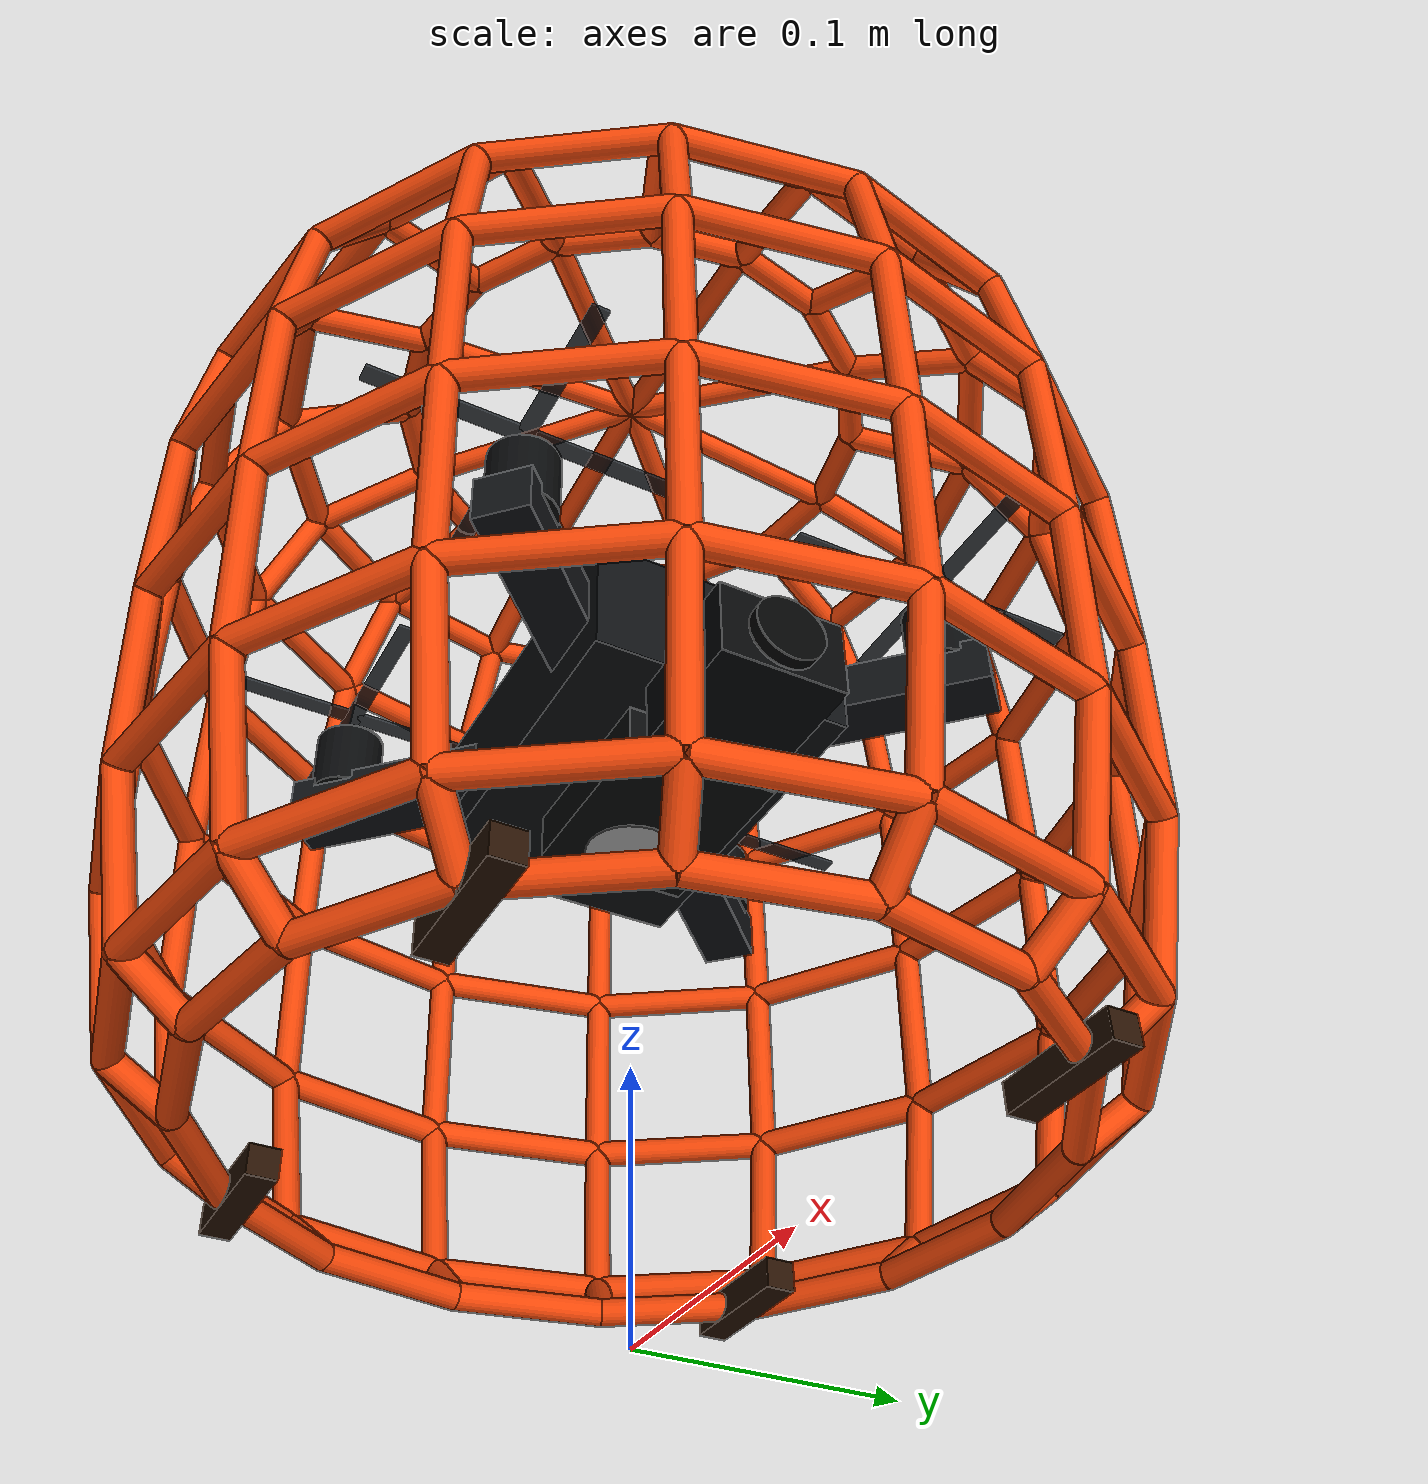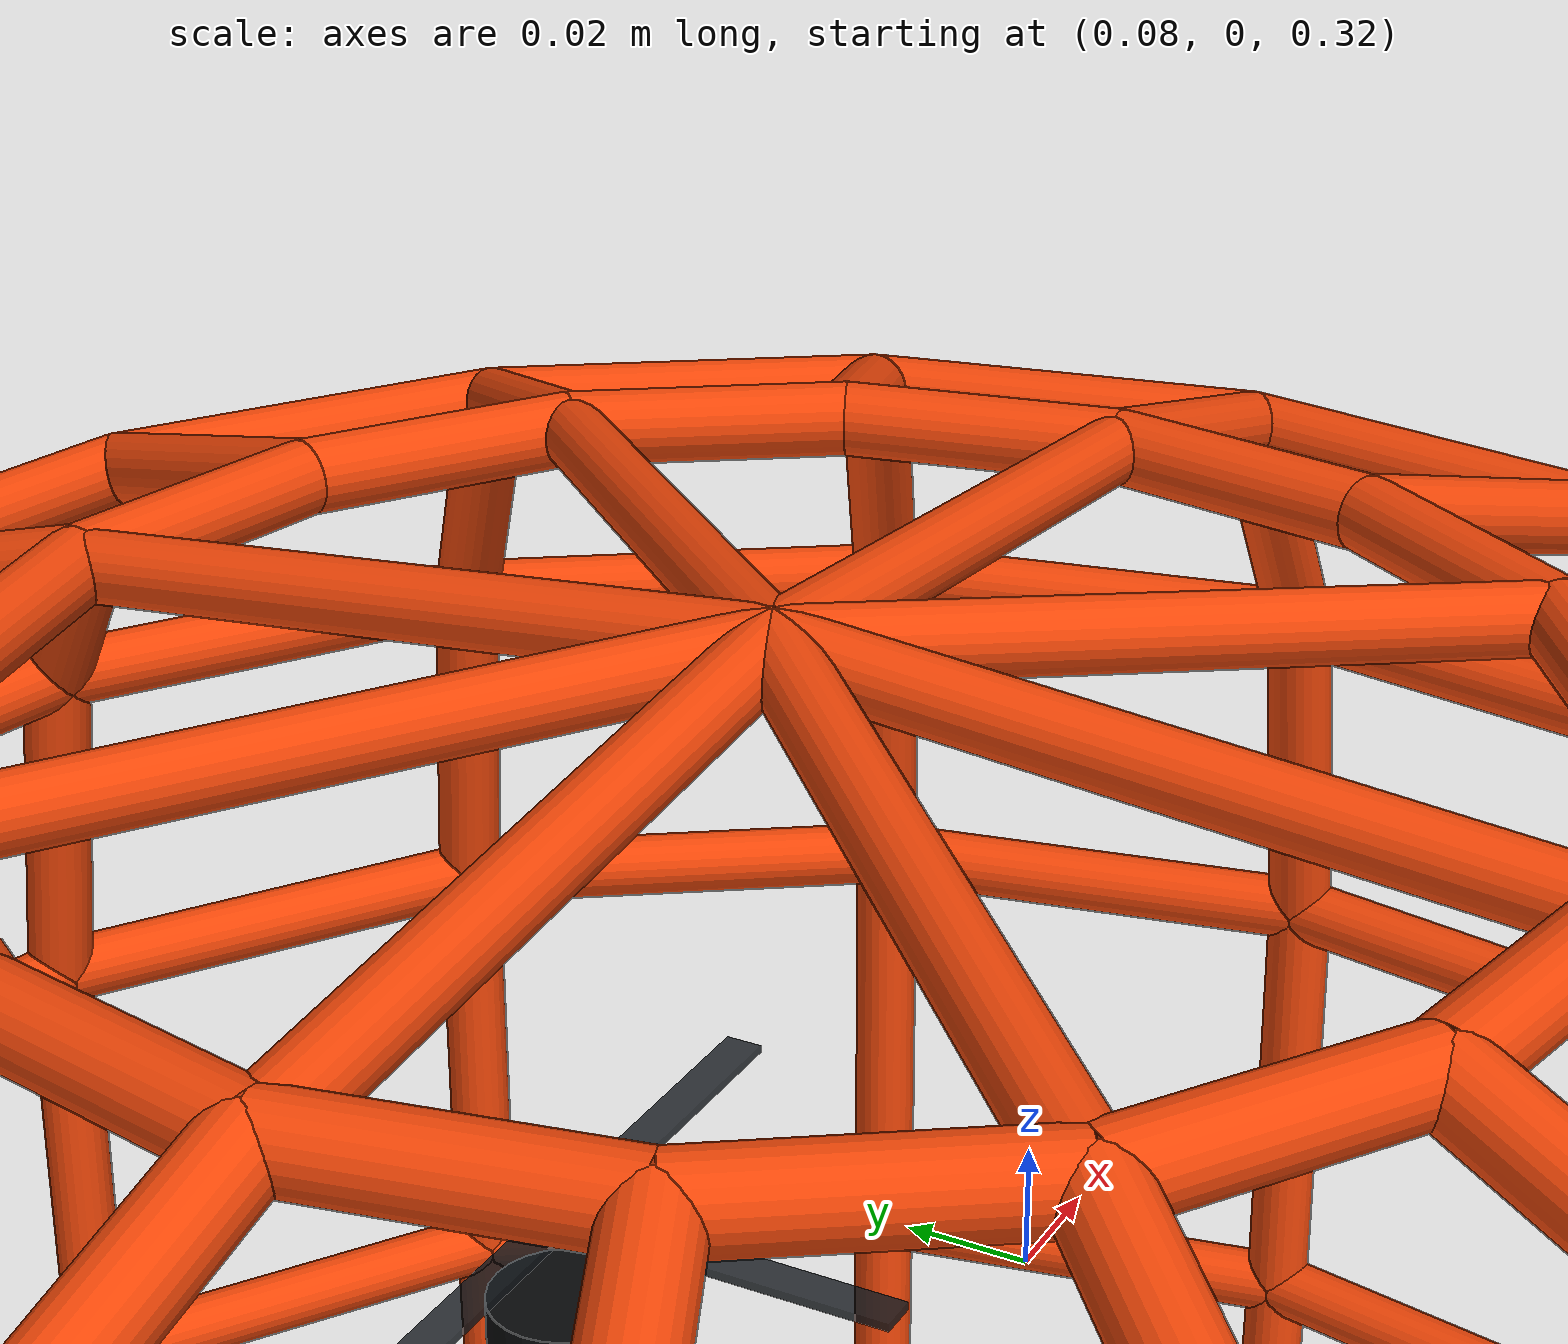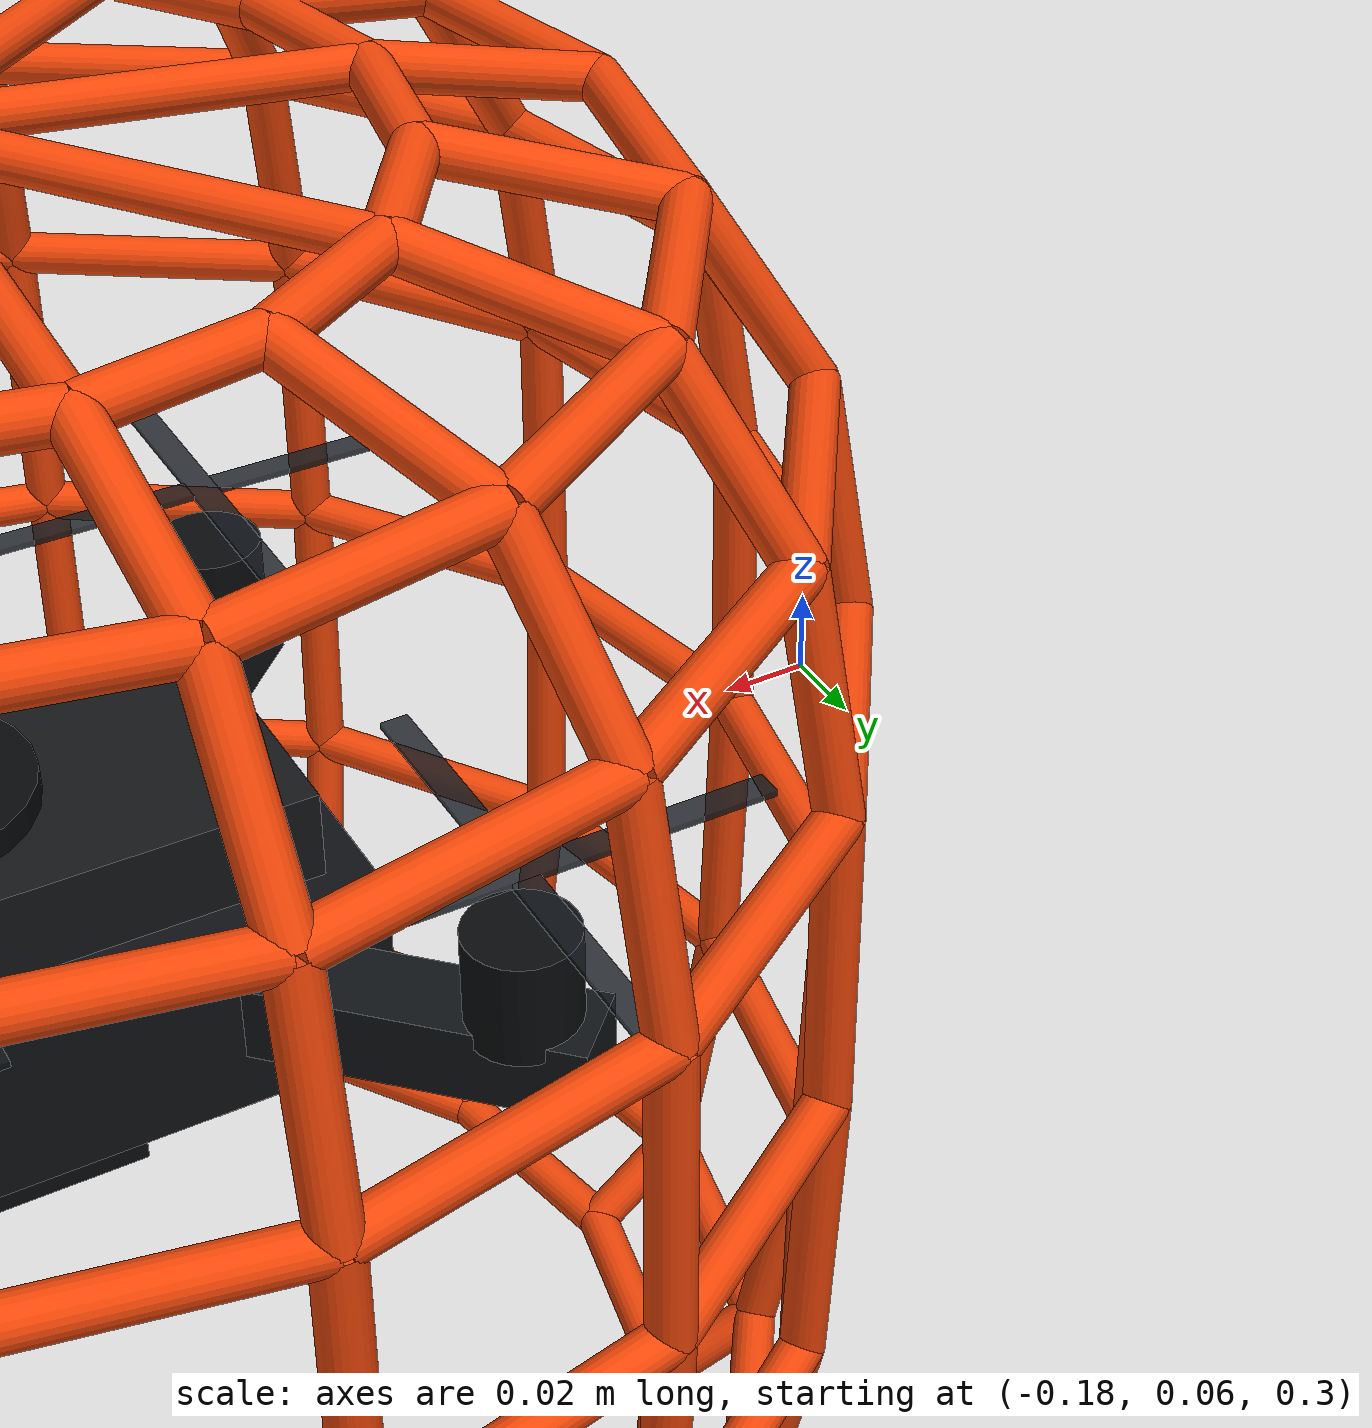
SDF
<?xml version="1.0" encoding="UTF-8"?>
<sdf version="1.9">
  <model name="elios_protected_drone_v3">
    <pose>0 0 0.24 0 0 0</pose>
    <self_collide>false</self_collide>
    <static>false</static>
    <!-- V3: realistic compact inspection drone body with original protective cage geometry.
         Flight-control interfaces and proven PX4 sensor rates are retained from V2. -->
    <link name="base_link">
      <inertial>
        <mass>0.9500</mass>
        <inertia>
          <ixx>0.00276292</ixx><ixy>0</ixy><ixz>0</ixz>
          <iyy>0.00276292</iyy><iyz>0</iyz><izz>0.00513000</izz>
        </inertia>
      </inertial>
      <gravity>true</gravity>
      <velocity_decay />

      <!-- Realistic compact inspection-drone fuselage: visual-only shaping, simple collision core. -->
      <visual name="main_fuselage">
        <pose>0 0 0.005 0 0 0</pose>
        <geometry><box><size>0.150 0.105 0.050</size></box></geometry>
        <material><ambient>0.030 0.035 0.042 1</ambient><diffuse>0.055 0.065 0.075 1</diffuse><specular>0.35 0.35 0.35 1</specular></material>
      </visual>
      <collision name="main_fuselage_collision">
        <pose>0 0 0.005 0 0 0</pose>
        <geometry><box><size>0.155 0.110 0.055</size></box></geometry>
      </collision>

      <visual name="top_battery_hump">
        <pose>-0.012 0 0.038 0 0 0</pose>
        <geometry><box><size>0.105 0.082 0.030</size></box></geometry>
        <material><ambient>0.040 0.045 0.055 1</ambient><diffuse>0.075 0.085 0.095 1</diffuse><specular>0.30 0.30 0.30 1</specular></material>
      </visual>
      <visual name="top_center_panel">
        <pose>0.018 0 0.055 0 0 0</pose>
        <geometry><cylinder><radius>0.030</radius><length>0.010</length></cylinder></geometry>
        <material><ambient>0.010 0.012 0.016 1</ambient><diffuse>0.025 0.030 0.035 1</diffuse><specular>0.45 0.45 0.45 1</specular></material>
      </visual>

      <!-- Streamlined X arms and motor fairings. -->
      <visual name="arm_front_right">
        <pose>0.064 -0.064 0.005 0 0 -0.785398</pose>
        <geometry><box><size>0.110 0.022 0.020</size></box></geometry>
        <material><ambient>0.035 0.040 0.048 1</ambient><diffuse>0.065 0.075 0.085 1</diffuse><specular>0.32 0.32 0.32 1</specular></material>
      </visual>
      <visual name="arm_front_left">
        <pose>0.064 0.064 0.005 0 0 0.785398</pose>
        <geometry><box><size>0.110 0.022 0.020</size></box></geometry>
        <material><ambient>0.035 0.040 0.048 1</ambient><diffuse>0.065 0.075 0.085 1</diffuse><specular>0.32 0.32 0.32 1</specular></material>
      </visual>
      <visual name="arm_rear_right">
        <pose>-0.064 -0.064 0.005 0 0 0.785398</pose>
        <geometry><box><size>0.110 0.022 0.020</size></box></geometry>
        <material><ambient>0.035 0.040 0.048 1</ambient><diffuse>0.065 0.075 0.085 1</diffuse><specular>0.32 0.32 0.32 1</specular></material>
      </visual>
      <visual name="arm_rear_left">
        <pose>-0.064 0.064 0.005 0 0 -0.785398</pose>
        <geometry><box><size>0.110 0.022 0.020</size></box></geometry>
        <material><ambient>0.035 0.040 0.048 1</ambient><diffuse>0.065 0.075 0.085 1</diffuse><specular>0.32 0.32 0.32 1</specular></material>
      </visual>
      <visual name="front_motor_fairing_r">
        <pose>0.090 -0.090 0.025 0 0 0</pose>
        <geometry><cylinder><radius>0.014</radius><length>0.028</length></cylinder></geometry>
        <material><ambient>0.018 0.020 0.024 1</ambient><diffuse>0.035 0.040 0.045 1</diffuse><specular>0.40 0.40 0.40 1</specular></material>
      </visual>
      <visual name="front_motor_fairing_l">
        <pose>0.090 0.090 0.025 0 0 0</pose>
        <geometry><cylinder><radius>0.014</radius><length>0.028</length></cylinder></geometry>
        <material><ambient>0.018 0.020 0.024 1</ambient><diffuse>0.035 0.040 0.045 1</diffuse><specular>0.40 0.40 0.40 1</specular></material>
      </visual>
      <visual name="rear_motor_fairing_r">
        <pose>-0.090 -0.090 0.025 0 0 0</pose>
        <geometry><cylinder><radius>0.014</radius><length>0.028</length></cylinder></geometry>
        <material><ambient>0.018 0.020 0.024 1</ambient><diffuse>0.035 0.040 0.045 1</diffuse><specular>0.40 0.40 0.40 1</specular></material>
      </visual>
      <visual name="rear_motor_fairing_l">
        <pose>-0.090 0.090 0.025 0 0 0</pose>
        <geometry><cylinder><radius>0.014</radius><length>0.028</length></cylinder></geometry>
        <material><ambient>0.018 0.020 0.024 1</ambient><diffuse>0.035 0.040 0.045 1</diffuse><specular>0.40 0.40 0.40 1</specular></material>
      </visual>

      <!-- Forward sensor/camera pod. -->
      <visual name="camera_pod">
        <pose>0.088 0 -0.030 0 0 0</pose>
        <geometry><box><size>0.055 0.050 0.032</size></box></geometry>
        <material><ambient>0.008 0.010 0.014 1</ambient><diffuse>0.020 0.025 0.030 1</diffuse><specular>0.55 0.55 0.55 1</specular></material>
      </visual>
      <visual name="camera_lens">
        <pose>0.118 0 -0.030 0 1.570796 0</pose>
        <geometry><cylinder><radius>0.014</radius><length>0.006</length></cylinder></geometry>
        <material><ambient>0.004 0.005 0.007 1</ambient><diffuse>0.010 0.012 0.014 1</diffuse><specular>0.65 0.65 0.65 1</specular></material>
      </visual>
      <visual name="bottom_sensor_bay">
        <pose>0.020 0 -0.038 0 0 0</pose>
        <geometry><box><size>0.075 0.060 0.018</size></box></geometry>
        <material><ambient>0.018 0.020 0.024 1</ambient><diffuse>0.035 0.040 0.045 1</diffuse><specular>0.40 0.40 0.40 1</specular></material>
      </visual>

      <!-- Protective cage: cylindrical middle, rounded top, slightly flattened lower section. -->
      <visual name="cage_ring_0_0_visual">
        <pose>0.149101 0.029658 -0.165000 0 1.570796 1.767146</pose>
        <geometry><cylinder><radius>0.0055</radius><length>0.060478</length></cylinder></geometry>
        <material><ambient>0.08 0.025 0.005 1</ambient><diffuse>0.95 0.28 0.035 1</diffuse><specular>0.45 0.20 0.08 1</specular></material>
      </visual>
      <collision name="cage_ring_0_0_collision">
        <pose>0.149101 0.029658 -0.165000 0 1.570796 1.767146</pose>
        <geometry><cylinder><radius>0.0055</radius><length>0.060478</length></cylinder></geometry>
        <surface><contact><ode><min_depth>0.001</min_depth><max_vel>0</max_vel></ode></contact></surface>
      </collision>
      <visual name="cage_ring_0_1_visual">
        <pose>0.126401 0.084459 -0.165000 0 1.570796 2.159845</pose>
        <geometry><cylinder><radius>0.0055</radius><length>0.060478</length></cylinder></geometry>
        <material><ambient>0.08 0.025 0.005 1</ambient><diffuse>0.95 0.28 0.035 1</diffuse><specular>0.45 0.20 0.08 1</specular></material>
      </visual>
      <collision name="cage_ring_0_1_collision">
        <pose>0.126401 0.084459 -0.165000 0 1.570796 2.159845</pose>
        <geometry><cylinder><radius>0.0055</radius><length>0.060478</length></cylinder></geometry>
        <surface><contact><ode><min_depth>0.001</min_depth><max_vel>0</max_vel></ode></contact></surface>
      </collision>
      <visual name="cage_ring_0_2_visual">
        <pose>0.084459 0.126401 -0.165000 0 1.570796 2.552544</pose>
        <geometry><cylinder><radius>0.0055</radius><length>0.060478</length></cylinder></geometry>
        <material><ambient>0.08 0.025 0.005 1</ambient><diffuse>0.95 0.28 0.035 1</diffuse><specular>0.45 0.20 0.08 1</specular></material>
      </visual>
      <collision name="cage_ring_0_2_collision">
        <pose>0.084459 0.126401 -0.165000 0 1.570796 2.552544</pose>
        <geometry><cylinder><radius>0.0055</radius><length>0.060478</length></cylinder></geometry>
        <surface><contact><ode><min_depth>0.001</min_depth><max_vel>0</max_vel></ode></contact></surface>
      </collision>
      <visual name="cage_ring_0_3_visual">
        <pose>0.029658 0.149101 -0.165000 0 1.570796 2.945243</pose>
        <geometry><cylinder><radius>0.0055</radius><length>0.060478</length></cylinder></geometry>
        <material><ambient>0.08 0.025 0.005 1</ambient><diffuse>0.95 0.28 0.035 1</diffuse><specular>0.45 0.20 0.08 1</specular></material>
      </visual>
      <collision name="cage_ring_0_3_collision">
        <pose>0.029658 0.149101 -0.165000 0 1.570796 2.945243</pose>
        <geometry><cylinder><radius>0.0055</radius><length>0.060478</length></cylinder></geometry>
        <surface><contact><ode><min_depth>0.001</min_depth><max_vel>0</max_vel></ode></contact></surface>
      </collision>
      <visual name="cage_ring_0_4_visual">
        <pose>-0.029658 0.149101 -0.165000 0 1.570796 -2.945243</pose>
        <geometry><cylinder><radius>0.0055</radius><length>0.060478</length></cylinder></geometry>
        <material><ambient>0.08 0.025 0.005 1</ambient><diffuse>0.95 0.28 0.035 1</diffuse><specular>0.45 0.20 0.08 1</specular></material>
      </visual>
      <collision name="cage_ring_0_4_collision">
        <pose>-0.029658 0.149101 -0.165000 0 1.570796 -2.945243</pose>
        <geometry><cylinder><radius>0.0055</radius><length>0.060478</length></cylinder></geometry>
        <surface><contact><ode><min_depth>0.001</min_depth><max_vel>0</max_vel></ode></contact></surface>
      </collision>
      <visual name="cage_ring_0_5_visual">
        <pose>-0.084459 0.126401 -0.165000 0 1.570796 -2.552544</pose>
        <geometry><cylinder><radius>0.0055</radius><length>0.060478</length></cylinder></geometry>
        <material><ambient>0.08 0.025 0.005 1</ambient><diffuse>0.95 0.28 0.035 1</diffuse><specular>0.45 0.20 0.08 1</specular></material>
      </visual>
      <collision name="cage_ring_0_5_collision">
        <pose>-0.084459 0.126401 -0.165000 0 1.570796 -2.552544</pose>
        <geometry><cylinder><radius>0.0055</radius><length>0.060478</length></cylinder></geometry>
        <surface><contact><ode><min_depth>0.001</min_depth><max_vel>0</max_vel></ode></contact></surface>
      </collision>
      <visual name="cage_ring_0_6_visual">
        <pose>-0.126401 0.084459 -0.165000 0 1.570796 -2.159845</pose>
        <geometry><cylinder><radius>0.0055</radius><length>0.060478</length></cylinder></geometry>
        <material><ambient>0.08 0.025 0.005 1</ambient><diffuse>0.95 0.28 0.035 1</diffuse><specular>0.45 0.20 0.08 1</specular></material>
      </visual>
      <collision name="cage_ring_0_6_collision">
        <pose>-0.126401 0.084459 -0.165000 0 1.570796 -2.159845</pose>
        <geometry><cylinder><radius>0.0055</radius><length>0.060478</length></cylinder></geometry>
        <surface><contact><ode><min_depth>0.001</min_depth><max_vel>0</max_vel></ode></contact></surface>
      </collision>
      <visual name="cage_ring_0_7_visual">
        <pose>-0.149101 0.029658 -0.165000 0 1.570796 -1.767146</pose>
        <geometry><cylinder><radius>0.0055</radius><length>0.060478</length></cylinder></geometry>
        <material><ambient>0.08 0.025 0.005 1</ambient><diffuse>0.95 0.28 0.035 1</diffuse><specular>0.45 0.20 0.08 1</specular></material>
      </visual>
      <collision name="cage_ring_0_7_collision">
        <pose>-0.149101 0.029658 -0.165000 0 1.570796 -1.767146</pose>
        <geometry><cylinder><radius>0.0055</radius><length>0.060478</length></cylinder></geometry>
        <surface><contact><ode><min_depth>0.001</min_depth><max_vel>0</max_vel></ode></contact></surface>
      </collision>
      <visual name="cage_ring_0_8_visual">
        <pose>-0.149101 -0.029658 -0.165000 0 1.570796 -1.374447</pose>
        <geometry><cylinder><radius>0.0055</radius><length>0.060478</length></cylinder></geometry>
        <material><ambient>0.08 0.025 0.005 1</ambient><diffuse>0.95 0.28 0.035 1</diffuse><specular>0.45 0.20 0.08 1</specular></material>
      </visual>
      <collision name="cage_ring_0_8_collision">
        <pose>-0.149101 -0.029658 -0.165000 0 1.570796 -1.374447</pose>
        <geometry><cylinder><radius>0.0055</radius><length>0.060478</length></cylinder></geometry>
        <surface><contact><ode><min_depth>0.001</min_depth><max_vel>0</max_vel></ode></contact></surface>
      </collision>
      <visual name="cage_ring_0_9_visual">
        <pose>-0.126401 -0.084459 -0.165000 0 1.570796 -0.981748</pose>
        <geometry><cylinder><radius>0.0055</radius><length>0.060478</length></cylinder></geometry>
        <material><ambient>0.08 0.025 0.005 1</ambient><diffuse>0.95 0.28 0.035 1</diffuse><specular>0.45 0.20 0.08 1</specular></material>
      </visual>
      <collision name="cage_ring_0_9_collision">
        <pose>-0.126401 -0.084459 -0.165000 0 1.570796 -0.981748</pose>
        <geometry><cylinder><radius>0.0055</radius><length>0.060478</length></cylinder></geometry>
        <surface><contact><ode><min_depth>0.001</min_depth><max_vel>0</max_vel></ode></contact></surface>
      </collision>
      <visual name="cage_ring_0_10_visual">
        <pose>-0.084459 -0.126401 -0.165000 0 1.570796 -0.589049</pose>
        <geometry><cylinder><radius>0.0055</radius><length>0.060478</length></cylinder></geometry>
        <material><ambient>0.08 0.025 0.005 1</ambient><diffuse>0.95 0.28 0.035 1</diffuse><specular>0.45 0.20 0.08 1</specular></material>
      </visual>
      <collision name="cage_ring_0_10_collision">
        <pose>-0.084459 -0.126401 -0.165000 0 1.570796 -0.589049</pose>
        <geometry><cylinder><radius>0.0055</radius><length>0.060478</length></cylinder></geometry>
        <surface><contact><ode><min_depth>0.001</min_depth><max_vel>0</max_vel></ode></contact></surface>
      </collision>
      <visual name="cage_ring_0_11_visual">
        <pose>-0.029658 -0.149101 -0.165000 0 1.570796 -0.196350</pose>
        <geometry><cylinder><radius>0.0055</radius><length>0.060478</length></cylinder></geometry>
        <material><ambient>0.08 0.025 0.005 1</ambient><diffuse>0.95 0.28 0.035 1</diffuse><specular>0.45 0.20 0.08 1</specular></material>
      </visual>
      <collision name="cage_ring_0_11_collision">
        <pose>-0.029658 -0.149101 -0.165000 0 1.570796 -0.196350</pose>
        <geometry><cylinder><radius>0.0055</radius><length>0.060478</length></cylinder></geometry>
        <surface><contact><ode><min_depth>0.001</min_depth><max_vel>0</max_vel></ode></contact></surface>
      </collision>
      <visual name="cage_ring_0_12_visual">
        <pose>0.029658 -0.149101 -0.165000 0 1.570796 0.196350</pose>
        <geometry><cylinder><radius>0.0055</radius><length>0.060478</length></cylinder></geometry>
        <material><ambient>0.08 0.025 0.005 1</ambient><diffuse>0.95 0.28 0.035 1</diffuse><specular>0.45 0.20 0.08 1</specular></material>
      </visual>
      <collision name="cage_ring_0_12_collision">
        <pose>0.029658 -0.149101 -0.165000 0 1.570796 0.196350</pose>
        <geometry><cylinder><radius>0.0055</radius><length>0.060478</length></cylinder></geometry>
        <surface><contact><ode><min_depth>0.001</min_depth><max_vel>0</max_vel></ode></contact></surface>
      </collision>
      <visual name="cage_ring_0_13_visual">
        <pose>0.084459 -0.126401 -0.165000 0 1.570796 0.589049</pose>
        <geometry><cylinder><radius>0.0055</radius><length>0.060478</length></cylinder></geometry>
        <material><ambient>0.08 0.025 0.005 1</ambient><diffuse>0.95 0.28 0.035 1</diffuse><specular>0.45 0.20 0.08 1</specular></material>
      </visual>
      <collision name="cage_ring_0_13_collision">
        <pose>0.084459 -0.126401 -0.165000 0 1.570796 0.589049</pose>
        <geometry><cylinder><radius>0.0055</radius><length>0.060478</length></cylinder></geometry>
        <surface><contact><ode><min_depth>0.001</min_depth><max_vel>0</max_vel></ode></contact></surface>
      </collision>
      <visual name="cage_ring_0_14_visual">
        <pose>0.126401 -0.084459 -0.165000 0 1.570796 0.981748</pose>
        <geometry><cylinder><radius>0.0055</radius><length>0.060478</length></cylinder></geometry>
        <material><ambient>0.08 0.025 0.005 1</ambient><diffuse>0.95 0.28 0.035 1</diffuse><specular>0.45 0.20 0.08 1</specular></material>
      </visual>
      <collision name="cage_ring_0_14_collision">
        <pose>0.126401 -0.084459 -0.165000 0 1.570796 0.981748</pose>
        <geometry><cylinder><radius>0.0055</radius><length>0.060478</length></cylinder></geometry>
        <surface><contact><ode><min_depth>0.001</min_depth><max_vel>0</max_vel></ode></contact></surface>
      </collision>
      <visual name="cage_ring_0_15_visual">
        <pose>0.149101 -0.029658 -0.165000 0 1.570796 1.374447</pose>
        <geometry><cylinder><radius>0.0055</radius><length>0.060478</length></cylinder></geometry>
        <material><ambient>0.08 0.025 0.005 1</ambient><diffuse>0.95 0.28 0.035 1</diffuse><specular>0.45 0.20 0.08 1</specular></material>
      </visual>
      <collision name="cage_ring_0_15_collision">
        <pose>0.149101 -0.029658 -0.165000 0 1.570796 1.374447</pose>
        <geometry><cylinder><radius>0.0055</radius><length>0.060478</length></cylinder></geometry>
        <surface><contact><ode><min_depth>0.001</min_depth><max_vel>0</max_vel></ode></contact></surface>
      </collision>
      <visual name="cage_ring_1_0_visual">
        <pose>0.173149 0.034442 -0.145000 0 1.570796 1.767146</pose>
        <geometry><cylinder><radius>0.0055</radius><length>0.070233</length></cylinder></geometry>
        <material><ambient>0.08 0.025 0.005 1</ambient><diffuse>0.95 0.28 0.035 1</diffuse><specular>0.45 0.20 0.08 1</specular></material>
      </visual>
      <collision name="cage_ring_1_0_collision">
        <pose>0.173149 0.034442 -0.145000 0 1.570796 1.767146</pose>
        <geometry><cylinder><radius>0.0055</radius><length>0.070233</length></cylinder></geometry>
        <surface><contact><ode><min_depth>0.001</min_depth><max_vel>0</max_vel></ode></contact></surface>
      </collision>
      <visual name="cage_ring_1_1_visual">
        <pose>0.146789 0.098081 -0.145000 0 1.570796 2.159845</pose>
        <geometry><cylinder><radius>0.0055</radius><length>0.070233</length></cylinder></geometry>
        <material><ambient>0.08 0.025 0.005 1</ambient><diffuse>0.95 0.28 0.035 1</diffuse><specular>0.45 0.20 0.08 1</specular></material>
      </visual>
      <collision name="cage_ring_1_1_collision">
        <pose>0.146789 0.098081 -0.145000 0 1.570796 2.159845</pose>
        <geometry><cylinder><radius>0.0055</radius><length>0.070233</length></cylinder></geometry>
        <surface><contact><ode><min_depth>0.001</min_depth><max_vel>0</max_vel></ode></contact></surface>
      </collision>
      <visual name="cage_ring_1_2_visual">
        <pose>0.098081 0.146789 -0.145000 0 1.570796 2.552544</pose>
        <geometry><cylinder><radius>0.0055</radius><length>0.070233</length></cylinder></geometry>
        <material><ambient>0.08 0.025 0.005 1</ambient><diffuse>0.95 0.28 0.035 1</diffuse><specular>0.45 0.20 0.08 1</specular></material>
      </visual>
      <collision name="cage_ring_1_2_collision">
        <pose>0.098081 0.146789 -0.145000 0 1.570796 2.552544</pose>
        <geometry><cylinder><radius>0.0055</radius><length>0.070233</length></cylinder></geometry>
        <surface><contact><ode><min_depth>0.001</min_depth><max_vel>0</max_vel></ode></contact></surface>
      </collision>
      <visual name="cage_ring_1_3_visual">
        <pose>0.034442 0.173149 -0.145000 0 1.570796 2.945243</pose>
        <geometry><cylinder><radius>0.0055</radius><length>0.070233</length></cylinder></geometry>
        <material><ambient>0.08 0.025 0.005 1</ambient><diffuse>0.95 0.28 0.035 1</diffuse><specular>0.45 0.20 0.08 1</specular></material>
      </visual>
      <collision name="cage_ring_1_3_collision">
        <pose>0.034442 0.173149 -0.145000 0 1.570796 2.945243</pose>
        <geometry><cylinder><radius>0.0055</radius><length>0.070233</length></cylinder></geometry>
        <surface><contact><ode><min_depth>0.001</min_depth><max_vel>0</max_vel></ode></contact></surface>
      </collision>
      <visual name="cage_ring_1_4_visual">
        <pose>-0.034442 0.173149 -0.145000 0 1.570796 -2.945243</pose>
        <geometry><cylinder><radius>0.0055</radius><length>0.070233</length></cylinder></geometry>
        <material><ambient>0.08 0.025 0.005 1</ambient><diffuse>0.95 0.28 0.035 1</diffuse><specular>0.45 0.20 0.08 1</specular></material>
      </visual>
      <collision name="cage_ring_1_4_collision">
        <pose>-0.034442 0.173149 -0.145000 0 1.570796 -2.945243</pose>
        <geometry><cylinder><radius>0.0055</radius><length>0.070233</length></cylinder></geometry>
        <surface><contact><ode><min_depth>0.001</min_depth><max_vel>0</max_vel></ode></contact></surface>
      </collision>
      <visual name="cage_ring_1_5_visual">
        <pose>-0.098081 0.146789 -0.145000 0 1.570796 -2.552544</pose>
        <geometry><cylinder><radius>0.0055</radius><length>0.070233</length></cylinder></geometry>
        <material><ambient>0.08 0.025 0.005 1</ambient><diffuse>0.95 0.28 0.035 1</diffuse><specular>0.45 0.20 0.08 1</specular></material>
      </visual>
      <collision name="cage_ring_1_5_collision">
        <pose>-0.098081 0.146789 -0.145000 0 1.570796 -2.552544</pose>
        <geometry><cylinder><radius>0.0055</radius><length>0.070233</length></cylinder></geometry>
        <surface><contact><ode><min_depth>0.001</min_depth><max_vel>0</max_vel></ode></contact></surface>
      </collision>
      <visual name="cage_ring_1_6_visual">
        <pose>-0.146789 0.098081 -0.145000 0 1.570796 -2.159845</pose>
        <geometry><cylinder><radius>0.0055</radius><length>0.070233</length></cylinder></geometry>
        <material><ambient>0.08 0.025 0.005 1</ambient><diffuse>0.95 0.28 0.035 1</diffuse><specular>0.45 0.20 0.08 1</specular></material>
      </visual>
      <collision name="cage_ring_1_6_collision">
        <pose>-0.146789 0.098081 -0.145000 0 1.570796 -2.159845</pose>
        <geometry><cylinder><radius>0.0055</radius><length>0.070233</length></cylinder></geometry>
        <surface><contact><ode><min_depth>0.001</min_depth><max_vel>0</max_vel></ode></contact></surface>
      </collision>
      <visual name="cage_ring_1_7_visual">
        <pose>-0.173149 0.034442 -0.145000 0 1.570796 -1.767146</pose>
        <geometry><cylinder><radius>0.0055</radius><length>0.070233</length></cylinder></geometry>
        <material><ambient>0.08 0.025 0.005 1</ambient><diffuse>0.95 0.28 0.035 1</diffuse><specular>0.45 0.20 0.08 1</specular></material>
      </visual>
      <collision name="cage_ring_1_7_collision">
        <pose>-0.173149 0.034442 -0.145000 0 1.570796 -1.767146</pose>
        <geometry><cylinder><radius>0.0055</radius><length>0.070233</length></cylinder></geometry>
        <surface><contact><ode><min_depth>0.001</min_depth><max_vel>0</max_vel></ode></contact></surface>
      </collision>
      <visual name="cage_ring_1_8_visual">
        <pose>-0.173149 -0.034442 -0.145000 0 1.570796 -1.374447</pose>
        <geometry><cylinder><radius>0.0055</radius><length>0.070233</length></cylinder></geometry>
        <material><ambient>0.08 0.025 0.005 1</ambient><diffuse>0.95 0.28 0.035 1</diffuse><specular>0.45 0.20 0.08 1</specular></material>
      </visual>
      <collision name="cage_ring_1_8_collision">
        <pose>-0.173149 -0.034442 -0.145000 0 1.570796 -1.374447</pose>
        <geometry><cylinder><radius>0.0055</radius><length>0.070233</length></cylinder></geometry>
        <surface><contact><ode><min_depth>0.001</min_depth><max_vel>0</max_vel></ode></contact></surface>
      </collision>
      <visual name="cage_ring_1_9_visual">
        <pose>-0.146789 -0.098081 -0.145000 0 1.570796 -0.981748</pose>
        <geometry><cylinder><radius>0.0055</radius><length>0.070233</length></cylinder></geometry>
        <material><ambient>0.08 0.025 0.005 1</ambient><diffuse>0.95 0.28 0.035 1</diffuse><specular>0.45 0.20 0.08 1</specular></material>
      </visual>
      <collision name="cage_ring_1_9_collision">
        <pose>-0.146789 -0.098081 -0.145000 0 1.570796 -0.981748</pose>
        <geometry><cylinder><radius>0.0055</radius><length>0.070233</length></cylinder></geometry>
        <surface><contact><ode><min_depth>0.001</min_depth><max_vel>0</max_vel></ode></contact></surface>
      </collision>
      <visual name="cage_ring_1_10_visual">
        <pose>-0.098081 -0.146789 -0.145000 0 1.570796 -0.589049</pose>
        <geometry><cylinder><radius>0.0055</radius><length>0.070233</length></cylinder></geometry>
        <material><ambient>0.08 0.025 0.005 1</ambient><diffuse>0.95 0.28 0.035 1</diffuse><specular>0.45 0.20 0.08 1</specular></material>
      </visual>
      <collision name="cage_ring_1_10_collision">
        <pose>-0.098081 -0.146789 -0.145000 0 1.570796 -0.589049</pose>
        <geometry><cylinder><radius>0.0055</radius><length>0.070233</length></cylinder></geometry>
        <surface><contact><ode><min_depth>0.001</min_depth><max_vel>0</max_vel></ode></contact></surface>
      </collision>
      <visual name="cage_ring_1_11_visual">
        <pose>-0.034442 -0.173149 -0.145000 0 1.570796 -0.196350</pose>
        <geometry><cylinder><radius>0.0055</radius><length>0.070233</length></cylinder></geometry>
        <material><ambient>0.08 0.025 0.005 1</ambient><diffuse>0.95 0.28 0.035 1</diffuse><specular>0.45 0.20 0.08 1</specular></material>
      </visual>
      <collision name="cage_ring_1_11_collision">
        <pose>-0.034442 -0.173149 -0.145000 0 1.570796 -0.196350</pose>
        <geometry><cylinder><radius>0.0055</radius><length>0.070233</length></cylinder></geometry>
        <surface><contact><ode><min_depth>0.001</min_depth><max_vel>0</max_vel></ode></contact></surface>
      </collision>
      <visual name="cage_ring_1_12_visual">
        <pose>0.034442 -0.173149 -0.145000 0 1.570796 0.196350</pose>
        <geometry><cylinder><radius>0.0055</radius><length>0.070233</length></cylinder></geometry>
        <material><ambient>0.08 0.025 0.005 1</ambient><diffuse>0.95 0.28 0.035 1</diffuse><specular>0.45 0.20 0.08 1</specular></material>
      </visual>
      <collision name="cage_ring_1_12_collision">
        <pose>0.034442 -0.173149 -0.145000 0 1.570796 0.196350</pose>
        <geometry><cylinder><radius>0.0055</radius><length>0.070233</length></cylinder></geometry>
        <surface><contact><ode><min_depth>0.001</min_depth><max_vel>0</max_vel></ode></contact></surface>
      </collision>
      <visual name="cage_ring_1_13_visual">
        <pose>0.098081 -0.146789 -0.145000 0 1.570796 0.589049</pose>
        <geometry><cylinder><radius>0.0055</radius><length>0.070233</length></cylinder></geometry>
        <material><ambient>0.08 0.025 0.005 1</ambient><diffuse>0.95 0.28 0.035 1</diffuse><specular>0.45 0.20 0.08 1</specular></material>
      </visual>
      <collision name="cage_ring_1_13_collision">
        <pose>0.098081 -0.146789 -0.145000 0 1.570796 0.589049</pose>
        <geometry><cylinder><radius>0.0055</radius><length>0.070233</length></cylinder></geometry>
        <surface><contact><ode><min_depth>0.001</min_depth><max_vel>0</max_vel></ode></contact></surface>
      </collision>
      <visual name="cage_ring_1_14_visual">
        <pose>0.146789 -0.098081 -0.145000 0 1.570796 0.981748</pose>
        <geometry><cylinder><radius>0.0055</radius><length>0.070233</length></cylinder></geometry>
        <material><ambient>0.08 0.025 0.005 1</ambient><diffuse>0.95 0.28 0.035 1</diffuse><specular>0.45 0.20 0.08 1</specular></material>
      </visual>
      <collision name="cage_ring_1_14_collision">
        <pose>0.146789 -0.098081 -0.145000 0 1.570796 0.981748</pose>
        <geometry><cylinder><radius>0.0055</radius><length>0.070233</length></cylinder></geometry>
        <surface><contact><ode><min_depth>0.001</min_depth><max_vel>0</max_vel></ode></contact></surface>
      </collision>
      <visual name="cage_ring_1_15_visual">
        <pose>0.173149 -0.034442 -0.145000 0 1.570796 1.374447</pose>
        <geometry><cylinder><radius>0.0055</radius><length>0.070233</length></cylinder></geometry>
        <material><ambient>0.08 0.025 0.005 1</ambient><diffuse>0.95 0.28 0.035 1</diffuse><specular>0.45 0.20 0.08 1</specular></material>
      </visual>
      <collision name="cage_ring_1_15_collision">
        <pose>0.173149 -0.034442 -0.145000 0 1.570796 1.374447</pose>
        <geometry><cylinder><radius>0.0055</radius><length>0.070233</length></cylinder></geometry>
        <surface><contact><ode><min_depth>0.001</min_depth><max_vel>0</max_vel></ode></contact></surface>
      </collision>
      <visual name="cage_ring_2_0_visual">
        <pose>0.186616 0.037120 -0.075000 0 1.570796 1.767146</pose>
        <geometry><cylinder><radius>0.0055</radius><length>0.075695</length></cylinder></geometry>
        <material><ambient>0.08 0.025 0.005 1</ambient><diffuse>0.95 0.28 0.035 1</diffuse><specular>0.45 0.20 0.08 1</specular></material>
      </visual>
      <collision name="cage_ring_2_0_collision">
        <pose>0.186616 0.037120 -0.075000 0 1.570796 1.767146</pose>
        <geometry><cylinder><radius>0.0055</radius><length>0.075695</length></cylinder></geometry>
        <surface><contact><ode><min_depth>0.001</min_depth><max_vel>0</max_vel></ode></contact></surface>
      </collision>
      <visual name="cage_ring_2_1_visual">
        <pose>0.158206 0.105710 -0.075000 0 1.570796 2.159845</pose>
        <geometry><cylinder><radius>0.0055</radius><length>0.075695</length></cylinder></geometry>
        <material><ambient>0.08 0.025 0.005 1</ambient><diffuse>0.95 0.28 0.035 1</diffuse><specular>0.45 0.20 0.08 1</specular></material>
      </visual>
      <collision name="cage_ring_2_1_collision">
        <pose>0.158206 0.105710 -0.075000 0 1.570796 2.159845</pose>
        <geometry><cylinder><radius>0.0055</radius><length>0.075695</length></cylinder></geometry>
        <surface><contact><ode><min_depth>0.001</min_depth><max_vel>0</max_vel></ode></contact></surface>
      </collision>
      <visual name="cage_ring_2_2_visual">
        <pose>0.105710 0.158206 -0.075000 0 1.570796 2.552544</pose>
        <geometry><cylinder><radius>0.0055</radius><length>0.075695</length></cylinder></geometry>
        <material><ambient>0.08 0.025 0.005 1</ambient><diffuse>0.95 0.28 0.035 1</diffuse><specular>0.45 0.20 0.08 1</specular></material>
      </visual>
      <collision name="cage_ring_2_2_collision">
        <pose>0.105710 0.158206 -0.075000 0 1.570796 2.552544</pose>
        <geometry><cylinder><radius>0.0055</radius><length>0.075695</length></cylinder></geometry>
        <surface><contact><ode><min_depth>0.001</min_depth><max_vel>0</max_vel></ode></contact></surface>
      </collision>
      <visual name="cage_ring_2_3_visual">
        <pose>0.037120 0.186616 -0.075000 0 1.570796 2.945243</pose>
        <geometry><cylinder><radius>0.0055</radius><length>0.075695</length></cylinder></geometry>
        <material><ambient>0.08 0.025 0.005 1</ambient><diffuse>0.95 0.28 0.035 1</diffuse><specular>0.45 0.20 0.08 1</specular></material>
      </visual>
      <collision name="cage_ring_2_3_collision">
        <pose>0.037120 0.186616 -0.075000 0 1.570796 2.945243</pose>
        <geometry><cylinder><radius>0.0055</radius><length>0.075695</length></cylinder></geometry>
        <surface><contact><ode><min_depth>0.001</min_depth><max_vel>0</max_vel></ode></contact></surface>
      </collision>
      <visual name="cage_ring_2_4_visual">
        <pose>-0.037120 0.186616 -0.075000 0 1.570796 -2.945243</pose>
        <geometry><cylinder><radius>0.0055</radius><length>0.075695</length></cylinder></geometry>
        <material><ambient>0.08 0.025 0.005 1</ambient><diffuse>0.95 0.28 0.035 1</diffuse><specular>0.45 0.20 0.08 1</specular></material>
      </visual>
      <collision name="cage_ring_2_4_collision">
        <pose>-0.037120 0.186616 -0.075000 0 1.570796 -2.945243</pose>
        <geometry><cylinder><radius>0.0055</radius><length>0.075695</length></cylinder></geometry>
        <surface><contact><ode><min_depth>0.001</min_depth><max_vel>0</max_vel></ode></contact></surface>
      </collision>
      <visual name="cage_ring_2_5_visual">
        <pose>-0.105710 0.158206 -0.075000 0 1.570796 -2.552544</pose>
        <geometry><cylinder><radius>0.0055</radius><length>0.075695</length></cylinder></geometry>
        <material><ambient>0.08 0.025 0.005 1</ambient><diffuse>0.95 0.28 0.035 1</diffuse><specular>0.45 0.20 0.08 1</specular></material>
      </visual>
      <collision name="cage_ring_2_5_collision">
        <pose>-0.105710 0.158206 -0.075000 0 1.570796 -2.552544</pose>
        <geometry><cylinder><radius>0.0055</radius><length>0.075695</length></cylinder></geometry>
        <surface><contact><ode><min_depth>0.001</min_depth><max_vel>0</max_vel></ode></contact></surface>
      </collision>
      <visual name="cage_ring_2_6_visual">
        <pose>-0.158206 0.105710 -0.075000 0 1.570796 -2.159845</pose>
        <geometry><cylinder><radius>0.0055</radius><length>0.075695</length></cylinder></geometry>
        <material><ambient>0.08 0.025 0.005 1</ambient><diffuse>0.95 0.28 0.035 1</diffuse><specular>0.45 0.20 0.08 1</specular></material>
      </visual>
      <collision name="cage_ring_2_6_collision">
        <pose>-0.158206 0.105710 -0.075000 0 1.570796 -2.159845</pose>
        <geometry><cylinder><radius>0.0055</radius><length>0.075695</length></cylinder></geometry>
        <surface><contact><ode><min_depth>0.001</min_depth><max_vel>0</max_vel></ode></contact></surface>
      </collision>
      <visual name="cage_ring_2_7_visual">
        <pose>-0.186616 0.037120 -0.075000 0 1.570796 -1.767146</pose>
        <geometry><cylinder><radius>0.0055</radius><length>0.075695</length></cylinder></geometry>
        <material><ambient>0.08 0.025 0.005 1</ambient><diffuse>0.95 0.28 0.035 1</diffuse><specular>0.45 0.20 0.08 1</specular></material>
      </visual>
      <collision name="cage_ring_2_7_collision">
        <pose>-0.186616 0.037120 -0.075000 0 1.570796 -1.767146</pose>
        <geometry><cylinder><radius>0.0055</radius><length>0.075695</length></cylinder></geometry>
        <surface><contact><ode><min_depth>0.001</min_depth><max_vel>0</max_vel></ode></contact></surface>
      </collision>
      <visual name="cage_ring_2_8_visual">
        <pose>-0.186616 -0.037120 -0.075000 0 1.570796 -1.374447</pose>
        <geometry><cylinder><radius>0.0055</radius><length>0.075695</length></cylinder></geometry>
        <material><ambient>0.08 0.025 0.005 1</ambient><diffuse>0.95 0.28 0.035 1</diffuse><specular>0.45 0.20 0.08 1</specular></material>
      </visual>
      <collision name="cage_ring_2_8_collision">
        <pose>-0.186616 -0.037120 -0.075000 0 1.570796 -1.374447</pose>
        <geometry><cylinder><radius>0.0055</radius><length>0.075695</length></cylinder></geometry>
        <surface><contact><ode><min_depth>0.001</min_depth><max_vel>0</max_vel></ode></contact></surface>
      </collision>
      <visual name="cage_ring_2_9_visual">
        <pose>-0.158206 -0.105710 -0.075000 0 1.570796 -0.981748</pose>
        <geometry><cylinder><radius>0.0055</radius><length>0.075695</length></cylinder></geometry>
        <material><ambient>0.08 0.025 0.005 1</ambient><diffuse>0.95 0.28 0.035 1</diffuse><specular>0.45 0.20 0.08 1</specular></material>
      </visual>
      <collision name="cage_ring_2_9_collision">
        <pose>-0.158206 -0.105710 -0.075000 0 1.570796 -0.981748</pose>
        <geometry><cylinder><radius>0.0055</radius><length>0.075695</length></cylinder></geometry>
        <surface><contact><ode><min_depth>0.001</min_depth><max_vel>0</max_vel></ode></contact></surface>
      </collision>
      <visual name="cage_ring_2_10_visual">
        <pose>-0.105710 -0.158206 -0.075000 0 1.570796 -0.589049</pose>
        <geometry><cylinder><radius>0.0055</radius><length>0.075695</length></cylinder></geometry>
        <material><ambient>0.08 0.025 0.005 1</ambient><diffuse>0.95 0.28 0.035 1</diffuse><specular>0.45 0.20 0.08 1</specular></material>
      </visual>
      <collision name="cage_ring_2_10_collision">
        <pose>-0.105710 -0.158206 -0.075000 0 1.570796 -0.589049</pose>
        <geometry><cylinder><radius>0.0055</radius><length>0.075695</length></cylinder></geometry>
        <surface><contact><ode><min_depth>0.001</min_depth><max_vel>0</max_vel></ode></contact></surface>
      </collision>
      <visual name="cage_ring_2_11_visual">
        <pose>-0.037120 -0.186616 -0.075000 0 1.570796 -0.196350</pose>
        <geometry><cylinder><radius>0.0055</radius><length>0.075695</length></cylinder></geometry>
        <material><ambient>0.08 0.025 0.005 1</ambient><diffuse>0.95 0.28 0.035 1</diffuse><specular>0.45 0.20 0.08 1</specular></material>
      </visual>
      <collision name="cage_ring_2_11_collision">
        <pose>-0.037120 -0.186616 -0.075000 0 1.570796 -0.196350</pose>
        <geometry><cylinder><radius>0.0055</radius><length>0.075695</length></cylinder></geometry>
        <surface><contact><ode><min_depth>0.001</min_depth><max_vel>0</max_vel></ode></contact></surface>
      </collision>
      <visual name="cage_ring_2_12_visual">
        <pose>0.037120 -0.186616 -0.075000 0 1.570796 0.196350</pose>
        <geometry><cylinder><radius>0.0055</radius><length>0.075695</length></cylinder></geometry>
        <material><ambient>0.08 0.025 0.005 1</ambient><diffuse>0.95 0.28 0.035 1</diffuse><specular>0.45 0.20 0.08 1</specular></material>
      </visual>
      <collision name="cage_ring_2_12_collision">
        <pose>0.037120 -0.186616 -0.075000 0 1.570796 0.196350</pose>
        <geometry><cylinder><radius>0.0055</radius><length>0.075695</length></cylinder></geometry>
        <surface><contact><ode><min_depth>0.001</min_depth><max_vel>0</max_vel></ode></contact></surface>
      </collision>
      <visual name="cage_ring_2_13_visual">
        <pose>0.105710 -0.158206 -0.075000 0 1.570796 0.589049</pose>
        <geometry><cylinder><radius>0.0055</radius><length>0.075695</length></cylinder></geometry>
        <material><ambient>0.08 0.025 0.005 1</ambient><diffuse>0.95 0.28 0.035 1</diffuse><specular>0.45 0.20 0.08 1</specular></material>
      </visual>
      <collision name="cage_ring_2_13_collision">
        <pose>0.105710 -0.158206 -0.075000 0 1.570796 0.589049</pose>
        <geometry><cylinder><radius>0.0055</radius><length>0.075695</length></cylinder></geometry>
        <surface><contact><ode><min_depth>0.001</min_depth><max_vel>0</max_vel></ode></contact></surface>
      </collision>
      <visual name="cage_ring_2_14_visual">
        <pose>0.158206 -0.105710 -0.075000 0 1.570796 0.981748</pose>
        <geometry><cylinder><radius>0.0055</radius><length>0.075695</length></cylinder></geometry>
        <material><ambient>0.08 0.025 0.005 1</ambient><diffuse>0.95 0.28 0.035 1</diffuse><specular>0.45 0.20 0.08 1</specular></material>
      </visual>
      <collision name="cage_ring_2_14_collision">
        <pose>0.158206 -0.105710 -0.075000 0 1.570796 0.981748</pose>
        <geometry><cylinder><radius>0.0055</radius><length>0.075695</length></cylinder></geometry>
        <surface><contact><ode><min_depth>0.001</min_depth><max_vel>0</max_vel></ode></contact></surface>
      </collision>
      <visual name="cage_ring_2_15_visual">
        <pose>0.186616 -0.037120 -0.075000 0 1.570796 1.374447</pose>
        <geometry><cylinder><radius>0.0055</radius><length>0.075695</length></cylinder></geometry>
        <material><ambient>0.08 0.025 0.005 1</ambient><diffuse>0.95 0.28 0.035 1</diffuse><specular>0.45 0.20 0.08 1</specular></material>
      </visual>
      <collision name="cage_ring_2_15_collision">
        <pose>0.186616 -0.037120 -0.075000 0 1.570796 1.374447</pose>
        <geometry><cylinder><radius>0.0055</radius><length>0.075695</length></cylinder></geometry>
        <surface><contact><ode><min_depth>0.001</min_depth><max_vel>0</max_vel></ode></contact></surface>
      </collision>
      <visual name="cage_ring_3_0_visual">
        <pose>0.189983 0.037790 0.005000 0 1.570796 1.767146</pose>
        <geometry><cylinder><radius>0.0055</radius><length>0.077061</length></cylinder></geometry>
        <material><ambient>0.08 0.025 0.005 1</ambient><diffuse>0.95 0.28 0.035 1</diffuse><specular>0.45 0.20 0.08 1</specular></material>
      </visual>
      <collision name="cage_ring_3_0_collision">
        <pose>0.189983 0.037790 0.005000 0 1.570796 1.767146</pose>
        <geometry><cylinder><radius>0.0055</radius><length>0.077061</length></cylinder></geometry>
        <surface><contact><ode><min_depth>0.001</min_depth><max_vel>0</max_vel></ode></contact></surface>
      </collision>
      <visual name="cage_ring_3_1_visual">
        <pose>0.161060 0.107617 0.005000 0 1.570796 2.159845</pose>
        <geometry><cylinder><radius>0.0055</radius><length>0.077061</length></cylinder></geometry>
        <material><ambient>0.08 0.025 0.005 1</ambient><diffuse>0.95 0.28 0.035 1</diffuse><specular>0.45 0.20 0.08 1</specular></material>
      </visual>
      <collision name="cage_ring_3_1_collision">
        <pose>0.161060 0.107617 0.005000 0 1.570796 2.159845</pose>
        <geometry><cylinder><radius>0.0055</radius><length>0.077061</length></cylinder></geometry>
        <surface><contact><ode><min_depth>0.001</min_depth><max_vel>0</max_vel></ode></contact></surface>
      </collision>
      <visual name="cage_ring_3_2_visual">
        <pose>0.107617 0.161060 0.005000 0 1.570796 2.552544</pose>
        <geometry><cylinder><radius>0.0055</radius><length>0.077061</length></cylinder></geometry>
        <material><ambient>0.08 0.025 0.005 1</ambient><diffuse>0.95 0.28 0.035 1</diffuse><specular>0.45 0.20 0.08 1</specular></material>
      </visual>
      <collision name="cage_ring_3_2_collision">
        <pose>0.107617 0.161060 0.005000 0 1.570796 2.552544</pose>
        <geometry><cylinder><radius>0.0055</radius><length>0.077061</length></cylinder></geometry>
        <surface><contact><ode><min_depth>0.001</min_depth><max_vel>0</max_vel></ode></contact></surface>
      </collision>
      <visual name="cage_ring_3_3_visual">
        <pose>0.037790 0.189983 0.005000 0 1.570796 2.945243</pose>
        <geometry><cylinder><radius>0.0055</radius><length>0.077061</length></cylinder></geometry>
        <material><ambient>0.08 0.025 0.005 1</ambient><diffuse>0.95 0.28 0.035 1</diffuse><specular>0.45 0.20 0.08 1</specular></material>
      </visual>
      <collision name="cage_ring_3_3_collision">
        <pose>0.037790 0.189983 0.005000 0 1.570796 2.945243</pose>
        <geometry><cylinder><radius>0.0055</radius><length>0.077061</length></cylinder></geometry>
        <surface><contact><ode><min_depth>0.001</min_depth><max_vel>0</max_vel></ode></contact></surface>
      </collision>
      <visual name="cage_ring_3_4_visual">
        <pose>-0.037790 0.189983 0.005000 0 1.570796 -2.945243</pose>
        <geometry><cylinder><radius>0.0055</radius><length>0.077061</length></cylinder></geometry>
        <material><ambient>0.08 0.025 0.005 1</ambient><diffuse>0.95 0.28 0.035 1</diffuse><specular>0.45 0.20 0.08 1</specular></material>
      </visual>
      <collision name="cage_ring_3_4_collision">
        <pose>-0.037790 0.189983 0.005000 0 1.570796 -2.945243</pose>
        <geometry><cylinder><radius>0.0055</radius><length>0.077061</length></cylinder></geometry>
        <surface><contact><ode><min_depth>0.001</min_depth><max_vel>0</max_vel></ode></contact></surface>
      </collision>
      <visual name="cage_ring_3_5_visual">
        <pose>-0.107617 0.161060 0.005000 0 1.570796 -2.552544</pose>
        <geometry><cylinder><radius>0.0055</radius><length>0.077061</length></cylinder></geometry>
        <material><ambient>0.08 0.025 0.005 1</ambient><diffuse>0.95 0.28 0.035 1</diffuse><specular>0.45 0.20 0.08 1</specular></material>
      </visual>
      <collision name="cage_ring_3_5_collision">
        <pose>-0.107617 0.161060 0.005000 0 1.570796 -2.552544</pose>
        <geometry><cylinder><radius>0.0055</radius><length>0.077061</length></cylinder></geometry>
        <surface><contact><ode><min_depth>0.001</min_depth><max_vel>0</max_vel></ode></contact></surface>
      </collision>
      <visual name="cage_ring_3_6_visual">
        <pose>-0.161060 0.107617 0.005000 0 1.570796 -2.159845</pose>
        <geometry><cylinder><radius>0.0055</radius><length>0.077061</length></cylinder></geometry>
        <material><ambient>0.08 0.025 0.005 1</ambient><diffuse>0.95 0.28 0.035 1</diffuse><specular>0.45 0.20 0.08 1</specular></material>
      </visual>
      <collision name="cage_ring_3_6_collision">
        <pose>-0.161060 0.107617 0.005000 0 1.570796 -2.159845</pose>
        <geometry><cylinder><radius>0.0055</radius><length>0.077061</length></cylinder></geometry>
        <surface><contact><ode><min_depth>0.001</min_depth><max_vel>0</max_vel></ode></contact></surface>
      </collision>
      <visual name="cage_ring_3_7_visual">
        <pose>-0.189983 0.037790 0.005000 0 1.570796 -1.767146</pose>
        <geometry><cylinder><radius>0.0055</radius><length>0.077061</length></cylinder></geometry>
        <material><ambient>0.08 0.025 0.005 1</ambient><diffuse>0.95 0.28 0.035 1</diffuse><specular>0.45 0.20 0.08 1</specular></material>
      </visual>
      <collision name="cage_ring_3_7_collision">
        <pose>-0.189983 0.037790 0.005000 0 1.570796 -1.767146</pose>
        <geometry><cylinder><radius>0.0055</radius><length>0.077061</length></cylinder></geometry>
        <surface><contact><ode><min_depth>0.001</min_depth><max_vel>0</max_vel></ode></contact></surface>
      </collision>
      <visual name="cage_ring_3_8_visual">
        <pose>-0.189983 -0.037790 0.005000 0 1.570796 -1.374447</pose>
        <geometry><cylinder><radius>0.0055</radius><length>0.077061</length></cylinder></geometry>
        <material><ambient>0.08 0.025 0.005 1</ambient><diffuse>0.95 0.28 0.035 1</diffuse><specular>0.45 0.20 0.08 1</specular></material>
      </visual>
      <collision name="cage_ring_3_8_collision">
        <pose>-0.189983 -0.037790 0.005000 0 1.570796 -1.374447</pose>
        <geometry><cylinder><radius>0.0055</radius><length>0.077061</length></cylinder></geometry>
        <surface><contact><ode><min_depth>0.001</min_depth><max_vel>0</max_vel></ode></contact></surface>
      </collision>
      <visual name="cage_ring_3_9_visual">
        <pose>-0.161060 -0.107617 0.005000 0 1.570796 -0.981748</pose>
        <geometry><cylinder><radius>0.0055</radius><length>0.077061</length></cylinder></geometry>
        <material><ambient>0.08 0.025 0.005 1</ambient><diffuse>0.95 0.28 0.035 1</diffuse><specular>0.45 0.20 0.08 1</specular></material>
      </visual>
      <collision name="cage_ring_3_9_collision">
        <pose>-0.161060 -0.107617 0.005000 0 1.570796 -0.981748</pose>
        <geometry><cylinder><radius>0.0055</radius><length>0.077061</length></cylinder></geometry>
        <surface><contact><ode><min_depth>0.001</min_depth><max_vel>0</max_vel></ode></contact></surface>
      </collision>
      <visual name="cage_ring_3_10_visual">
        <pose>-0.107617 -0.161060 0.005000 0 1.570796 -0.589049</pose>
        <geometry><cylinder><radius>0.0055</radius><length>0.077061</length></cylinder></geometry>
        <material><ambient>0.08 0.025 0.005 1</ambient><diffuse>0.95 0.28 0.035 1</diffuse><specular>0.45 0.20 0.08 1</specular></material>
      </visual>
      <collision name="cage_ring_3_10_collision">
        <pose>-0.107617 -0.161060 0.005000 0 1.570796 -0.589049</pose>
        <geometry><cylinder><radius>0.0055</radius><length>0.077061</length></cylinder></geometry>
        <surface><contact><ode><min_depth>0.001</min_depth><max_vel>0</max_vel></ode></contact></surface>
      </collision>
      <visual name="cage_ring_3_11_visual">
        <pose>-0.037790 -0.189983 0.005000 0 1.570796 -0.196350</pose>
        <geometry><cylinder><radius>0.0055</radius><length>0.077061</length></cylinder></geometry>
        <material><ambient>0.08 0.025 0.005 1</ambient><diffuse>0.95 0.28 0.035 1</diffuse><specular>0.45 0.20 0.08 1</specular></material>
      </visual>
      <collision name="cage_ring_3_11_collision">
        <pose>-0.037790 -0.189983 0.005000 0 1.570796 -0.196350</pose>
        <geometry><cylinder><radius>0.0055</radius><length>0.077061</length></cylinder></geometry>
        <surface><contact><ode><min_depth>0.001</min_depth><max_vel>0</max_vel></ode></contact></surface>
      </collision>
      <visual name="cage_ring_3_12_visual">
        <pose>0.037790 -0.189983 0.005000 0 1.570796 0.196350</pose>
        <geometry><cylinder><radius>0.0055</radius><length>0.077061</length></cylinder></geometry>
        <material><ambient>0.08 0.025 0.005 1</ambient><diffuse>0.95 0.28 0.035 1</diffuse><specular>0.45 0.20 0.08 1</specular></material>
      </visual>
      <collision name="cage_ring_3_12_collision">
        <pose>0.037790 -0.189983 0.005000 0 1.570796 0.196350</pose>
        <geometry><cylinder><radius>0.0055</radius><length>0.077061</length></cylinder></geometry>
        <surface><contact><ode><min_depth>0.001</min_depth><max_vel>0</max_vel></ode></contact></surface>
      </collision>
      <visual name="cage_ring_3_13_visual">
        <pose>0.107617 -0.161060 0.005000 0 1.570796 0.589049</pose>
        <geometry><cylinder><radius>0.0055</radius><length>0.077061</length></cylinder></geometry>
        <material><ambient>0.08 0.025 0.005 1</ambient><diffuse>0.95 0.28 0.035 1</diffuse><specular>0.45 0.20 0.08 1</specular></material>
      </visual>
      <collision name="cage_ring_3_13_collision">
        <pose>0.107617 -0.161060 0.005000 0 1.570796 0.589049</pose>
        <geometry><cylinder><radius>0.0055</radius><length>0.077061</length></cylinder></geometry>
        <surface><contact><ode><min_depth>0.001</min_depth><max_vel>0</max_vel></ode></contact></surface>
      </collision>
      <visual name="cage_ring_3_14_visual">
        <pose>0.161060 -0.107617 0.005000 0 1.570796 0.981748</pose>
        <geometry><cylinder><radius>0.0055</radius><length>0.077061</length></cylinder></geometry>
        <material><ambient>0.08 0.025 0.005 1</ambient><diffuse>0.95 0.28 0.035 1</diffuse><specular>0.45 0.20 0.08 1</specular></material>
      </visual>
      <collision name="cage_ring_3_14_collision">
        <pose>0.161060 -0.107617 0.005000 0 1.570796 0.981748</pose>
        <geometry><cylinder><radius>0.0055</radius><length>0.077061</length></cylinder></geometry>
        <surface><contact><ode><min_depth>0.001</min_depth><max_vel>0</max_vel></ode></contact></surface>
      </collision>
      <visual name="cage_ring_3_15_visual">
        <pose>0.189983 -0.037790 0.005000 0 1.570796 1.374447</pose>
        <geometry><cylinder><radius>0.0055</radius><length>0.077061</length></cylinder></geometry>
        <material><ambient>0.08 0.025 0.005 1</ambient><diffuse>0.95 0.28 0.035 1</diffuse><specular>0.45 0.20 0.08 1</specular></material>
      </visual>
      <collision name="cage_ring_3_15_collision">
        <pose>0.189983 -0.037790 0.005000 0 1.570796 1.374447</pose>
        <geometry><cylinder><radius>0.0055</radius><length>0.077061</length></cylinder></geometry>
        <surface><contact><ode><min_depth>0.001</min_depth><max_vel>0</max_vel></ode></contact></surface>
      </collision>
      <visual name="cage_ring_4_0_visual">
        <pose>0.189983 0.037790 0.085000 0 1.570796 1.767146</pose>
        <geometry><cylinder><radius>0.0055</radius><length>0.077061</length></cylinder></geometry>
        <material><ambient>0.08 0.025 0.005 1</ambient><diffuse>0.95 0.28 0.035 1</diffuse><specular>0.45 0.20 0.08 1</specular></material>
      </visual>
      <collision name="cage_ring_4_0_collision">
        <pose>0.189983 0.037790 0.085000 0 1.570796 1.767146</pose>
        <geometry><cylinder><radius>0.0055</radius><length>0.077061</length></cylinder></geometry>
        <surface><contact><ode><min_depth>0.001</min_depth><max_vel>0</max_vel></ode></contact></surface>
      </collision>
      <visual name="cage_ring_4_1_visual">
        <pose>0.161060 0.107617 0.085000 0 1.570796 2.159845</pose>
        <geometry><cylinder><radius>0.0055</radius><length>0.077061</length></cylinder></geometry>
        <material><ambient>0.08 0.025 0.005 1</ambient><diffuse>0.95 0.28 0.035 1</diffuse><specular>0.45 0.20 0.08 1</specular></material>
      </visual>
      <collision name="cage_ring_4_1_collision">
        <pose>0.161060 0.107617 0.085000 0 1.570796 2.159845</pose>
        <geometry><cylinder><radius>0.0055</radius><length>0.077061</length></cylinder></geometry>
        <surface><contact><ode><min_depth>0.001</min_depth><max_vel>0</max_vel></ode></contact></surface>
      </collision>
      <visual name="cage_ring_4_2_visual">
        <pose>0.107617 0.161060 0.085000 0 1.570796 2.552544</pose>
        <geometry><cylinder><radius>0.0055</radius><length>0.077061</length></cylinder></geometry>
        <material><ambient>0.08 0.025 0.005 1</ambient><diffuse>0.95 0.28 0.035 1</diffuse><specular>0.45 0.20 0.08 1</specular></material>
      </visual>
      <collision name="cage_ring_4_2_collision">
        <pose>0.107617 0.161060 0.085000 0 1.570796 2.552544</pose>
        <geometry><cylinder><radius>0.0055</radius><length>0.077061</length></cylinder></geometry>
        <surface><contact><ode><min_depth>0.001</min_depth><max_vel>0</max_vel></ode></contact></surface>
      </collision>
      <visual name="cage_ring_4_3_visual">
        <pose>0.037790 0.189983 0.085000 0 1.570796 2.945243</pose>
        <geometry><cylinder><radius>0.0055</radius><length>0.077061</length></cylinder></geometry>
        <material><ambient>0.08 0.025 0.005 1</ambient><diffuse>0.95 0.28 0.035 1</diffuse><specular>0.45 0.20 0.08 1</specular></material>
      </visual>
      <collision name="cage_ring_4_3_collision">
        <pose>0.037790 0.189983 0.085000 0 1.570796 2.945243</pose>
        <geometry><cylinder><radius>0.0055</radius><length>0.077061</length></cylinder></geometry>
        <surface><contact><ode><min_depth>0.001</min_depth><max_vel>0</max_vel></ode></contact></surface>
      </collision>
      <visual name="cage_ring_4_4_visual">
        <pose>-0.037790 0.189983 0.085000 0 1.570796 -2.945243</pose>
        <geometry><cylinder><radius>0.0055</radius><length>0.077061</length></cylinder></geometry>
        <material><ambient>0.08 0.025 0.005 1</ambient><diffuse>0.95 0.28 0.035 1</diffuse><specular>0.45 0.20 0.08 1</specular></material>
      </visual>
      <collision name="cage_ring_4_4_collision">
        <pose>-0.037790 0.189983 0.085000 0 1.570796 -2.945243</pose>
        <geometry><cylinder><radius>0.0055</radius><length>0.077061</length></cylinder></geometry>
        <surface><contact><ode><min_depth>0.001</min_depth><max_vel>0</max_vel></ode></contact></surface>
      </collision>
      <visual name="cage_ring_4_5_visual">
        <pose>-0.107617 0.161060 0.085000 0 1.570796 -2.552544</pose>
        <geometry><cylinder><radius>0.0055</radius><length>0.077061</length></cylinder></geometry>
        <material><ambient>0.08 0.025 0.005 1</ambient><diffuse>0.95 0.28 0.035 1</diffuse><specular>0.45 0.20 0.08 1</specular></material>
      </visual>
      <collision name="cage_ring_4_5_collision">
        <pose>-0.107617 0.161060 0.085000 0 1.570796 -2.552544</pose>
        <geometry><cylinder><radius>0.0055</radius><length>0.077061</length></cylinder></geometry>
        <surface><contact><ode><min_depth>0.001</min_depth><max_vel>0</max_vel></ode></contact></surface>
      </collision>
      <visual name="cage_ring_4_6_visual">
        <pose>-0.161060 0.107617 0.085000 0 1.570796 -2.159845</pose>
        <geometry><cylinder><radius>0.0055</radius><length>0.077061</length></cylinder></geometry>
        <material><ambient>0.08 0.025 0.005 1</ambient><diffuse>0.95 0.28 0.035 1</diffuse><specular>0.45 0.20 0.08 1</specular></material>
      </visual>
      <collision name="cage_ring_4_6_collision">
        <pose>-0.161060 0.107617 0.085000 0 1.570796 -2.159845</pose>
        <geometry><cylinder><radius>0.0055</radius><length>0.077061</length></cylinder></geometry>
        <surface><contact><ode><min_depth>0.001</min_depth><max_vel>0</max_vel></ode></contact></surface>
      </collision>
      <visual name="cage_ring_4_7_visual">
        <pose>-0.189983 0.037790 0.085000 0 1.570796 -1.767146</pose>
        <geometry><cylinder><radius>0.0055</radius><length>0.077061</length></cylinder></geometry>
        <material><ambient>0.08 0.025 0.005 1</ambient><diffuse>0.95 0.28 0.035 1</diffuse><specular>0.45 0.20 0.08 1</specular></material>
      </visual>
      <collision name="cage_ring_4_7_collision">
        <pose>-0.189983 0.037790 0.085000 0 1.570796 -1.767146</pose>
        <geometry><cylinder><radius>0.0055</radius><length>0.077061</length></cylinder></geometry>
        <surface><contact><ode><min_depth>0.001</min_depth><max_vel>0</max_vel></ode></contact></surface>
      </collision>
      <visual name="cage_ring_4_8_visual">
        <pose>-0.189983 -0.037790 0.085000 0 1.570796 -1.374447</pose>
        <geometry><cylinder><radius>0.0055</radius><length>0.077061</length></cylinder></geometry>
        <material><ambient>0.08 0.025 0.005 1</ambient><diffuse>0.95 0.28 0.035 1</diffuse><specular>0.45 0.20 0.08 1</specular></material>
      </visual>
      <collision name="cage_ring_4_8_collision">
        <pose>-0.189983 -0.037790 0.085000 0 1.570796 -1.374447</pose>
        <geometry><cylinder><radius>0.0055</radius><length>0.077061</length></cylinder></geometry>
        <surface><contact><ode><min_depth>0.001</min_depth><max_vel>0</max_vel></ode></contact></surface>
      </collision>
      <visual name="cage_ring_4_9_visual">
        <pose>-0.161060 -0.107617 0.085000 0 1.570796 -0.981748</pose>
        <geometry><cylinder><radius>0.0055</radius><length>0.077061</length></cylinder></geometry>
        <material><ambient>0.08 0.025 0.005 1</ambient><diffuse>0.95 0.28 0.035 1</diffuse><specular>0.45 0.20 0.08 1</specular></material>
      </visual>
      <collision name="cage_ring_4_9_collision">
        <pose>-0.161060 -0.107617 0.085000 0 1.570796 -0.981748</pose>
        <geometry><cylinder><radius>0.0055</radius><length>0.077061</length></cylinder></geometry>
        <surface><contact><ode><min_depth>0.001</min_depth><max_vel>0</max_vel></ode></contact></surface>
      </collision>
      <visual name="cage_ring_4_10_visual">
        <pose>-0.107617 -0.161060 0.085000 0 1.570796 -0.589049</pose>
        <geometry><cylinder><radius>0.0055</radius><length>0.077061</length></cylinder></geometry>
        <material><ambient>0.08 0.025 0.005 1</ambient><diffuse>0.95 0.28 0.035 1</diffuse><specular>0.45 0.20 0.08 1</specular></material>
      </visual>
      <collision name="cage_ring_4_10_collision">
        <pose>-0.107617 -0.161060 0.085000 0 1.570796 -0.589049</pose>
        <geometry><cylinder><radius>0.0055</radius><length>0.077061</length></cylinder></geometry>
        <surface><contact><ode><min_depth>0.001</min_depth><max_vel>0</max_vel></ode></contact></surface>
      </collision>
      <visual name="cage_ring_4_11_visual">
        <pose>-0.037790 -0.189983 0.085000 0 1.570796 -0.196350</pose>
        <geometry><cylinder><radius>0.0055</radius><length>0.077061</length></cylinder></geometry>
        <material><ambient>0.08 0.025 0.005 1</ambient><diffuse>0.95 0.28 0.035 1</diffuse><specular>0.45 0.20 0.08 1</specular></material>
      </visual>
      <collision name="cage_ring_4_11_collision">
        <pose>-0.037790 -0.189983 0.085000 0 1.570796 -0.196350</pose>
        <geometry><cylinder><radius>0.0055</radius><length>0.077061</length></cylinder></geometry>
        <surface><contact><ode><min_depth>0.001</min_depth><max_vel>0</max_vel></ode></contact></surface>
      </collision>
      <visual name="cage_ring_4_12_visual">
        <pose>0.037790 -0.189983 0.085000 0 1.570796 0.196350</pose>
        <geometry><cylinder><radius>0.0055</radius><length>0.077061</length></cylinder></geometry>
        <material><ambient>0.08 0.025 0.005 1</ambient><diffuse>0.95 0.28 0.035 1</diffuse><specular>0.45 0.20 0.08 1</specular></material>
      </visual>
      <collision name="cage_ring_4_12_collision">
        <pose>0.037790 -0.189983 0.085000 0 1.570796 0.196350</pose>
        <geometry><cylinder><radius>0.0055</radius><length>0.077061</length></cylinder></geometry>
        <surface><contact><ode><min_depth>0.001</min_depth><max_vel>0</max_vel></ode></contact></surface>
      </collision>
      <visual name="cage_ring_4_13_visual">
        <pose>0.107617 -0.161060 0.085000 0 1.570796 0.589049</pose>
        <geometry><cylinder><radius>0.0055</radius><length>0.077061</length></cylinder></geometry>
        <material><ambient>0.08 0.025 0.005 1</ambient><diffuse>0.95 0.28 0.035 1</diffuse><specular>0.45 0.20 0.08 1</specular></material>
      </visual>
      <collision name="cage_ring_4_13_collision">
        <pose>0.107617 -0.161060 0.085000 0 1.570796 0.589049</pose>
        <geometry><cylinder><radius>0.0055</radius><length>0.077061</length></cylinder></geometry>
        <surface><contact><ode><min_depth>0.001</min_depth><max_vel>0</max_vel></ode></contact></surface>
      </collision>
      <visual name="cage_ring_4_14_visual">
        <pose>0.161060 -0.107617 0.085000 0 1.570796 0.981748</pose>
        <geometry><cylinder><radius>0.0055</radius><length>0.077061</length></cylinder></geometry>
        <material><ambient>0.08 0.025 0.005 1</ambient><diffuse>0.95 0.28 0.035 1</diffuse><specular>0.45 0.20 0.08 1</specular></material>
      </visual>
      <collision name="cage_ring_4_14_collision">
        <pose>0.161060 -0.107617 0.085000 0 1.570796 0.981748</pose>
        <geometry><cylinder><radius>0.0055</radius><length>0.077061</length></cylinder></geometry>
        <surface><contact><ode><min_depth>0.001</min_depth><max_vel>0</max_vel></ode></contact></surface>
      </collision>
      <visual name="cage_ring_4_15_visual">
        <pose>0.189983 -0.037790 0.085000 0 1.570796 1.374447</pose>
        <geometry><cylinder><radius>0.0055</radius><length>0.077061</length></cylinder></geometry>
        <material><ambient>0.08 0.025 0.005 1</ambient><diffuse>0.95 0.28 0.035 1</diffuse><specular>0.45 0.20 0.08 1</specular></material>
      </visual>
      <collision name="cage_ring_4_15_collision">
        <pose>0.189983 -0.037790 0.085000 0 1.570796 1.374447</pose>
        <geometry><cylinder><radius>0.0055</radius><length>0.077061</length></cylinder></geometry>
        <surface><contact><ode><min_depth>0.001</min_depth><max_vel>0</max_vel></ode></contact></surface>
      </collision>
      <visual name="cage_ring_5_0_visual">
        <pose>0.180845 0.035972 0.145000 0 1.570796 1.767146</pose>
        <geometry><cylinder><radius>0.0055</radius><length>0.073354</length></cylinder></geometry>
        <material><ambient>0.08 0.025 0.005 1</ambient><diffuse>0.95 0.28 0.035 1</diffuse><specular>0.45 0.20 0.08 1</specular></material>
      </visual>
      <collision name="cage_ring_5_0_collision">
        <pose>0.180845 0.035972 0.145000 0 1.570796 1.767146</pose>
        <geometry><cylinder><radius>0.0055</radius><length>0.073354</length></cylinder></geometry>
        <surface><contact><ode><min_depth>0.001</min_depth><max_vel>0</max_vel></ode></contact></surface>
      </collision>
      <visual name="cage_ring_5_1_visual">
        <pose>0.153313 0.102440 0.145000 0 1.570796 2.159845</pose>
        <geometry><cylinder><radius>0.0055</radius><length>0.073354</length></cylinder></geometry>
        <material><ambient>0.08 0.025 0.005 1</ambient><diffuse>0.95 0.28 0.035 1</diffuse><specular>0.45 0.20 0.08 1</specular></material>
      </visual>
      <collision name="cage_ring_5_1_collision">
        <pose>0.153313 0.102440 0.145000 0 1.570796 2.159845</pose>
        <geometry><cylinder><radius>0.0055</radius><length>0.073354</length></cylinder></geometry>
        <surface><contact><ode><min_depth>0.001</min_depth><max_vel>0</max_vel></ode></contact></surface>
      </collision>
      <visual name="cage_ring_5_2_visual">
        <pose>0.102440 0.153313 0.145000 0 1.570796 2.552544</pose>
        <geometry><cylinder><radius>0.0055</radius><length>0.073354</length></cylinder></geometry>
        <material><ambient>0.08 0.025 0.005 1</ambient><diffuse>0.95 0.28 0.035 1</diffuse><specular>0.45 0.20 0.08 1</specular></material>
      </visual>
      <collision name="cage_ring_5_2_collision">
        <pose>0.102440 0.153313 0.145000 0 1.570796 2.552544</pose>
        <geometry><cylinder><radius>0.0055</radius><length>0.073354</length></cylinder></geometry>
        <surface><contact><ode><min_depth>0.001</min_depth><max_vel>0</max_vel></ode></contact></surface>
      </collision>
      <visual name="cage_ring_5_3_visual">
        <pose>0.035972 0.180845 0.145000 0 1.570796 2.945243</pose>
        <geometry><cylinder><radius>0.0055</radius><length>0.073354</length></cylinder></geometry>
        <material><ambient>0.08 0.025 0.005 1</ambient><diffuse>0.95 0.28 0.035 1</diffuse><specular>0.45 0.20 0.08 1</specular></material>
      </visual>
      <collision name="cage_ring_5_3_collision">
        <pose>0.035972 0.180845 0.145000 0 1.570796 2.945243</pose>
        <geometry><cylinder><radius>0.0055</radius><length>0.073354</length></cylinder></geometry>
        <surface><contact><ode><min_depth>0.001</min_depth><max_vel>0</max_vel></ode></contact></surface>
      </collision>
      <visual name="cage_ring_5_4_visual">
        <pose>-0.035972 0.180845 0.145000 0 1.570796 -2.945243</pose>
        <geometry><cylinder><radius>0.0055</radius><length>0.073354</length></cylinder></geometry>
        <material><ambient>0.08 0.025 0.005 1</ambient><diffuse>0.95 0.28 0.035 1</diffuse><specular>0.45 0.20 0.08 1</specular></material>
      </visual>
      <collision name="cage_ring_5_4_collision">
        <pose>-0.035972 0.180845 0.145000 0 1.570796 -2.945243</pose>
        <geometry><cylinder><radius>0.0055</radius><length>0.073354</length></cylinder></geometry>
        <surface><contact><ode><min_depth>0.001</min_depth><max_vel>0</max_vel></ode></contact></surface>
      </collision>
      <visual name="cage_ring_5_5_visual">
        <pose>-0.102440 0.153313 0.145000 0 1.570796 -2.552544</pose>
        <geometry><cylinder><radius>0.0055</radius><length>0.073354</length></cylinder></geometry>
        <material><ambient>0.08 0.025 0.005 1</ambient><diffuse>0.95 0.28 0.035 1</diffuse><specular>0.45 0.20 0.08 1</specular></material>
      </visual>
      <collision name="cage_ring_5_5_collision">
        <pose>-0.102440 0.153313 0.145000 0 1.570796 -2.552544</pose>
        <geometry><cylinder><radius>0.0055</radius><length>0.073354</length></cylinder></geometry>
        <surface><contact><ode><min_depth>0.001</min_depth><max_vel>0</max_vel></ode></contact></surface>
      </collision>
      <visual name="cage_ring_5_6_visual">
        <pose>-0.153313 0.102440 0.145000 0 1.570796 -2.159845</pose>
        <geometry><cylinder><radius>0.0055</radius><length>0.073354</length></cylinder></geometry>
        <material><ambient>0.08 0.025 0.005 1</ambient><diffuse>0.95 0.28 0.035 1</diffuse><specular>0.45 0.20 0.08 1</specular></material>
      </visual>
      <collision name="cage_ring_5_6_collision">
        <pose>-0.153313 0.102440 0.145000 0 1.570796 -2.159845</pose>
        <geometry><cylinder><radius>0.0055</radius><length>0.073354</length></cylinder></geometry>
        <surface><contact><ode><min_depth>0.001</min_depth><max_vel>0</max_vel></ode></contact></surface>
      </collision>
      <visual name="cage_ring_5_7_visual">
        <pose>-0.180845 0.035972 0.145000 0 1.570796 -1.767146</pose>
        <geometry><cylinder><radius>0.0055</radius><length>0.073354</length></cylinder></geometry>
        <material><ambient>0.08 0.025 0.005 1</ambient><diffuse>0.95 0.28 0.035 1</diffuse><specular>0.45 0.20 0.08 1</specular></material>
      </visual>
      <collision name="cage_ring_5_7_collision">
        <pose>-0.180845 0.035972 0.145000 0 1.570796 -1.767146</pose>
        <geometry><cylinder><radius>0.0055</radius><length>0.073354</length></cylinder></geometry>
        <surface><contact><ode><min_depth>0.001</min_depth><max_vel>0</max_vel></ode></contact></surface>
      </collision>
      <visual name="cage_ring_5_8_visual">
        <pose>-0.180845 -0.035972 0.145000 0 1.570796 -1.374447</pose>
        <geometry><cylinder><radius>0.0055</radius><length>0.073354</length></cylinder></geometry>
        <material><ambient>0.08 0.025 0.005 1</ambient><diffuse>0.95 0.28 0.035 1</diffuse><specular>0.45 0.20 0.08 1</specular></material>
      </visual>
      <collision name="cage_ring_5_8_collision">
        <pose>-0.180845 -0.035972 0.145000 0 1.570796 -1.374447</pose>
        <geometry><cylinder><radius>0.0055</radius><length>0.073354</length></cylinder></geometry>
        <surface><contact><ode><min_depth>0.001</min_depth><max_vel>0</max_vel></ode></contact></surface>
      </collision>
      <visual name="cage_ring_5_9_visual">
        <pose>-0.153313 -0.102440 0.145000 0 1.570796 -0.981748</pose>
        <geometry><cylinder><radius>0.0055</radius><length>0.073354</length></cylinder></geometry>
        <material><ambient>0.08 0.025 0.005 1</ambient><diffuse>0.95 0.28 0.035 1</diffuse><specular>0.45 0.20 0.08 1</specular></material>
      </visual>
      <collision name="cage_ring_5_9_collision">
        <pose>-0.153313 -0.102440 0.145000 0 1.570796 -0.981748</pose>
        <geometry><cylinder><radius>0.0055</radius><length>0.073354</length></cylinder></geometry>
        <surface><contact><ode><min_depth>0.001</min_depth><max_vel>0</max_vel></ode></contact></surface>
      </collision>
      <visual name="cage_ring_5_10_visual">
        <pose>-0.102440 -0.153313 0.145000 0 1.570796 -0.589049</pose>
        <geometry><cylinder><radius>0.0055</radius><length>0.073354</length></cylinder></geometry>
        <material><ambient>0.08 0.025 0.005 1</ambient><diffuse>0.95 0.28 0.035 1</diffuse><specular>0.45 0.20 0.08 1</specular></material>
      </visual>
      <collision name="cage_ring_5_10_collision">
        <pose>-0.102440 -0.153313 0.145000 0 1.570796 -0.589049</pose>
        <geometry><cylinder><radius>0.0055</radius><length>0.073354</length></cylinder></geometry>
        <surface><contact><ode><min_depth>0.001</min_depth><max_vel>0</max_vel></ode></contact></surface>
      </collision>
      <visual name="cage_ring_5_11_visual">
        <pose>-0.035972 -0.180845 0.145000 0 1.570796 -0.196350</pose>
        <geometry><cylinder><radius>0.0055</radius><length>0.073354</length></cylinder></geometry>
        <material><ambient>0.08 0.025 0.005 1</ambient><diffuse>0.95 0.28 0.035 1</diffuse><specular>0.45 0.20 0.08 1</specular></material>
      </visual>
      <collision name="cage_ring_5_11_collision">
        <pose>-0.035972 -0.180845 0.145000 0 1.570796 -0.196350</pose>
        <geometry><cylinder><radius>0.0055</radius><length>0.073354</length></cylinder></geometry>
        <surface><contact><ode><min_depth>0.001</min_depth><max_vel>0</max_vel></ode></contact></surface>
      </collision>
      <visual name="cage_ring_5_12_visual">
        <pose>0.035972 -0.180845 0.145000 0 1.570796 0.196350</pose>
        <geometry><cylinder><radius>0.0055</radius><length>0.073354</length></cylinder></geometry>
        <material><ambient>0.08 0.025 0.005 1</ambient><diffuse>0.95 0.28 0.035 1</diffuse><specular>0.45 0.20 0.08 1</specular></material>
      </visual>
      <collision name="cage_ring_5_12_collision">
        <pose>0.035972 -0.180845 0.145000 0 1.570796 0.196350</pose>
        <geometry><cylinder><radius>0.0055</radius><length>0.073354</length></cylinder></geometry>
        <surface><contact><ode><min_depth>0.001</min_depth><max_vel>0</max_vel></ode></contact></surface>
      </collision>
      <visual name="cage_ring_5_13_visual">
        <pose>0.102440 -0.153313 0.145000 0 1.570796 0.589049</pose>
        <geometry><cylinder><radius>0.0055</radius><length>0.073354</length></cylinder></geometry>
        <material><ambient>0.08 0.025 0.005 1</ambient><diffuse>0.95 0.28 0.035 1</diffuse><specular>0.45 0.20 0.08 1</specular></material>
      </visual>
      <collision name="cage_ring_5_13_collision">
        <pose>0.102440 -0.153313 0.145000 0 1.570796 0.589049</pose>
        <geometry><cylinder><radius>0.0055</radius><length>0.073354</length></cylinder></geometry>
        <surface><contact><ode><min_depth>0.001</min_depth><max_vel>0</max_vel></ode></contact></surface>
      </collision>
      <visual name="cage_ring_5_14_visual">
        <pose>0.153313 -0.102440 0.145000 0 1.570796 0.981748</pose>
        <geometry><cylinder><radius>0.0055</radius><length>0.073354</length></cylinder></geometry>
        <material><ambient>0.08 0.025 0.005 1</ambient><diffuse>0.95 0.28 0.035 1</diffuse><specular>0.45 0.20 0.08 1</specular></material>
      </visual>
      <collision name="cage_ring_5_14_collision">
        <pose>0.153313 -0.102440 0.145000 0 1.570796 0.981748</pose>
        <geometry><cylinder><radius>0.0055</radius><length>0.073354</length></cylinder></geometry>
        <surface><contact><ode><min_depth>0.001</min_depth><max_vel>0</max_vel></ode></contact></surface>
      </collision>
      <visual name="cage_ring_5_15_visual">
        <pose>0.180845 -0.035972 0.145000 0 1.570796 1.374447</pose>
        <geometry><cylinder><radius>0.0055</radius><length>0.073354</length></cylinder></geometry>
        <material><ambient>0.08 0.025 0.005 1</ambient><diffuse>0.95 0.28 0.035 1</diffuse><specular>0.45 0.20 0.08 1</specular></material>
      </visual>
      <collision name="cage_ring_5_15_collision">
        <pose>0.180845 -0.035972 0.145000 0 1.570796 1.374447</pose>
        <geometry><cylinder><radius>0.0055</radius><length>0.073354</length></cylinder></geometry>
        <surface><contact><ode><min_depth>0.001</min_depth><max_vel>0</max_vel></ode></contact></surface>
      </collision>
      <visual name="cage_ring_6_0_visual">
        <pose>0.153910 0.030615 0.190000 0 1.570796 1.767146</pose>
        <geometry><cylinder><radius>0.0055</radius><length>0.062429</length></cylinder></geometry>
        <material><ambient>0.08 0.025 0.005 1</ambient><diffuse>0.95 0.28 0.035 1</diffuse><specular>0.45 0.20 0.08 1</specular></material>
      </visual>
      <collision name="cage_ring_6_0_collision">
        <pose>0.153910 0.030615 0.190000 0 1.570796 1.767146</pose>
        <geometry><cylinder><radius>0.0055</radius><length>0.062429</length></cylinder></geometry>
        <surface><contact><ode><min_depth>0.001</min_depth><max_vel>0</max_vel></ode></contact></surface>
      </collision>
      <visual name="cage_ring_6_1_visual">
        <pose>0.130479 0.087183 0.190000 0 1.570796 2.159845</pose>
        <geometry><cylinder><radius>0.0055</radius><length>0.062429</length></cylinder></geometry>
        <material><ambient>0.08 0.025 0.005 1</ambient><diffuse>0.95 0.28 0.035 1</diffuse><specular>0.45 0.20 0.08 1</specular></material>
      </visual>
      <collision name="cage_ring_6_1_collision">
        <pose>0.130479 0.087183 0.190000 0 1.570796 2.159845</pose>
        <geometry><cylinder><radius>0.0055</radius><length>0.062429</length></cylinder></geometry>
        <surface><contact><ode><min_depth>0.001</min_depth><max_vel>0</max_vel></ode></contact></surface>
      </collision>
      <visual name="cage_ring_6_2_visual">
        <pose>0.087183 0.130479 0.190000 0 1.570796 2.552544</pose>
        <geometry><cylinder><radius>0.0055</radius><length>0.062429</length></cylinder></geometry>
        <material><ambient>0.08 0.025 0.005 1</ambient><diffuse>0.95 0.28 0.035 1</diffuse><specular>0.45 0.20 0.08 1</specular></material>
      </visual>
      <collision name="cage_ring_6_2_collision">
        <pose>0.087183 0.130479 0.190000 0 1.570796 2.552544</pose>
        <geometry><cylinder><radius>0.0055</radius><length>0.062429</length></cylinder></geometry>
        <surface><contact><ode><min_depth>0.001</min_depth><max_vel>0</max_vel></ode></contact></surface>
      </collision>
      <visual name="cage_ring_6_3_visual">
        <pose>0.030615 0.153910 0.190000 0 1.570796 2.945243</pose>
        <geometry><cylinder><radius>0.0055</radius><length>0.062429</length></cylinder></geometry>
        <material><ambient>0.08 0.025 0.005 1</ambient><diffuse>0.95 0.28 0.035 1</diffuse><specular>0.45 0.20 0.08 1</specular></material>
      </visual>
      <collision name="cage_ring_6_3_collision">
        <pose>0.030615 0.153910 0.190000 0 1.570796 2.945243</pose>
        <geometry><cylinder><radius>0.0055</radius><length>0.062429</length></cylinder></geometry>
        <surface><contact><ode><min_depth>0.001</min_depth><max_vel>0</max_vel></ode></contact></surface>
      </collision>
      <visual name="cage_ring_6_4_visual">
        <pose>-0.030615 0.153910 0.190000 0 1.570796 -2.945243</pose>
        <geometry><cylinder><radius>0.0055</radius><length>0.062429</length></cylinder></geometry>
        <material><ambient>0.08 0.025 0.005 1</ambient><diffuse>0.95 0.28 0.035 1</diffuse><specular>0.45 0.20 0.08 1</specular></material>
      </visual>
      <collision name="cage_ring_6_4_collision">
        <pose>-0.030615 0.153910 0.190000 0 1.570796 -2.945243</pose>
        <geometry><cylinder><radius>0.0055</radius><length>0.062429</length></cylinder></geometry>
        <surface><contact><ode><min_depth>0.001</min_depth><max_vel>0</max_vel></ode></contact></surface>
      </collision>
      <visual name="cage_ring_6_5_visual">
        <pose>-0.087183 0.130479 0.190000 0 1.570796 -2.552544</pose>
        <geometry><cylinder><radius>0.0055</radius><length>0.062429</length></cylinder></geometry>
        <material><ambient>0.08 0.025 0.005 1</ambient><diffuse>0.95 0.28 0.035 1</diffuse><specular>0.45 0.20 0.08 1</specular></material>
      </visual>
      <collision name="cage_ring_6_5_collision">
        <pose>-0.087183 0.130479 0.190000 0 1.570796 -2.552544</pose>
        <geometry><cylinder><radius>0.0055</radius><length>0.062429</length></cylinder></geometry>
        <surface><contact><ode><min_depth>0.001</min_depth><max_vel>0</max_vel></ode></contact></surface>
      </collision>
      <visual name="cage_ring_6_6_visual">
        <pose>-0.130479 0.087183 0.190000 0 1.570796 -2.159845</pose>
        <geometry><cylinder><radius>0.0055</radius><length>0.062429</length></cylinder></geometry>
        <material><ambient>0.08 0.025 0.005 1</ambient><diffuse>0.95 0.28 0.035 1</diffuse><specular>0.45 0.20 0.08 1</specular></material>
      </visual>
      <collision name="cage_ring_6_6_collision">
        <pose>-0.130479 0.087183 0.190000 0 1.570796 -2.159845</pose>
        <geometry><cylinder><radius>0.0055</radius><length>0.062429</length></cylinder></geometry>
        <surface><contact><ode><min_depth>0.001</min_depth><max_vel>0</max_vel></ode></contact></surface>
      </collision>
      <visual name="cage_ring_6_7_visual">
        <pose>-0.153910 0.030615 0.190000 0 1.570796 -1.767146</pose>
        <geometry><cylinder><radius>0.0055</radius><length>0.062429</length></cylinder></geometry>
        <material><ambient>0.08 0.025 0.005 1</ambient><diffuse>0.95 0.28 0.035 1</diffuse><specular>0.45 0.20 0.08 1</specular></material>
      </visual>
      <collision name="cage_ring_6_7_collision">
        <pose>-0.153910 0.030615 0.190000 0 1.570796 -1.767146</pose>
        <geometry><cylinder><radius>0.0055</radius><length>0.062429</length></cylinder></geometry>
        <surface><contact><ode><min_depth>0.001</min_depth><max_vel>0</max_vel></ode></contact></surface>
      </collision>
      <visual name="cage_ring_6_8_visual">
        <pose>-0.153910 -0.030615 0.190000 0 1.570796 -1.374447</pose>
        <geometry><cylinder><radius>0.0055</radius><length>0.062429</length></cylinder></geometry>
        <material><ambient>0.08 0.025 0.005 1</ambient><diffuse>0.95 0.28 0.035 1</diffuse><specular>0.45 0.20 0.08 1</specular></material>
      </visual>
      <collision name="cage_ring_6_8_collision">
        <pose>-0.153910 -0.030615 0.190000 0 1.570796 -1.374447</pose>
        <geometry><cylinder><radius>0.0055</radius><length>0.062429</length></cylinder></geometry>
        <surface><contact><ode><min_depth>0.001</min_depth><max_vel>0</max_vel></ode></contact></surface>
      </collision>
      <visual name="cage_ring_6_9_visual">
        <pose>-0.130479 -0.087183 0.190000 0 1.570796 -0.981748</pose>
        <geometry><cylinder><radius>0.0055</radius><length>0.062429</length></cylinder></geometry>
        <material><ambient>0.08 0.025 0.005 1</ambient><diffuse>0.95 0.28 0.035 1</diffuse><specular>0.45 0.20 0.08 1</specular></material>
      </visual>
      <collision name="cage_ring_6_9_collision">
        <pose>-0.130479 -0.087183 0.190000 0 1.570796 -0.981748</pose>
        <geometry><cylinder><radius>0.0055</radius><length>0.062429</length></cylinder></geometry>
        <surface><contact><ode><min_depth>0.001</min_depth><max_vel>0</max_vel></ode></contact></surface>
      </collision>
      <visual name="cage_ring_6_10_visual">
        <pose>-0.087183 -0.130479 0.190000 0 1.570796 -0.589049</pose>
        <geometry><cylinder><radius>0.0055</radius><length>0.062429</length></cylinder></geometry>
        <material><ambient>0.08 0.025 0.005 1</ambient><diffuse>0.95 0.28 0.035 1</diffuse><specular>0.45 0.20 0.08 1</specular></material>
      </visual>
      <collision name="cage_ring_6_10_collision">
        <pose>-0.087183 -0.130479 0.190000 0 1.570796 -0.589049</pose>
        <geometry><cylinder><radius>0.0055</radius><length>0.062429</length></cylinder></geometry>
        <surface><contact><ode><min_depth>0.001</min_depth><max_vel>0</max_vel></ode></contact></surface>
      </collision>
      <visual name="cage_ring_6_11_visual">
        <pose>-0.030615 -0.153910 0.190000 0 1.570796 -0.196350</pose>
        <geometry><cylinder><radius>0.0055</radius><length>0.062429</length></cylinder></geometry>
        <material><ambient>0.08 0.025 0.005 1</ambient><diffuse>0.95 0.28 0.035 1</diffuse><specular>0.45 0.20 0.08 1</specular></material>
      </visual>
      <collision name="cage_ring_6_11_collision">
        <pose>-0.030615 -0.153910 0.190000 0 1.570796 -0.196350</pose>
        <geometry><cylinder><radius>0.0055</radius><length>0.062429</length></cylinder></geometry>
        <surface><contact><ode><min_depth>0.001</min_depth><max_vel>0</max_vel></ode></contact></surface>
      </collision>
      <visual name="cage_ring_6_12_visual">
        <pose>0.030615 -0.153910 0.190000 0 1.570796 0.196350</pose>
        <geometry><cylinder><radius>0.0055</radius><length>0.062429</length></cylinder></geometry>
        <material><ambient>0.08 0.025 0.005 1</ambient><diffuse>0.95 0.28 0.035 1</diffuse><specular>0.45 0.20 0.08 1</specular></material>
      </visual>
      <collision name="cage_ring_6_12_collision">
        <pose>0.030615 -0.153910 0.190000 0 1.570796 0.196350</pose>
        <geometry><cylinder><radius>0.0055</radius><length>0.062429</length></cylinder></geometry>
        <surface><contact><ode><min_depth>0.001</min_depth><max_vel>0</max_vel></ode></contact></surface>
      </collision>
      <visual name="cage_ring_6_13_visual">
        <pose>0.087183 -0.130479 0.190000 0 1.570796 0.589049</pose>
        <geometry><cylinder><radius>0.0055</radius><length>0.062429</length></cylinder></geometry>
        <material><ambient>0.08 0.025 0.005 1</ambient><diffuse>0.95 0.28 0.035 1</diffuse><specular>0.45 0.20 0.08 1</specular></material>
      </visual>
      <collision name="cage_ring_6_13_collision">
        <pose>0.087183 -0.130479 0.190000 0 1.570796 0.589049</pose>
        <geometry><cylinder><radius>0.0055</radius><length>0.062429</length></cylinder></geometry>
        <surface><contact><ode><min_depth>0.001</min_depth><max_vel>0</max_vel></ode></contact></surface>
      </collision>
      <visual name="cage_ring_6_14_visual">
        <pose>0.130479 -0.087183 0.190000 0 1.570796 0.981748</pose>
        <geometry><cylinder><radius>0.0055</radius><length>0.062429</length></cylinder></geometry>
        <material><ambient>0.08 0.025 0.005 1</ambient><diffuse>0.95 0.28 0.035 1</diffuse><specular>0.45 0.20 0.08 1</specular></material>
      </visual>
      <collision name="cage_ring_6_14_collision">
        <pose>0.130479 -0.087183 0.190000 0 1.570796 0.981748</pose>
        <geometry><cylinder><radius>0.0055</radius><length>0.062429</length></cylinder></geometry>
        <surface><contact><ode><min_depth>0.001</min_depth><max_vel>0</max_vel></ode></contact></surface>
      </collision>
      <visual name="cage_ring_6_15_visual">
        <pose>0.153910 -0.030615 0.190000 0 1.570796 1.374447</pose>
        <geometry><cylinder><radius>0.0055</radius><length>0.062429</length></cylinder></geometry>
        <material><ambient>0.08 0.025 0.005 1</ambient><diffuse>0.95 0.28 0.035 1</diffuse><specular>0.45 0.20 0.08 1</specular></material>
      </visual>
      <collision name="cage_ring_6_15_collision">
        <pose>0.153910 -0.030615 0.190000 0 1.570796 1.374447</pose>
        <geometry><cylinder><radius>0.0055</radius><length>0.062429</length></cylinder></geometry>
        <surface><contact><ode><min_depth>0.001</min_depth><max_vel>0</max_vel></ode></contact></surface>
      </collision>
      <visual name="cage_ring_7_0_visual">
        <pose>0.101004 0.020091 0.205000 0 1.570796 1.767146</pose>
        <geometry><cylinder><radius>0.0055</radius><length>0.040969</length></cylinder></geometry>
        <material><ambient>0.08 0.025 0.005 1</ambient><diffuse>0.95 0.28 0.035 1</diffuse><specular>0.45 0.20 0.08 1</specular></material>
      </visual>
      <collision name="cage_ring_7_0_collision">
        <pose>0.101004 0.020091 0.205000 0 1.570796 1.767146</pose>
        <geometry><cylinder><radius>0.0055</radius><length>0.040969</length></cylinder></geometry>
        <surface><contact><ode><min_depth>0.001</min_depth><max_vel>0</max_vel></ode></contact></surface>
      </collision>
      <visual name="cage_ring_7_1_visual">
        <pose>0.085627 0.057214 0.205000 0 1.570796 2.159845</pose>
        <geometry><cylinder><radius>0.0055</radius><length>0.040969</length></cylinder></geometry>
        <material><ambient>0.08 0.025 0.005 1</ambient><diffuse>0.95 0.28 0.035 1</diffuse><specular>0.45 0.20 0.08 1</specular></material>
      </visual>
      <collision name="cage_ring_7_1_collision">
        <pose>0.085627 0.057214 0.205000 0 1.570796 2.159845</pose>
        <geometry><cylinder><radius>0.0055</radius><length>0.040969</length></cylinder></geometry>
        <surface><contact><ode><min_depth>0.001</min_depth><max_vel>0</max_vel></ode></contact></surface>
      </collision>
      <visual name="cage_ring_7_2_visual">
        <pose>0.057214 0.085627 0.205000 0 1.570796 2.552544</pose>
        <geometry><cylinder><radius>0.0055</radius><length>0.040969</length></cylinder></geometry>
        <material><ambient>0.08 0.025 0.005 1</ambient><diffuse>0.95 0.28 0.035 1</diffuse><specular>0.45 0.20 0.08 1</specular></material>
      </visual>
      <collision name="cage_ring_7_2_collision">
        <pose>0.057214 0.085627 0.205000 0 1.570796 2.552544</pose>
        <geometry><cylinder><radius>0.0055</radius><length>0.040969</length></cylinder></geometry>
        <surface><contact><ode><min_depth>0.001</min_depth><max_vel>0</max_vel></ode></contact></surface>
      </collision>
      <visual name="cage_ring_7_3_visual">
        <pose>0.020091 0.101004 0.205000 0 1.570796 2.945243</pose>
        <geometry><cylinder><radius>0.0055</radius><length>0.040969</length></cylinder></geometry>
        <material><ambient>0.08 0.025 0.005 1</ambient><diffuse>0.95 0.28 0.035 1</diffuse><specular>0.45 0.20 0.08 1</specular></material>
      </visual>
      <collision name="cage_ring_7_3_collision">
        <pose>0.020091 0.101004 0.205000 0 1.570796 2.945243</pose>
        <geometry><cylinder><radius>0.0055</radius><length>0.040969</length></cylinder></geometry>
        <surface><contact><ode><min_depth>0.001</min_depth><max_vel>0</max_vel></ode></contact></surface>
      </collision>
      <visual name="cage_ring_7_4_visual">
        <pose>-0.020091 0.101004 0.205000 0 1.570796 -2.945243</pose>
        <geometry><cylinder><radius>0.0055</radius><length>0.040969</length></cylinder></geometry>
        <material><ambient>0.08 0.025 0.005 1</ambient><diffuse>0.95 0.28 0.035 1</diffuse><specular>0.45 0.20 0.08 1</specular></material>
      </visual>
      <collision name="cage_ring_7_4_collision">
        <pose>-0.020091 0.101004 0.205000 0 1.570796 -2.945243</pose>
        <geometry><cylinder><radius>0.0055</radius><length>0.040969</length></cylinder></geometry>
        <surface><contact><ode><min_depth>0.001</min_depth><max_vel>0</max_vel></ode></contact></surface>
      </collision>
      <visual name="cage_ring_7_5_visual">
        <pose>-0.057214 0.085627 0.205000 0 1.570796 -2.552544</pose>
        <geometry><cylinder><radius>0.0055</radius><length>0.040969</length></cylinder></geometry>
        <material><ambient>0.08 0.025 0.005 1</ambient><diffuse>0.95 0.28 0.035 1</diffuse><specular>0.45 0.20 0.08 1</specular></material>
      </visual>
      <collision name="cage_ring_7_5_collision">
        <pose>-0.057214 0.085627 0.205000 0 1.570796 -2.552544</pose>
        <geometry><cylinder><radius>0.0055</radius><length>0.040969</length></cylinder></geometry>
        <surface><contact><ode><min_depth>0.001</min_depth><max_vel>0</max_vel></ode></contact></surface>
      </collision>
      <visual name="cage_ring_7_6_visual">
        <pose>-0.085627 0.057214 0.205000 0 1.570796 -2.159845</pose>
        <geometry><cylinder><radius>0.0055</radius><length>0.040969</length></cylinder></geometry>
        <material><ambient>0.08 0.025 0.005 1</ambient><diffuse>0.95 0.28 0.035 1</diffuse><specular>0.45 0.20 0.08 1</specular></material>
      </visual>
      <collision name="cage_ring_7_6_collision">
        <pose>-0.085627 0.057214 0.205000 0 1.570796 -2.159845</pose>
        <geometry><cylinder><radius>0.0055</radius><length>0.040969</length></cylinder></geometry>
        <surface><contact><ode><min_depth>0.001</min_depth><max_vel>0</max_vel></ode></contact></surface>
      </collision>
      <visual name="cage_ring_7_7_visual">
        <pose>-0.101004 0.020091 0.205000 0 1.570796 -1.767146</pose>
        <geometry><cylinder><radius>0.0055</radius><length>0.040969</length></cylinder></geometry>
        <material><ambient>0.08 0.025 0.005 1</ambient><diffuse>0.95 0.28 0.035 1</diffuse><specular>0.45 0.20 0.08 1</specular></material>
      </visual>
      <collision name="cage_ring_7_7_collision">
        <pose>-0.101004 0.020091 0.205000 0 1.570796 -1.767146</pose>
        <geometry><cylinder><radius>0.0055</radius><length>0.040969</length></cylinder></geometry>
        <surface><contact><ode><min_depth>0.001</min_depth><max_vel>0</max_vel></ode></contact></surface>
      </collision>
      <visual name="cage_ring_7_8_visual">
        <pose>-0.101004 -0.020091 0.205000 0 1.570796 -1.374447</pose>
        <geometry><cylinder><radius>0.0055</radius><length>0.040969</length></cylinder></geometry>
        <material><ambient>0.08 0.025 0.005 1</ambient><diffuse>0.95 0.28 0.035 1</diffuse><specular>0.45 0.20 0.08 1</specular></material>
      </visual>
      <collision name="cage_ring_7_8_collision">
        <pose>-0.101004 -0.020091 0.205000 0 1.570796 -1.374447</pose>
        <geometry><cylinder><radius>0.0055</radius><length>0.040969</length></cylinder></geometry>
        <surface><contact><ode><min_depth>0.001</min_depth><max_vel>0</max_vel></ode></contact></surface>
      </collision>
      <visual name="cage_ring_7_9_visual">
        <pose>-0.085627 -0.057214 0.205000 0 1.570796 -0.981748</pose>
        <geometry><cylinder><radius>0.0055</radius><length>0.040969</length></cylinder></geometry>
        <material><ambient>0.08 0.025 0.005 1</ambient><diffuse>0.95 0.28 0.035 1</diffuse><specular>0.45 0.20 0.08 1</specular></material>
      </visual>
      <collision name="cage_ring_7_9_collision">
        <pose>-0.085627 -0.057214 0.205000 0 1.570796 -0.981748</pose>
        <geometry><cylinder><radius>0.0055</radius><length>0.040969</length></cylinder></geometry>
        <surface><contact><ode><min_depth>0.001</min_depth><max_vel>0</max_vel></ode></contact></surface>
      </collision>
      <visual name="cage_ring_7_10_visual">
        <pose>-0.057214 -0.085627 0.205000 0 1.570796 -0.589049</pose>
        <geometry><cylinder><radius>0.0055</radius><length>0.040969</length></cylinder></geometry>
        <material><ambient>0.08 0.025 0.005 1</ambient><diffuse>0.95 0.28 0.035 1</diffuse><specular>0.45 0.20 0.08 1</specular></material>
      </visual>
      <collision name="cage_ring_7_10_collision">
        <pose>-0.057214 -0.085627 0.205000 0 1.570796 -0.589049</pose>
        <geometry><cylinder><radius>0.0055</radius><length>0.040969</length></cylinder></geometry>
        <surface><contact><ode><min_depth>0.001</min_depth><max_vel>0</max_vel></ode></contact></surface>
      </collision>
      <visual name="cage_ring_7_11_visual">
        <pose>-0.020091 -0.101004 0.205000 0 1.570796 -0.196350</pose>
        <geometry><cylinder><radius>0.0055</radius><length>0.040969</length></cylinder></geometry>
        <material><ambient>0.08 0.025 0.005 1</ambient><diffuse>0.95 0.28 0.035 1</diffuse><specular>0.45 0.20 0.08 1</specular></material>
      </visual>
      <collision name="cage_ring_7_11_collision">
        <pose>-0.020091 -0.101004 0.205000 0 1.570796 -0.196350</pose>
        <geometry><cylinder><radius>0.0055</radius><length>0.040969</length></cylinder></geometry>
        <surface><contact><ode><min_depth>0.001</min_depth><max_vel>0</max_vel></ode></contact></surface>
      </collision>
      <visual name="cage_ring_7_12_visual">
        <pose>0.020091 -0.101004 0.205000 0 1.570796 0.196350</pose>
        <geometry><cylinder><radius>0.0055</radius><length>0.040969</length></cylinder></geometry>
        <material><ambient>0.08 0.025 0.005 1</ambient><diffuse>0.95 0.28 0.035 1</diffuse><specular>0.45 0.20 0.08 1</specular></material>
      </visual>
      <collision name="cage_ring_7_12_collision">
        <pose>0.020091 -0.101004 0.205000 0 1.570796 0.196350</pose>
        <geometry><cylinder><radius>0.0055</radius><length>0.040969</length></cylinder></geometry>
        <surface><contact><ode><min_depth>0.001</min_depth><max_vel>0</max_vel></ode></contact></surface>
      </collision>
      <visual name="cage_ring_7_13_visual">
        <pose>0.057214 -0.085627 0.205000 0 1.570796 0.589049</pose>
        <geometry><cylinder><radius>0.0055</radius><length>0.040969</length></cylinder></geometry>
        <material><ambient>0.08 0.025 0.005 1</ambient><diffuse>0.95 0.28 0.035 1</diffuse><specular>0.45 0.20 0.08 1</specular></material>
      </visual>
      <collision name="cage_ring_7_13_collision">
        <pose>0.057214 -0.085627 0.205000 0 1.570796 0.589049</pose>
        <geometry><cylinder><radius>0.0055</radius><length>0.040969</length></cylinder></geometry>
        <surface><contact><ode><min_depth>0.001</min_depth><max_vel>0</max_vel></ode></contact></surface>
      </collision>
      <visual name="cage_ring_7_14_visual">
        <pose>0.085627 -0.057214 0.205000 0 1.570796 0.981748</pose>
        <geometry><cylinder><radius>0.0055</radius><length>0.040969</length></cylinder></geometry>
        <material><ambient>0.08 0.025 0.005 1</ambient><diffuse>0.95 0.28 0.035 1</diffuse><specular>0.45 0.20 0.08 1</specular></material>
      </visual>
      <collision name="cage_ring_7_14_collision">
        <pose>0.085627 -0.057214 0.205000 0 1.570796 0.981748</pose>
        <geometry><cylinder><radius>0.0055</radius><length>0.040969</length></cylinder></geometry>
        <surface><contact><ode><min_depth>0.001</min_depth><max_vel>0</max_vel></ode></contact></surface>
      </collision>
      <visual name="cage_ring_7_15_visual">
        <pose>0.101004 -0.020091 0.205000 0 1.570796 1.374447</pose>
        <geometry><cylinder><radius>0.0055</radius><length>0.040969</length></cylinder></geometry>
        <material><ambient>0.08 0.025 0.005 1</ambient><diffuse>0.95 0.28 0.035 1</diffuse><specular>0.45 0.20 0.08 1</specular></material>
      </visual>
      <collision name="cage_ring_7_15_collision">
        <pose>0.101004 -0.020091 0.205000 0 1.570796 1.374447</pose>
        <geometry><cylinder><radius>0.0055</radius><length>0.040969</length></cylinder></geometry>
        <surface><contact><ode><min_depth>0.001</min_depth><max_vel>0</max_vel></ode></contact></surface>
      </collision>
      <visual name="cage_meridian_0_0_visual">
        <pose>0.167500 0.000000 -0.155000 0 0.896055 0.000000</pose>
        <geometry><cylinder><radius>0.0055</radius><length>0.032016</length></cylinder></geometry>
        <material><ambient>0.08 0.025 0.005 1</ambient><diffuse>0.95 0.28 0.035 1</diffuse><specular>0.45 0.20 0.08 1</specular></material>
      </visual>
      <collision name="cage_meridian_0_0_collision">
        <pose>0.167500 0.000000 -0.155000 0 0.896055 0.000000</pose>
        <geometry><cylinder><radius>0.0055</radius><length>0.032016</length></cylinder></geometry>
        <surface><contact><ode><min_depth>0.001</min_depth><max_vel>0</max_vel></ode></contact></surface>
      </collision>
      <visual name="cage_meridian_0_1_visual">
        <pose>0.187000 0.000000 -0.110000 0 0.197396 0.000000</pose>
        <geometry><cylinder><radius>0.0055</radius><length>0.071386</length></cylinder></geometry>
        <material><ambient>0.08 0.025 0.005 1</ambient><diffuse>0.95 0.28 0.035 1</diffuse><specular>0.45 0.20 0.08 1</specular></material>
      </visual>
      <collision name="cage_meridian_0_1_collision">
        <pose>0.187000 0.000000 -0.110000 0 0.197396 0.000000</pose>
        <geometry><cylinder><radius>0.0055</radius><length>0.071386</length></cylinder></geometry>
        <surface><contact><ode><min_depth>0.001</min_depth><max_vel>0</max_vel></ode></contact></surface>
      </collision>
      <visual name="cage_meridian_0_2_visual">
        <pose>0.195750 0.000000 -0.035000 0 0.043722 0.000000</pose>
        <geometry><cylinder><radius>0.0055</radius><length>0.080077</length></cylinder></geometry>
        <material><ambient>0.08 0.025 0.005 1</ambient><diffuse>0.95 0.28 0.035 1</diffuse><specular>0.45 0.20 0.08 1</specular></material>
      </visual>
      <collision name="cage_meridian_0_2_collision">
        <pose>0.195750 0.000000 -0.035000 0 0.043722 0.000000</pose>
        <geometry><cylinder><radius>0.0055</radius><length>0.080077</length></cylinder></geometry>
        <surface><contact><ode><min_depth>0.001</min_depth><max_vel>0</max_vel></ode></contact></surface>
      </collision>
      <visual name="cage_meridian_0_3_visual">
        <pose>0.197500 0.000000 0.045000 0 0.000000 0.000000</pose>
        <geometry><cylinder><radius>0.0055</radius><length>0.080000</length></cylinder></geometry>
        <material><ambient>0.08 0.025 0.005 1</ambient><diffuse>0.95 0.28 0.035 1</diffuse><specular>0.45 0.20 0.08 1</specular></material>
      </visual>
      <collision name="cage_meridian_0_3_collision">
        <pose>0.197500 0.000000 0.045000 0 0.000000 0.000000</pose>
        <geometry><cylinder><radius>0.0055</radius><length>0.080000</length></cylinder></geometry>
        <surface><contact><ode><min_depth>0.001</min_depth><max_vel>0</max_vel></ode></contact></surface>
      </collision>
      <visual name="cage_meridian_0_4_visual">
        <pose>0.192750 0.000000 0.115000 0 0.157030 3.141593</pose>
        <geometry><cylinder><radius>0.0055</radius><length>0.060747</length></cylinder></geometry>
        <material><ambient>0.08 0.025 0.005 1</ambient><diffuse>0.95 0.28 0.035 1</diffuse><specular>0.45 0.20 0.08 1</specular></material>
      </visual>
      <collision name="cage_meridian_0_4_collision">
        <pose>0.192750 0.000000 0.115000 0 0.157030 3.141593</pose>
        <geometry><cylinder><radius>0.0055</radius><length>0.060747</length></cylinder></geometry>
        <surface><contact><ode><min_depth>0.001</min_depth><max_vel>0</max_vel></ode></contact></surface>
      </collision>
      <visual name="cage_meridian_0_5_visual">
        <pose>0.174000 0.000000 0.167500 0 0.556599 3.141593</pose>
        <geometry><cylinder><radius>0.0055</radius><length>0.053000</length></cylinder></geometry>
        <material><ambient>0.08 0.025 0.005 1</ambient><diffuse>0.95 0.28 0.035 1</diffuse><specular>0.45 0.20 0.08 1</specular></material>
      </visual>
      <collision name="cage_meridian_0_5_collision">
        <pose>0.174000 0.000000 0.167500 0 0.556599 3.141593</pose>
        <geometry><cylinder><radius>0.0055</radius><length>0.053000</length></cylinder></geometry>
        <surface><contact><ode><min_depth>0.001</min_depth><max_vel>0</max_vel></ode></contact></surface>
      </collision>
      <visual name="cage_meridian_0_6_visual">
        <pose>0.132500 0.000000 0.197500 0 1.304544 3.141593</pose>
        <geometry><cylinder><radius>0.0055</radius><length>0.057009</length></cylinder></geometry>
        <material><ambient>0.08 0.025 0.005 1</ambient><diffuse>0.95 0.28 0.035 1</diffuse><specular>0.45 0.20 0.08 1</specular></material>
      </visual>
      <collision name="cage_meridian_0_6_collision">
        <pose>0.132500 0.000000 0.197500 0 1.304544 3.141593</pose>
        <geometry><cylinder><radius>0.0055</radius><length>0.057009</length></cylinder></geometry>
        <surface><contact><ode><min_depth>0.001</min_depth><max_vel>0</max_vel></ode></contact></surface>
      </collision>
      <visual name="cage_meridian_1_0_visual">
        <pose>0.154750 0.064099 -0.155000 0 0.896055 0.392699</pose>
        <geometry><cylinder><radius>0.0055</radius><length>0.032016</length></cylinder></geometry>
        <material><ambient>0.08 0.025 0.005 1</ambient><diffuse>0.95 0.28 0.035 1</diffuse><specular>0.45 0.20 0.08 1</specular></material>
      </visual>
      <collision name="cage_meridian_1_0_collision">
        <pose>0.154750 0.064099 -0.155000 0 0.896055 0.392699</pose>
        <geometry><cylinder><radius>0.0055</radius><length>0.032016</length></cylinder></geometry>
        <surface><contact><ode><min_depth>0.001</min_depth><max_vel>0</max_vel></ode></contact></surface>
      </collision>
      <visual name="cage_meridian_1_1_visual">
        <pose>0.172765 0.071562 -0.110000 0 0.197396 0.392699</pose>
        <geometry><cylinder><radius>0.0055</radius><length>0.071386</length></cylinder></geometry>
        <material><ambient>0.08 0.025 0.005 1</ambient><diffuse>0.95 0.28 0.035 1</diffuse><specular>0.45 0.20 0.08 1</specular></material>
      </visual>
      <collision name="cage_meridian_1_1_collision">
        <pose>0.172765 0.071562 -0.110000 0 0.197396 0.392699</pose>
        <geometry><cylinder><radius>0.0055</radius><length>0.071386</length></cylinder></geometry>
        <surface><contact><ode><min_depth>0.001</min_depth><max_vel>0</max_vel></ode></contact></surface>
      </collision>
      <visual name="cage_meridian_1_2_visual">
        <pose>0.180849 0.074910 -0.035000 0 0.043722 0.392699</pose>
        <geometry><cylinder><radius>0.0055</radius><length>0.080077</length></cylinder></geometry>
        <material><ambient>0.08 0.025 0.005 1</ambient><diffuse>0.95 0.28 0.035 1</diffuse><specular>0.45 0.20 0.08 1</specular></material>
      </visual>
      <collision name="cage_meridian_1_2_collision">
        <pose>0.180849 0.074910 -0.035000 0 0.043722 0.392699</pose>
        <geometry><cylinder><radius>0.0055</radius><length>0.080077</length></cylinder></geometry>
        <surface><contact><ode><min_depth>0.001</min_depth><max_vel>0</max_vel></ode></contact></surface>
      </collision>
      <visual name="cage_meridian_1_3_visual">
        <pose>0.182466 0.075580 0.045000 0 0.000000 0.000000</pose>
        <geometry><cylinder><radius>0.0055</radius><length>0.080000</length></cylinder></geometry>
        <material><ambient>0.08 0.025 0.005 1</ambient><diffuse>0.95 0.28 0.035 1</diffuse><specular>0.45 0.20 0.08 1</specular></material>
      </visual>
      <collision name="cage_meridian_1_3_collision">
        <pose>0.182466 0.075580 0.045000 0 0.000000 0.000000</pose>
        <geometry><cylinder><radius>0.0055</radius><length>0.080000</length></cylinder></geometry>
        <surface><contact><ode><min_depth>0.001</min_depth><max_vel>0</max_vel></ode></contact></surface>
      </collision>
      <visual name="cage_meridian_1_4_visual">
        <pose>0.178078 0.073762 0.115000 0 0.157030 -2.748894</pose>
        <geometry><cylinder><radius>0.0055</radius><length>0.060747</length></cylinder></geometry>
        <material><ambient>0.08 0.025 0.005 1</ambient><diffuse>0.95 0.28 0.035 1</diffuse><specular>0.45 0.20 0.08 1</specular></material>
      </visual>
      <collision name="cage_meridian_1_4_collision">
        <pose>0.178078 0.073762 0.115000 0 0.157030 -2.748894</pose>
        <geometry><cylinder><radius>0.0055</radius><length>0.060747</length></cylinder></geometry>
        <surface><contact><ode><min_depth>0.001</min_depth><max_vel>0</max_vel></ode></contact></surface>
      </collision>
      <visual name="cage_meridian_1_5_visual">
        <pose>0.160755 0.066587 0.167500 0 0.556599 -2.748894</pose>
        <geometry><cylinder><radius>0.0055</radius><length>0.053000</length></cylinder></geometry>
        <material><ambient>0.08 0.025 0.005 1</ambient><diffuse>0.95 0.28 0.035 1</diffuse><specular>0.45 0.20 0.08 1</specular></material>
      </visual>
      <collision name="cage_meridian_1_5_collision">
        <pose>0.160755 0.066587 0.167500 0 0.556599 -2.748894</pose>
        <geometry><cylinder><radius>0.0055</radius><length>0.053000</length></cylinder></geometry>
        <surface><contact><ode><min_depth>0.001</min_depth><max_vel>0</max_vel></ode></contact></surface>
      </collision>
      <visual name="cage_meridian_1_6_visual">
        <pose>0.122414 0.050706 0.197500 0 1.304544 -2.748894</pose>
        <geometry><cylinder><radius>0.0055</radius><length>0.057009</length></cylinder></geometry>
        <material><ambient>0.08 0.025 0.005 1</ambient><diffuse>0.95 0.28 0.035 1</diffuse><specular>0.45 0.20 0.08 1</specular></material>
      </visual>
      <collision name="cage_meridian_1_6_collision">
        <pose>0.122414 0.050706 0.197500 0 1.304544 -2.748894</pose>
        <geometry><cylinder><radius>0.0055</radius><length>0.057009</length></cylinder></geometry>
        <surface><contact><ode><min_depth>0.001</min_depth><max_vel>0</max_vel></ode></contact></surface>
      </collision>
      <visual name="cage_meridian_2_0_visual">
        <pose>0.118440 0.118440 -0.155000 0 0.896055 0.785398</pose>
        <geometry><cylinder><radius>0.0055</radius><length>0.032016</length></cylinder></geometry>
        <material><ambient>0.08 0.025 0.005 1</ambient><diffuse>0.95 0.28 0.035 1</diffuse><specular>0.45 0.20 0.08 1</specular></material>
      </visual>
      <collision name="cage_meridian_2_0_collision">
        <pose>0.118440 0.118440 -0.155000 0 0.896055 0.785398</pose>
        <geometry><cylinder><radius>0.0055</radius><length>0.032016</length></cylinder></geometry>
        <surface><contact><ode><min_depth>0.001</min_depth><max_vel>0</max_vel></ode></contact></surface>
      </collision>
      <visual name="cage_meridian_2_1_visual">
        <pose>0.132229 0.132229 -0.110000 0 0.197396 0.785398</pose>
        <geometry><cylinder><radius>0.0055</radius><length>0.071386</length></cylinder></geometry>
        <material><ambient>0.08 0.025 0.005 1</ambient><diffuse>0.95 0.28 0.035 1</diffuse><specular>0.45 0.20 0.08 1</specular></material>
      </visual>
      <collision name="cage_meridian_2_1_collision">
        <pose>0.132229 0.132229 -0.110000 0 0.197396 0.785398</pose>
        <geometry><cylinder><radius>0.0055</radius><length>0.071386</length></cylinder></geometry>
        <surface><contact><ode><min_depth>0.001</min_depth><max_vel>0</max_vel></ode></contact></surface>
      </collision>
      <visual name="cage_meridian_2_2_visual">
        <pose>0.138416 0.138416 -0.035000 0 0.043722 0.785398</pose>
        <geometry><cylinder><radius>0.0055</radius><length>0.080077</length></cylinder></geometry>
        <material><ambient>0.08 0.025 0.005 1</ambient><diffuse>0.95 0.28 0.035 1</diffuse><specular>0.45 0.20 0.08 1</specular></material>
      </visual>
      <collision name="cage_meridian_2_2_collision">
        <pose>0.138416 0.138416 -0.035000 0 0.043722 0.785398</pose>
        <geometry><cylinder><radius>0.0055</radius><length>0.080077</length></cylinder></geometry>
        <surface><contact><ode><min_depth>0.001</min_depth><max_vel>0</max_vel></ode></contact></surface>
      </collision>
      <visual name="cage_meridian_2_3_visual">
        <pose>0.139654 0.139654 0.045000 0 0.000000 0.000000</pose>
        <geometry><cylinder><radius>0.0055</radius><length>0.080000</length></cylinder></geometry>
        <material><ambient>0.08 0.025 0.005 1</ambient><diffuse>0.95 0.28 0.035 1</diffuse><specular>0.45 0.20 0.08 1</specular></material>
      </visual>
      <collision name="cage_meridian_2_3_collision">
        <pose>0.139654 0.139654 0.045000 0 0.000000 0.000000</pose>
        <geometry><cylinder><radius>0.0055</radius><length>0.080000</length></cylinder></geometry>
        <surface><contact><ode><min_depth>0.001</min_depth><max_vel>0</max_vel></ode></contact></surface>
      </collision>
      <visual name="cage_meridian_2_4_visual">
        <pose>0.136295 0.136295 0.115000 0 0.157030 -2.356194</pose>
        <geometry><cylinder><radius>0.0055</radius><length>0.060747</length></cylinder></geometry>
        <material><ambient>0.08 0.025 0.005 1</ambient><diffuse>0.95 0.28 0.035 1</diffuse><specular>0.45 0.20 0.08 1</specular></material>
      </visual>
      <collision name="cage_meridian_2_4_collision">
        <pose>0.136295 0.136295 0.115000 0 0.157030 -2.356194</pose>
        <geometry><cylinder><radius>0.0055</radius><length>0.060747</length></cylinder></geometry>
        <surface><contact><ode><min_depth>0.001</min_depth><max_vel>0</max_vel></ode></contact></surface>
      </collision>
      <visual name="cage_meridian_2_5_visual">
        <pose>0.123037 0.123037 0.167500 0 0.556599 -2.356194</pose>
        <geometry><cylinder><radius>0.0055</radius><length>0.053000</length></cylinder></geometry>
        <material><ambient>0.08 0.025 0.005 1</ambient><diffuse>0.95 0.28 0.035 1</diffuse><specular>0.45 0.20 0.08 1</specular></material>
      </visual>
      <collision name="cage_meridian_2_5_collision">
        <pose>0.123037 0.123037 0.167500 0 0.556599 -2.356194</pose>
        <geometry><cylinder><radius>0.0055</radius><length>0.053000</length></cylinder></geometry>
        <surface><contact><ode><min_depth>0.001</min_depth><max_vel>0</max_vel></ode></contact></surface>
      </collision>
      <visual name="cage_meridian_2_6_visual">
        <pose>0.093692 0.093692 0.197500 0 1.304544 -2.356194</pose>
        <geometry><cylinder><radius>0.0055</radius><length>0.057009</length></cylinder></geometry>
        <material><ambient>0.08 0.025 0.005 1</ambient><diffuse>0.95 0.28 0.035 1</diffuse><specular>0.45 0.20 0.08 1</specular></material>
      </visual>
      <collision name="cage_meridian_2_6_collision">
        <pose>0.093692 0.093692 0.197500 0 1.304544 -2.356194</pose>
        <geometry><cylinder><radius>0.0055</radius><length>0.057009</length></cylinder></geometry>
        <surface><contact><ode><min_depth>0.001</min_depth><max_vel>0</max_vel></ode></contact></surface>
      </collision>
      <visual name="cage_meridian_3_0_visual">
        <pose>0.064099 0.154750 -0.155000 0 0.896055 1.178097</pose>
        <geometry><cylinder><radius>0.0055</radius><length>0.032016</length></cylinder></geometry>
        <material><ambient>0.08 0.025 0.005 1</ambient><diffuse>0.95 0.28 0.035 1</diffuse><specular>0.45 0.20 0.08 1</specular></material>
      </visual>
      <collision name="cage_meridian_3_0_collision">
        <pose>0.064099 0.154750 -0.155000 0 0.896055 1.178097</pose>
        <geometry><cylinder><radius>0.0055</radius><length>0.032016</length></cylinder></geometry>
        <surface><contact><ode><min_depth>0.001</min_depth><max_vel>0</max_vel></ode></contact></surface>
      </collision>
      <visual name="cage_meridian_3_1_visual">
        <pose>0.071562 0.172765 -0.110000 0 0.197396 1.178097</pose>
        <geometry><cylinder><radius>0.0055</radius><length>0.071386</length></cylinder></geometry>
        <material><ambient>0.08 0.025 0.005 1</ambient><diffuse>0.95 0.28 0.035 1</diffuse><specular>0.45 0.20 0.08 1</specular></material>
      </visual>
      <collision name="cage_meridian_3_1_collision">
        <pose>0.071562 0.172765 -0.110000 0 0.197396 1.178097</pose>
        <geometry><cylinder><radius>0.0055</radius><length>0.071386</length></cylinder></geometry>
        <surface><contact><ode><min_depth>0.001</min_depth><max_vel>0</max_vel></ode></contact></surface>
      </collision>
      <visual name="cage_meridian_3_2_visual">
        <pose>0.074910 0.180849 -0.035000 0 0.043722 1.178097</pose>
        <geometry><cylinder><radius>0.0055</radius><length>0.080077</length></cylinder></geometry>
        <material><ambient>0.08 0.025 0.005 1</ambient><diffuse>0.95 0.28 0.035 1</diffuse><specular>0.45 0.20 0.08 1</specular></material>
      </visual>
      <collision name="cage_meridian_3_2_collision">
        <pose>0.074910 0.180849 -0.035000 0 0.043722 1.178097</pose>
        <geometry><cylinder><radius>0.0055</radius><length>0.080077</length></cylinder></geometry>
        <surface><contact><ode><min_depth>0.001</min_depth><max_vel>0</max_vel></ode></contact></surface>
      </collision>
      <visual name="cage_meridian_3_3_visual">
        <pose>0.075580 0.182466 0.045000 0 0.000000 0.000000</pose>
        <geometry><cylinder><radius>0.0055</radius><length>0.080000</length></cylinder></geometry>
        <material><ambient>0.08 0.025 0.005 1</ambient><diffuse>0.95 0.28 0.035 1</diffuse><specular>0.45 0.20 0.08 1</specular></material>
      </visual>
      <collision name="cage_meridian_3_3_collision">
        <pose>0.075580 0.182466 0.045000 0 0.000000 0.000000</pose>
        <geometry><cylinder><radius>0.0055</radius><length>0.080000</length></cylinder></geometry>
        <surface><contact><ode><min_depth>0.001</min_depth><max_vel>0</max_vel></ode></contact></surface>
      </collision>
      <visual name="cage_meridian_3_4_visual">
        <pose>0.073762 0.178078 0.115000 0 0.157030 -1.963495</pose>
        <geometry><cylinder><radius>0.0055</radius><length>0.060747</length></cylinder></geometry>
        <material><ambient>0.08 0.025 0.005 1</ambient><diffuse>0.95 0.28 0.035 1</diffuse><specular>0.45 0.20 0.08 1</specular></material>
      </visual>
      <collision name="cage_meridian_3_4_collision">
        <pose>0.073762 0.178078 0.115000 0 0.157030 -1.963495</pose>
        <geometry><cylinder><radius>0.0055</radius><length>0.060747</length></cylinder></geometry>
        <surface><contact><ode><min_depth>0.001</min_depth><max_vel>0</max_vel></ode></contact></surface>
      </collision>
      <visual name="cage_meridian_3_5_visual">
        <pose>0.066587 0.160755 0.167500 0 0.556599 -1.963495</pose>
        <geometry><cylinder><radius>0.0055</radius><length>0.053000</length></cylinder></geometry>
        <material><ambient>0.08 0.025 0.005 1</ambient><diffuse>0.95 0.28 0.035 1</diffuse><specular>0.45 0.20 0.08 1</specular></material>
      </visual>
      <collision name="cage_meridian_3_5_collision">
        <pose>0.066587 0.160755 0.167500 0 0.556599 -1.963495</pose>
        <geometry><cylinder><radius>0.0055</radius><length>0.053000</length></cylinder></geometry>
        <surface><contact><ode><min_depth>0.001</min_depth><max_vel>0</max_vel></ode></contact></surface>
      </collision>
      <visual name="cage_meridian_3_6_visual">
        <pose>0.050706 0.122414 0.197500 0 1.304544 -1.963495</pose>
        <geometry><cylinder><radius>0.0055</radius><length>0.057009</length></cylinder></geometry>
        <material><ambient>0.08 0.025 0.005 1</ambient><diffuse>0.95 0.28 0.035 1</diffuse><specular>0.45 0.20 0.08 1</specular></material>
      </visual>
      <collision name="cage_meridian_3_6_collision">
        <pose>0.050706 0.122414 0.197500 0 1.304544 -1.963495</pose>
        <geometry><cylinder><radius>0.0055</radius><length>0.057009</length></cylinder></geometry>
        <surface><contact><ode><min_depth>0.001</min_depth><max_vel>0</max_vel></ode></contact></surface>
      </collision>
      <visual name="cage_meridian_4_0_visual">
        <pose>0.000000 0.167500 -0.155000 0 0.896055 1.570796</pose>
        <geometry><cylinder><radius>0.0055</radius><length>0.032016</length></cylinder></geometry>
        <material><ambient>0.08 0.025 0.005 1</ambient><diffuse>0.95 0.28 0.035 1</diffuse><specular>0.45 0.20 0.08 1</specular></material>
      </visual>
      <collision name="cage_meridian_4_0_collision">
        <pose>0.000000 0.167500 -0.155000 0 0.896055 1.570796</pose>
        <geometry><cylinder><radius>0.0055</radius><length>0.032016</length></cylinder></geometry>
        <surface><contact><ode><min_depth>0.001</min_depth><max_vel>0</max_vel></ode></contact></surface>
      </collision>
      <visual name="cage_meridian_4_1_visual">
        <pose>0.000000 0.187000 -0.110000 0 0.197396 1.570796</pose>
        <geometry><cylinder><radius>0.0055</radius><length>0.071386</length></cylinder></geometry>
        <material><ambient>0.08 0.025 0.005 1</ambient><diffuse>0.95 0.28 0.035 1</diffuse><specular>0.45 0.20 0.08 1</specular></material>
      </visual>
      <collision name="cage_meridian_4_1_collision">
        <pose>0.000000 0.187000 -0.110000 0 0.197396 1.570796</pose>
        <geometry><cylinder><radius>0.0055</radius><length>0.071386</length></cylinder></geometry>
        <surface><contact><ode><min_depth>0.001</min_depth><max_vel>0</max_vel></ode></contact></surface>
      </collision>
      <visual name="cage_meridian_4_2_visual">
        <pose>0.000000 0.195750 -0.035000 0 0.043722 1.570796</pose>
        <geometry><cylinder><radius>0.0055</radius><length>0.080077</length></cylinder></geometry>
        <material><ambient>0.08 0.025 0.005 1</ambient><diffuse>0.95 0.28 0.035 1</diffuse><specular>0.45 0.20 0.08 1</specular></material>
      </visual>
      <collision name="cage_meridian_4_2_collision">
        <pose>0.000000 0.195750 -0.035000 0 0.043722 1.570796</pose>
        <geometry><cylinder><radius>0.0055</radius><length>0.080077</length></cylinder></geometry>
        <surface><contact><ode><min_depth>0.001</min_depth><max_vel>0</max_vel></ode></contact></surface>
      </collision>
      <visual name="cage_meridian_4_3_visual">
        <pose>0.000000 0.197500 0.045000 0 0.000000 0.000000</pose>
        <geometry><cylinder><radius>0.0055</radius><length>0.080000</length></cylinder></geometry>
        <material><ambient>0.08 0.025 0.005 1</ambient><diffuse>0.95 0.28 0.035 1</diffuse><specular>0.45 0.20 0.08 1</specular></material>
      </visual>
      <collision name="cage_meridian_4_3_collision">
        <pose>0.000000 0.197500 0.045000 0 0.000000 0.000000</pose>
        <geometry><cylinder><radius>0.0055</radius><length>0.080000</length></cylinder></geometry>
        <surface><contact><ode><min_depth>0.001</min_depth><max_vel>0</max_vel></ode></contact></surface>
      </collision>
      <visual name="cage_meridian_4_4_visual">
        <pose>0.000000 0.192750 0.115000 0 0.157030 -1.570796</pose>
        <geometry><cylinder><radius>0.0055</radius><length>0.060747</length></cylinder></geometry>
        <material><ambient>0.08 0.025 0.005 1</ambient><diffuse>0.95 0.28 0.035 1</diffuse><specular>0.45 0.20 0.08 1</specular></material>
      </visual>
      <collision name="cage_meridian_4_4_collision">
        <pose>0.000000 0.192750 0.115000 0 0.157030 -1.570796</pose>
        <geometry><cylinder><radius>0.0055</radius><length>0.060747</length></cylinder></geometry>
        <surface><contact><ode><min_depth>0.001</min_depth><max_vel>0</max_vel></ode></contact></surface>
      </collision>
      <visual name="cage_meridian_4_5_visual">
        <pose>0.000000 0.174000 0.167500 0 0.556599 -1.570796</pose>
        <geometry><cylinder><radius>0.0055</radius><length>0.053000</length></cylinder></geometry>
        <material><ambient>0.08 0.025 0.005 1</ambient><diffuse>0.95 0.28 0.035 1</diffuse><specular>0.45 0.20 0.08 1</specular></material>
      </visual>
      <collision name="cage_meridian_4_5_collision">
        <pose>0.000000 0.174000 0.167500 0 0.556599 -1.570796</pose>
        <geometry><cylinder><radius>0.0055</radius><length>0.053000</length></cylinder></geometry>
        <surface><contact><ode><min_depth>0.001</min_depth><max_vel>0</max_vel></ode></contact></surface>
      </collision>
      <visual name="cage_meridian_4_6_visual">
        <pose>0.000000 0.132500 0.197500 0 1.304544 -1.570796</pose>
        <geometry><cylinder><radius>0.0055</radius><length>0.057009</length></cylinder></geometry>
        <material><ambient>0.08 0.025 0.005 1</ambient><diffuse>0.95 0.28 0.035 1</diffuse><specular>0.45 0.20 0.08 1</specular></material>
      </visual>
      <collision name="cage_meridian_4_6_collision">
        <pose>0.000000 0.132500 0.197500 0 1.304544 -1.570796</pose>
        <geometry><cylinder><radius>0.0055</radius><length>0.057009</length></cylinder></geometry>
        <surface><contact><ode><min_depth>0.001</min_depth><max_vel>0</max_vel></ode></contact></surface>
      </collision>
      <visual name="cage_meridian_5_0_visual">
        <pose>-0.064099 0.154750 -0.155000 0 0.896055 1.963495</pose>
        <geometry><cylinder><radius>0.0055</radius><length>0.032016</length></cylinder></geometry>
        <material><ambient>0.08 0.025 0.005 1</ambient><diffuse>0.95 0.28 0.035 1</diffuse><specular>0.45 0.20 0.08 1</specular></material>
      </visual>
      <collision name="cage_meridian_5_0_collision">
        <pose>-0.064099 0.154750 -0.155000 0 0.896055 1.963495</pose>
        <geometry><cylinder><radius>0.0055</radius><length>0.032016</length></cylinder></geometry>
        <surface><contact><ode><min_depth>0.001</min_depth><max_vel>0</max_vel></ode></contact></surface>
      </collision>
      <visual name="cage_meridian_5_1_visual">
        <pose>-0.071562 0.172765 -0.110000 0 0.197396 1.963495</pose>
        <geometry><cylinder><radius>0.0055</radius><length>0.071386</length></cylinder></geometry>
        <material><ambient>0.08 0.025 0.005 1</ambient><diffuse>0.95 0.28 0.035 1</diffuse><specular>0.45 0.20 0.08 1</specular></material>
      </visual>
      <collision name="cage_meridian_5_1_collision">
        <pose>-0.071562 0.172765 -0.110000 0 0.197396 1.963495</pose>
        <geometry><cylinder><radius>0.0055</radius><length>0.071386</length></cylinder></geometry>
        <surface><contact><ode><min_depth>0.001</min_depth><max_vel>0</max_vel></ode></contact></surface>
      </collision>
      <visual name="cage_meridian_5_2_visual">
        <pose>-0.074910 0.180849 -0.035000 0 0.043722 1.963495</pose>
        <geometry><cylinder><radius>0.0055</radius><length>0.080077</length></cylinder></geometry>
        <material><ambient>0.08 0.025 0.005 1</ambient><diffuse>0.95 0.28 0.035 1</diffuse><specular>0.45 0.20 0.08 1</specular></material>
      </visual>
      <collision name="cage_meridian_5_2_collision">
        <pose>-0.074910 0.180849 -0.035000 0 0.043722 1.963495</pose>
        <geometry><cylinder><radius>0.0055</radius><length>0.080077</length></cylinder></geometry>
        <surface><contact><ode><min_depth>0.001</min_depth><max_vel>0</max_vel></ode></contact></surface>
      </collision>
      <visual name="cage_meridian_5_3_visual">
        <pose>-0.075580 0.182466 0.045000 0 0.000000 0.000000</pose>
        <geometry><cylinder><radius>0.0055</radius><length>0.080000</length></cylinder></geometry>
        <material><ambient>0.08 0.025 0.005 1</ambient><diffuse>0.95 0.28 0.035 1</diffuse><specular>0.45 0.20 0.08 1</specular></material>
      </visual>
      <collision name="cage_meridian_5_3_collision">
        <pose>-0.075580 0.182466 0.045000 0 0.000000 0.000000</pose>
        <geometry><cylinder><radius>0.0055</radius><length>0.080000</length></cylinder></geometry>
        <surface><contact><ode><min_depth>0.001</min_depth><max_vel>0</max_vel></ode></contact></surface>
      </collision>
      <visual name="cage_meridian_5_4_visual">
        <pose>-0.073762 0.178078 0.115000 0 0.157030 -1.178097</pose>
        <geometry><cylinder><radius>0.0055</radius><length>0.060747</length></cylinder></geometry>
        <material><ambient>0.08 0.025 0.005 1</ambient><diffuse>0.95 0.28 0.035 1</diffuse><specular>0.45 0.20 0.08 1</specular></material>
      </visual>
      <collision name="cage_meridian_5_4_collision">
        <pose>-0.073762 0.178078 0.115000 0 0.157030 -1.178097</pose>
        <geometry><cylinder><radius>0.0055</radius><length>0.060747</length></cylinder></geometry>
        <surface><contact><ode><min_depth>0.001</min_depth><max_vel>0</max_vel></ode></contact></surface>
      </collision>
      <visual name="cage_meridian_5_5_visual">
        <pose>-0.066587 0.160755 0.167500 0 0.556599 -1.178097</pose>
        <geometry><cylinder><radius>0.0055</radius><length>0.053000</length></cylinder></geometry>
        <material><ambient>0.08 0.025 0.005 1</ambient><diffuse>0.95 0.28 0.035 1</diffuse><specular>0.45 0.20 0.08 1</specular></material>
      </visual>
      <collision name="cage_meridian_5_5_collision">
        <pose>-0.066587 0.160755 0.167500 0 0.556599 -1.178097</pose>
        <geometry><cylinder><radius>0.0055</radius><length>0.053000</length></cylinder></geometry>
        <surface><contact><ode><min_depth>0.001</min_depth><max_vel>0</max_vel></ode></contact></surface>
      </collision>
      <visual name="cage_meridian_5_6_visual">
        <pose>-0.050706 0.122414 0.197500 0 1.304544 -1.178097</pose>
        <geometry><cylinder><radius>0.0055</radius><length>0.057009</length></cylinder></geometry>
        <material><ambient>0.08 0.025 0.005 1</ambient><diffuse>0.95 0.28 0.035 1</diffuse><specular>0.45 0.20 0.08 1</specular></material>
      </visual>
      <collision name="cage_meridian_5_6_collision">
        <pose>-0.050706 0.122414 0.197500 0 1.304544 -1.178097</pose>
        <geometry><cylinder><radius>0.0055</radius><length>0.057009</length></cylinder></geometry>
        <surface><contact><ode><min_depth>0.001</min_depth><max_vel>0</max_vel></ode></contact></surface>
      </collision>
      <visual name="cage_meridian_6_0_visual">
        <pose>-0.118440 0.118440 -0.155000 0 0.896055 2.356194</pose>
        <geometry><cylinder><radius>0.0055</radius><length>0.032016</length></cylinder></geometry>
        <material><ambient>0.08 0.025 0.005 1</ambient><diffuse>0.95 0.28 0.035 1</diffuse><specular>0.45 0.20 0.08 1</specular></material>
      </visual>
      <collision name="cage_meridian_6_0_collision">
        <pose>-0.118440 0.118440 -0.155000 0 0.896055 2.356194</pose>
        <geometry><cylinder><radius>0.0055</radius><length>0.032016</length></cylinder></geometry>
        <surface><contact><ode><min_depth>0.001</min_depth><max_vel>0</max_vel></ode></contact></surface>
      </collision>
      <visual name="cage_meridian_6_1_visual">
        <pose>-0.132229 0.132229 -0.110000 0 0.197396 2.356194</pose>
        <geometry><cylinder><radius>0.0055</radius><length>0.071386</length></cylinder></geometry>
        <material><ambient>0.08 0.025 0.005 1</ambient><diffuse>0.95 0.28 0.035 1</diffuse><specular>0.45 0.20 0.08 1</specular></material>
      </visual>
      <collision name="cage_meridian_6_1_collision">
        <pose>-0.132229 0.132229 -0.110000 0 0.197396 2.356194</pose>
        <geometry><cylinder><radius>0.0055</radius><length>0.071386</length></cylinder></geometry>
        <surface><contact><ode><min_depth>0.001</min_depth><max_vel>0</max_vel></ode></contact></surface>
      </collision>
      <visual name="cage_meridian_6_2_visual">
        <pose>-0.138416 0.138416 -0.035000 0 0.043722 2.356194</pose>
        <geometry><cylinder><radius>0.0055</radius><length>0.080077</length></cylinder></geometry>
        <material><ambient>0.08 0.025 0.005 1</ambient><diffuse>0.95 0.28 0.035 1</diffuse><specular>0.45 0.20 0.08 1</specular></material>
      </visual>
      <collision name="cage_meridian_6_2_collision">
        <pose>-0.138416 0.138416 -0.035000 0 0.043722 2.356194</pose>
        <geometry><cylinder><radius>0.0055</radius><length>0.080077</length></cylinder></geometry>
        <surface><contact><ode><min_depth>0.001</min_depth><max_vel>0</max_vel></ode></contact></surface>
      </collision>
      <visual name="cage_meridian_6_3_visual">
        <pose>-0.139654 0.139654 0.045000 0 0.000000 0.000000</pose>
        <geometry><cylinder><radius>0.0055</radius><length>0.080000</length></cylinder></geometry>
        <material><ambient>0.08 0.025 0.005 1</ambient><diffuse>0.95 0.28 0.035 1</diffuse><specular>0.45 0.20 0.08 1</specular></material>
      </visual>
      <collision name="cage_meridian_6_3_collision">
        <pose>-0.139654 0.139654 0.045000 0 0.000000 0.000000</pose>
        <geometry><cylinder><radius>0.0055</radius><length>0.080000</length></cylinder></geometry>
        <surface><contact><ode><min_depth>0.001</min_depth><max_vel>0</max_vel></ode></contact></surface>
      </collision>
      <visual name="cage_meridian_6_4_visual">
        <pose>-0.136295 0.136295 0.115000 0 0.157030 -0.785398</pose>
        <geometry><cylinder><radius>0.0055</radius><length>0.060747</length></cylinder></geometry>
        <material><ambient>0.08 0.025 0.005 1</ambient><diffuse>0.95 0.28 0.035 1</diffuse><specular>0.45 0.20 0.08 1</specular></material>
      </visual>
      <collision name="cage_meridian_6_4_collision">
        <pose>-0.136295 0.136295 0.115000 0 0.157030 -0.785398</pose>
        <geometry><cylinder><radius>0.0055</radius><length>0.060747</length></cylinder></geometry>
        <surface><contact><ode><min_depth>0.001</min_depth><max_vel>0</max_vel></ode></contact></surface>
      </collision>
      <visual name="cage_meridian_6_5_visual">
        <pose>-0.123037 0.123037 0.167500 0 0.556599 -0.785398</pose>
        <geometry><cylinder><radius>0.0055</radius><length>0.053000</length></cylinder></geometry>
        <material><ambient>0.08 0.025 0.005 1</ambient><diffuse>0.95 0.28 0.035 1</diffuse><specular>0.45 0.20 0.08 1</specular></material>
      </visual>
      <collision name="cage_meridian_6_5_collision">
        <pose>-0.123037 0.123037 0.167500 0 0.556599 -0.785398</pose>
        <geometry><cylinder><radius>0.0055</radius><length>0.053000</length></cylinder></geometry>
        <surface><contact><ode><min_depth>0.001</min_depth><max_vel>0</max_vel></ode></contact></surface>
      </collision>
      <visual name="cage_meridian_6_6_visual">
        <pose>-0.093692 0.093692 0.197500 0 1.304544 -0.785398</pose>
        <geometry><cylinder><radius>0.0055</radius><length>0.057009</length></cylinder></geometry>
        <material><ambient>0.08 0.025 0.005 1</ambient><diffuse>0.95 0.28 0.035 1</diffuse><specular>0.45 0.20 0.08 1</specular></material>
      </visual>
      <collision name="cage_meridian_6_6_collision">
        <pose>-0.093692 0.093692 0.197500 0 1.304544 -0.785398</pose>
        <geometry><cylinder><radius>0.0055</radius><length>0.057009</length></cylinder></geometry>
        <surface><contact><ode><min_depth>0.001</min_depth><max_vel>0</max_vel></ode></contact></surface>
      </collision>
      <visual name="cage_meridian_7_0_visual">
        <pose>-0.154750 0.064099 -0.155000 0 0.896055 2.748894</pose>
        <geometry><cylinder><radius>0.0055</radius><length>0.032016</length></cylinder></geometry>
        <material><ambient>0.08 0.025 0.005 1</ambient><diffuse>0.95 0.28 0.035 1</diffuse><specular>0.45 0.20 0.08 1</specular></material>
      </visual>
      <collision name="cage_meridian_7_0_collision">
        <pose>-0.154750 0.064099 -0.155000 0 0.896055 2.748894</pose>
        <geometry><cylinder><radius>0.0055</radius><length>0.032016</length></cylinder></geometry>
        <surface><contact><ode><min_depth>0.001</min_depth><max_vel>0</max_vel></ode></contact></surface>
      </collision>
      <visual name="cage_meridian_7_1_visual">
        <pose>-0.172765 0.071562 -0.110000 0 0.197396 2.748894</pose>
        <geometry><cylinder><radius>0.0055</radius><length>0.071386</length></cylinder></geometry>
        <material><ambient>0.08 0.025 0.005 1</ambient><diffuse>0.95 0.28 0.035 1</diffuse><specular>0.45 0.20 0.08 1</specular></material>
      </visual>
      <collision name="cage_meridian_7_1_collision">
        <pose>-0.172765 0.071562 -0.110000 0 0.197396 2.748894</pose>
        <geometry><cylinder><radius>0.0055</radius><length>0.071386</length></cylinder></geometry>
        <surface><contact><ode><min_depth>0.001</min_depth><max_vel>0</max_vel></ode></contact></surface>
      </collision>
      <visual name="cage_meridian_7_2_visual">
        <pose>-0.180849 0.074910 -0.035000 0 0.043722 2.748894</pose>
        <geometry><cylinder><radius>0.0055</radius><length>0.080077</length></cylinder></geometry>
        <material><ambient>0.08 0.025 0.005 1</ambient><diffuse>0.95 0.28 0.035 1</diffuse><specular>0.45 0.20 0.08 1</specular></material>
      </visual>
      <collision name="cage_meridian_7_2_collision">
        <pose>-0.180849 0.074910 -0.035000 0 0.043722 2.748894</pose>
        <geometry><cylinder><radius>0.0055</radius><length>0.080077</length></cylinder></geometry>
        <surface><contact><ode><min_depth>0.001</min_depth><max_vel>0</max_vel></ode></contact></surface>
      </collision>
      <visual name="cage_meridian_7_3_visual">
        <pose>-0.182466 0.075580 0.045000 0 0.000000 0.000000</pose>
        <geometry><cylinder><radius>0.0055</radius><length>0.080000</length></cylinder></geometry>
        <material><ambient>0.08 0.025 0.005 1</ambient><diffuse>0.95 0.28 0.035 1</diffuse><specular>0.45 0.20 0.08 1</specular></material>
      </visual>
      <collision name="cage_meridian_7_3_collision">
        <pose>-0.182466 0.075580 0.045000 0 0.000000 0.000000</pose>
        <geometry><cylinder><radius>0.0055</radius><length>0.080000</length></cylinder></geometry>
        <surface><contact><ode><min_depth>0.001</min_depth><max_vel>0</max_vel></ode></contact></surface>
      </collision>
      <visual name="cage_meridian_7_4_visual">
        <pose>-0.178078 0.073762 0.115000 0 0.157030 -0.392699</pose>
        <geometry><cylinder><radius>0.0055</radius><length>0.060747</length></cylinder></geometry>
        <material><ambient>0.08 0.025 0.005 1</ambient><diffuse>0.95 0.28 0.035 1</diffuse><specular>0.45 0.20 0.08 1</specular></material>
      </visual>
      <collision name="cage_meridian_7_4_collision">
        <pose>-0.178078 0.073762 0.115000 0 0.157030 -0.392699</pose>
        <geometry><cylinder><radius>0.0055</radius><length>0.060747</length></cylinder></geometry>
        <surface><contact><ode><min_depth>0.001</min_depth><max_vel>0</max_vel></ode></contact></surface>
      </collision>
      <visual name="cage_meridian_7_5_visual">
        <pose>-0.160755 0.066587 0.167500 0 0.556599 -0.392699</pose>
        <geometry><cylinder><radius>0.0055</radius><length>0.053000</length></cylinder></geometry>
        <material><ambient>0.08 0.025 0.005 1</ambient><diffuse>0.95 0.28 0.035 1</diffuse><specular>0.45 0.20 0.08 1</specular></material>
      </visual>
      <collision name="cage_meridian_7_5_collision">
        <pose>-0.160755 0.066587 0.167500 0 0.556599 -0.392699</pose>
        <geometry><cylinder><radius>0.0055</radius><length>0.053000</length></cylinder></geometry>
        <surface><contact><ode><min_depth>0.001</min_depth><max_vel>0</max_vel></ode></contact></surface>
      </collision>
      <visual name="cage_meridian_7_6_visual">
        <pose>-0.122414 0.050706 0.197500 0 1.304544 -0.392699</pose>
        <geometry><cylinder><radius>0.0055</radius><length>0.057009</length></cylinder></geometry>
        <material><ambient>0.08 0.025 0.005 1</ambient><diffuse>0.95 0.28 0.035 1</diffuse><specular>0.45 0.20 0.08 1</specular></material>
      </visual>
      <collision name="cage_meridian_7_6_collision">
        <pose>-0.122414 0.050706 0.197500 0 1.304544 -0.392699</pose>
        <geometry><cylinder><radius>0.0055</radius><length>0.057009</length></cylinder></geometry>
        <surface><contact><ode><min_depth>0.001</min_depth><max_vel>0</max_vel></ode></contact></surface>
      </collision>
      <visual name="cage_meridian_8_0_visual">
        <pose>-0.167500 0.000000 -0.155000 0 0.896055 3.141593</pose>
        <geometry><cylinder><radius>0.0055</radius><length>0.032016</length></cylinder></geometry>
        <material><ambient>0.08 0.025 0.005 1</ambient><diffuse>0.95 0.28 0.035 1</diffuse><specular>0.45 0.20 0.08 1</specular></material>
      </visual>
      <collision name="cage_meridian_8_0_collision">
        <pose>-0.167500 0.000000 -0.155000 0 0.896055 3.141593</pose>
        <geometry><cylinder><radius>0.0055</radius><length>0.032016</length></cylinder></geometry>
        <surface><contact><ode><min_depth>0.001</min_depth><max_vel>0</max_vel></ode></contact></surface>
      </collision>
      <visual name="cage_meridian_8_1_visual">
        <pose>-0.187000 0.000000 -0.110000 0 0.197396 3.141593</pose>
        <geometry><cylinder><radius>0.0055</radius><length>0.071386</length></cylinder></geometry>
        <material><ambient>0.08 0.025 0.005 1</ambient><diffuse>0.95 0.28 0.035 1</diffuse><specular>0.45 0.20 0.08 1</specular></material>
      </visual>
      <collision name="cage_meridian_8_1_collision">
        <pose>-0.187000 0.000000 -0.110000 0 0.197396 3.141593</pose>
        <geometry><cylinder><radius>0.0055</radius><length>0.071386</length></cylinder></geometry>
        <surface><contact><ode><min_depth>0.001</min_depth><max_vel>0</max_vel></ode></contact></surface>
      </collision>
      <visual name="cage_meridian_8_2_visual">
        <pose>-0.195750 0.000000 -0.035000 0 0.043722 3.141593</pose>
        <geometry><cylinder><radius>0.0055</radius><length>0.080077</length></cylinder></geometry>
        <material><ambient>0.08 0.025 0.005 1</ambient><diffuse>0.95 0.28 0.035 1</diffuse><specular>0.45 0.20 0.08 1</specular></material>
      </visual>
      <collision name="cage_meridian_8_2_collision">
        <pose>-0.195750 0.000000 -0.035000 0 0.043722 3.141593</pose>
        <geometry><cylinder><radius>0.0055</radius><length>0.080077</length></cylinder></geometry>
        <surface><contact><ode><min_depth>0.001</min_depth><max_vel>0</max_vel></ode></contact></surface>
      </collision>
      <visual name="cage_meridian_8_3_visual">
        <pose>-0.197500 0.000000 0.045000 0 0.000000 0.000000</pose>
        <geometry><cylinder><radius>0.0055</radius><length>0.080000</length></cylinder></geometry>
        <material><ambient>0.08 0.025 0.005 1</ambient><diffuse>0.95 0.28 0.035 1</diffuse><specular>0.45 0.20 0.08 1</specular></material>
      </visual>
      <collision name="cage_meridian_8_3_collision">
        <pose>-0.197500 0.000000 0.045000 0 0.000000 0.000000</pose>
        <geometry><cylinder><radius>0.0055</radius><length>0.080000</length></cylinder></geometry>
        <surface><contact><ode><min_depth>0.001</min_depth><max_vel>0</max_vel></ode></contact></surface>
      </collision>
      <visual name="cage_meridian_8_4_visual">
        <pose>-0.192750 0.000000 0.115000 0 0.157030 -0.000000</pose>
        <geometry><cylinder><radius>0.0055</radius><length>0.060747</length></cylinder></geometry>
        <material><ambient>0.08 0.025 0.005 1</ambient><diffuse>0.95 0.28 0.035 1</diffuse><specular>0.45 0.20 0.08 1</specular></material>
      </visual>
      <collision name="cage_meridian_8_4_collision">
        <pose>-0.192750 0.000000 0.115000 0 0.157030 -0.000000</pose>
        <geometry><cylinder><radius>0.0055</radius><length>0.060747</length></cylinder></geometry>
        <surface><contact><ode><min_depth>0.001</min_depth><max_vel>0</max_vel></ode></contact></surface>
      </collision>
      <visual name="cage_meridian_8_5_visual">
        <pose>-0.174000 0.000000 0.167500 0 0.556599 -0.000000</pose>
        <geometry><cylinder><radius>0.0055</radius><length>0.053000</length></cylinder></geometry>
        <material><ambient>0.08 0.025 0.005 1</ambient><diffuse>0.95 0.28 0.035 1</diffuse><specular>0.45 0.20 0.08 1</specular></material>
      </visual>
      <collision name="cage_meridian_8_5_collision">
        <pose>-0.174000 0.000000 0.167500 0 0.556599 -0.000000</pose>
        <geometry><cylinder><radius>0.0055</radius><length>0.053000</length></cylinder></geometry>
        <surface><contact><ode><min_depth>0.001</min_depth><max_vel>0</max_vel></ode></contact></surface>
      </collision>
      <visual name="cage_meridian_8_6_visual">
        <pose>-0.132500 0.000000 0.197500 0 1.304544 -0.000000</pose>
        <geometry><cylinder><radius>0.0055</radius><length>0.057009</length></cylinder></geometry>
        <material><ambient>0.08 0.025 0.005 1</ambient><diffuse>0.95 0.28 0.035 1</diffuse><specular>0.45 0.20 0.08 1</specular></material>
      </visual>
      <collision name="cage_meridian_8_6_collision">
        <pose>-0.132500 0.000000 0.197500 0 1.304544 -0.000000</pose>
        <geometry><cylinder><radius>0.0055</radius><length>0.057009</length></cylinder></geometry>
        <surface><contact><ode><min_depth>0.001</min_depth><max_vel>0</max_vel></ode></contact></surface>
      </collision>
      <visual name="cage_meridian_9_0_visual">
        <pose>-0.154750 -0.064099 -0.155000 0 0.896055 -2.748894</pose>
        <geometry><cylinder><radius>0.0055</radius><length>0.032016</length></cylinder></geometry>
        <material><ambient>0.08 0.025 0.005 1</ambient><diffuse>0.95 0.28 0.035 1</diffuse><specular>0.45 0.20 0.08 1</specular></material>
      </visual>
      <collision name="cage_meridian_9_0_collision">
        <pose>-0.154750 -0.064099 -0.155000 0 0.896055 -2.748894</pose>
        <geometry><cylinder><radius>0.0055</radius><length>0.032016</length></cylinder></geometry>
        <surface><contact><ode><min_depth>0.001</min_depth><max_vel>0</max_vel></ode></contact></surface>
      </collision>
      <visual name="cage_meridian_9_1_visual">
        <pose>-0.172765 -0.071562 -0.110000 0 0.197396 -2.748894</pose>
        <geometry><cylinder><radius>0.0055</radius><length>0.071386</length></cylinder></geometry>
        <material><ambient>0.08 0.025 0.005 1</ambient><diffuse>0.95 0.28 0.035 1</diffuse><specular>0.45 0.20 0.08 1</specular></material>
      </visual>
      <collision name="cage_meridian_9_1_collision">
        <pose>-0.172765 -0.071562 -0.110000 0 0.197396 -2.748894</pose>
        <geometry><cylinder><radius>0.0055</radius><length>0.071386</length></cylinder></geometry>
        <surface><contact><ode><min_depth>0.001</min_depth><max_vel>0</max_vel></ode></contact></surface>
      </collision>
      <visual name="cage_meridian_9_2_visual">
        <pose>-0.180849 -0.074910 -0.035000 0 0.043722 -2.748894</pose>
        <geometry><cylinder><radius>0.0055</radius><length>0.080077</length></cylinder></geometry>
        <material><ambient>0.08 0.025 0.005 1</ambient><diffuse>0.95 0.28 0.035 1</diffuse><specular>0.45 0.20 0.08 1</specular></material>
      </visual>
      <collision name="cage_meridian_9_2_collision">
        <pose>-0.180849 -0.074910 -0.035000 0 0.043722 -2.748894</pose>
        <geometry><cylinder><radius>0.0055</radius><length>0.080077</length></cylinder></geometry>
        <surface><contact><ode><min_depth>0.001</min_depth><max_vel>0</max_vel></ode></contact></surface>
      </collision>
      <visual name="cage_meridian_9_3_visual">
        <pose>-0.182466 -0.075580 0.045000 0 0.000000 0.000000</pose>
        <geometry><cylinder><radius>0.0055</radius><length>0.080000</length></cylinder></geometry>
        <material><ambient>0.08 0.025 0.005 1</ambient><diffuse>0.95 0.28 0.035 1</diffuse><specular>0.45 0.20 0.08 1</specular></material>
      </visual>
      <collision name="cage_meridian_9_3_collision">
        <pose>-0.182466 -0.075580 0.045000 0 0.000000 0.000000</pose>
        <geometry><cylinder><radius>0.0055</radius><length>0.080000</length></cylinder></geometry>
        <surface><contact><ode><min_depth>0.001</min_depth><max_vel>0</max_vel></ode></contact></surface>
      </collision>
      <visual name="cage_meridian_9_4_visual">
        <pose>-0.178078 -0.073762 0.115000 0 0.157030 0.392699</pose>
        <geometry><cylinder><radius>0.0055</radius><length>0.060747</length></cylinder></geometry>
        <material><ambient>0.08 0.025 0.005 1</ambient><diffuse>0.95 0.28 0.035 1</diffuse><specular>0.45 0.20 0.08 1</specular></material>
      </visual>
      <collision name="cage_meridian_9_4_collision">
        <pose>-0.178078 -0.073762 0.115000 0 0.157030 0.392699</pose>
        <geometry><cylinder><radius>0.0055</radius><length>0.060747</length></cylinder></geometry>
        <surface><contact><ode><min_depth>0.001</min_depth><max_vel>0</max_vel></ode></contact></surface>
      </collision>
      <visual name="cage_meridian_9_5_visual">
        <pose>-0.160755 -0.066587 0.167500 0 0.556599 0.392699</pose>
        <geometry><cylinder><radius>0.0055</radius><length>0.053000</length></cylinder></geometry>
        <material><ambient>0.08 0.025 0.005 1</ambient><diffuse>0.95 0.28 0.035 1</diffuse><specular>0.45 0.20 0.08 1</specular></material>
      </visual>
      <collision name="cage_meridian_9_5_collision">
        <pose>-0.160755 -0.066587 0.167500 0 0.556599 0.392699</pose>
        <geometry><cylinder><radius>0.0055</radius><length>0.053000</length></cylinder></geometry>
        <surface><contact><ode><min_depth>0.001</min_depth><max_vel>0</max_vel></ode></contact></surface>
      </collision>
      <visual name="cage_meridian_9_6_visual">
        <pose>-0.122414 -0.050706 0.197500 0 1.304544 0.392699</pose>
        <geometry><cylinder><radius>0.0055</radius><length>0.057009</length></cylinder></geometry>
        <material><ambient>0.08 0.025 0.005 1</ambient><diffuse>0.95 0.28 0.035 1</diffuse><specular>0.45 0.20 0.08 1</specular></material>
      </visual>
      <collision name="cage_meridian_9_6_collision">
        <pose>-0.122414 -0.050706 0.197500 0 1.304544 0.392699</pose>
        <geometry><cylinder><radius>0.0055</radius><length>0.057009</length></cylinder></geometry>
        <surface><contact><ode><min_depth>0.001</min_depth><max_vel>0</max_vel></ode></contact></surface>
      </collision>
      <visual name="cage_meridian_10_0_visual">
        <pose>-0.118440 -0.118440 -0.155000 0 0.896055 -2.356194</pose>
        <geometry><cylinder><radius>0.0055</radius><length>0.032016</length></cylinder></geometry>
        <material><ambient>0.08 0.025 0.005 1</ambient><diffuse>0.95 0.28 0.035 1</diffuse><specular>0.45 0.20 0.08 1</specular></material>
      </visual>
      <collision name="cage_meridian_10_0_collision">
        <pose>-0.118440 -0.118440 -0.155000 0 0.896055 -2.356194</pose>
        <geometry><cylinder><radius>0.0055</radius><length>0.032016</length></cylinder></geometry>
        <surface><contact><ode><min_depth>0.001</min_depth><max_vel>0</max_vel></ode></contact></surface>
      </collision>
      <visual name="cage_meridian_10_1_visual">
        <pose>-0.132229 -0.132229 -0.110000 0 0.197396 -2.356194</pose>
        <geometry><cylinder><radius>0.0055</radius><length>0.071386</length></cylinder></geometry>
        <material><ambient>0.08 0.025 0.005 1</ambient><diffuse>0.95 0.28 0.035 1</diffuse><specular>0.45 0.20 0.08 1</specular></material>
      </visual>
      <collision name="cage_meridian_10_1_collision">
        <pose>-0.132229 -0.132229 -0.110000 0 0.197396 -2.356194</pose>
        <geometry><cylinder><radius>0.0055</radius><length>0.071386</length></cylinder></geometry>
        <surface><contact><ode><min_depth>0.001</min_depth><max_vel>0</max_vel></ode></contact></surface>
      </collision>
      <visual name="cage_meridian_10_2_visual">
        <pose>-0.138416 -0.138416 -0.035000 0 0.043722 -2.356194</pose>
        <geometry><cylinder><radius>0.0055</radius><length>0.080077</length></cylinder></geometry>
        <material><ambient>0.08 0.025 0.005 1</ambient><diffuse>0.95 0.28 0.035 1</diffuse><specular>0.45 0.20 0.08 1</specular></material>
      </visual>
      <collision name="cage_meridian_10_2_collision">
        <pose>-0.138416 -0.138416 -0.035000 0 0.043722 -2.356194</pose>
        <geometry><cylinder><radius>0.0055</radius><length>0.080077</length></cylinder></geometry>
        <surface><contact><ode><min_depth>0.001</min_depth><max_vel>0</max_vel></ode></contact></surface>
      </collision>
      <visual name="cage_meridian_10_3_visual">
        <pose>-0.139654 -0.139654 0.045000 0 0.000000 0.000000</pose>
        <geometry><cylinder><radius>0.0055</radius><length>0.080000</length></cylinder></geometry>
        <material><ambient>0.08 0.025 0.005 1</ambient><diffuse>0.95 0.28 0.035 1</diffuse><specular>0.45 0.20 0.08 1</specular></material>
      </visual>
      <collision name="cage_meridian_10_3_collision">
        <pose>-0.139654 -0.139654 0.045000 0 0.000000 0.000000</pose>
        <geometry><cylinder><radius>0.0055</radius><length>0.080000</length></cylinder></geometry>
        <surface><contact><ode><min_depth>0.001</min_depth><max_vel>0</max_vel></ode></contact></surface>
      </collision>
      <visual name="cage_meridian_10_4_visual">
        <pose>-0.136295 -0.136295 0.115000 0 0.157030 0.785398</pose>
        <geometry><cylinder><radius>0.0055</radius><length>0.060747</length></cylinder></geometry>
        <material><ambient>0.08 0.025 0.005 1</ambient><diffuse>0.95 0.28 0.035 1</diffuse><specular>0.45 0.20 0.08 1</specular></material>
      </visual>
      <collision name="cage_meridian_10_4_collision">
        <pose>-0.136295 -0.136295 0.115000 0 0.157030 0.785398</pose>
        <geometry><cylinder><radius>0.0055</radius><length>0.060747</length></cylinder></geometry>
        <surface><contact><ode><min_depth>0.001</min_depth><max_vel>0</max_vel></ode></contact></surface>
      </collision>
      <visual name="cage_meridian_10_5_visual">
        <pose>-0.123037 -0.123037 0.167500 0 0.556599 0.785398</pose>
        <geometry><cylinder><radius>0.0055</radius><length>0.053000</length></cylinder></geometry>
        <material><ambient>0.08 0.025 0.005 1</ambient><diffuse>0.95 0.28 0.035 1</diffuse><specular>0.45 0.20 0.08 1</specular></material>
      </visual>
      <collision name="cage_meridian_10_5_collision">
        <pose>-0.123037 -0.123037 0.167500 0 0.556599 0.785398</pose>
        <geometry><cylinder><radius>0.0055</radius><length>0.053000</length></cylinder></geometry>
        <surface><contact><ode><min_depth>0.001</min_depth><max_vel>0</max_vel></ode></contact></surface>
      </collision>
      <visual name="cage_meridian_10_6_visual">
        <pose>-0.093692 -0.093692 0.197500 0 1.304544 0.785398</pose>
        <geometry><cylinder><radius>0.0055</radius><length>0.057009</length></cylinder></geometry>
        <material><ambient>0.08 0.025 0.005 1</ambient><diffuse>0.95 0.28 0.035 1</diffuse><specular>0.45 0.20 0.08 1</specular></material>
      </visual>
      <collision name="cage_meridian_10_6_collision">
        <pose>-0.093692 -0.093692 0.197500 0 1.304544 0.785398</pose>
        <geometry><cylinder><radius>0.0055</radius><length>0.057009</length></cylinder></geometry>
        <surface><contact><ode><min_depth>0.001</min_depth><max_vel>0</max_vel></ode></contact></surface>
      </collision>
      <visual name="cage_meridian_11_0_visual">
        <pose>-0.064099 -0.154750 -0.155000 0 0.896055 -1.963495</pose>
        <geometry><cylinder><radius>0.0055</radius><length>0.032016</length></cylinder></geometry>
        <material><ambient>0.08 0.025 0.005 1</ambient><diffuse>0.95 0.28 0.035 1</diffuse><specular>0.45 0.20 0.08 1</specular></material>
      </visual>
      <collision name="cage_meridian_11_0_collision">
        <pose>-0.064099 -0.154750 -0.155000 0 0.896055 -1.963495</pose>
        <geometry><cylinder><radius>0.0055</radius><length>0.032016</length></cylinder></geometry>
        <surface><contact><ode><min_depth>0.001</min_depth><max_vel>0</max_vel></ode></contact></surface>
      </collision>
      <visual name="cage_meridian_11_1_visual">
        <pose>-0.071562 -0.172765 -0.110000 0 0.197396 -1.963495</pose>
        <geometry><cylinder><radius>0.0055</radius><length>0.071386</length></cylinder></geometry>
        <material><ambient>0.08 0.025 0.005 1</ambient><diffuse>0.95 0.28 0.035 1</diffuse><specular>0.45 0.20 0.08 1</specular></material>
      </visual>
      <collision name="cage_meridian_11_1_collision">
        <pose>-0.071562 -0.172765 -0.110000 0 0.197396 -1.963495</pose>
        <geometry><cylinder><radius>0.0055</radius><length>0.071386</length></cylinder></geometry>
        <surface><contact><ode><min_depth>0.001</min_depth><max_vel>0</max_vel></ode></contact></surface>
      </collision>
      <visual name="cage_meridian_11_2_visual">
        <pose>-0.074910 -0.180849 -0.035000 0 0.043722 -1.963495</pose>
        <geometry><cylinder><radius>0.0055</radius><length>0.080077</length></cylinder></geometry>
        <material><ambient>0.08 0.025 0.005 1</ambient><diffuse>0.95 0.28 0.035 1</diffuse><specular>0.45 0.20 0.08 1</specular></material>
      </visual>
      <collision name="cage_meridian_11_2_collision">
        <pose>-0.074910 -0.180849 -0.035000 0 0.043722 -1.963495</pose>
        <geometry><cylinder><radius>0.0055</radius><length>0.080077</length></cylinder></geometry>
        <surface><contact><ode><min_depth>0.001</min_depth><max_vel>0</max_vel></ode></contact></surface>
      </collision>
      <visual name="cage_meridian_11_3_visual">
        <pose>-0.075580 -0.182466 0.045000 0 0.000000 0.000000</pose>
        <geometry><cylinder><radius>0.0055</radius><length>0.080000</length></cylinder></geometry>
        <material><ambient>0.08 0.025 0.005 1</ambient><diffuse>0.95 0.28 0.035 1</diffuse><specular>0.45 0.20 0.08 1</specular></material>
      </visual>
      <collision name="cage_meridian_11_3_collision">
        <pose>-0.075580 -0.182466 0.045000 0 0.000000 0.000000</pose>
        <geometry><cylinder><radius>0.0055</radius><length>0.080000</length></cylinder></geometry>
        <surface><contact><ode><min_depth>0.001</min_depth><max_vel>0</max_vel></ode></contact></surface>
      </collision>
      <visual name="cage_meridian_11_4_visual">
        <pose>-0.073762 -0.178078 0.115000 0 0.157030 1.178097</pose>
        <geometry><cylinder><radius>0.0055</radius><length>0.060747</length></cylinder></geometry>
        <material><ambient>0.08 0.025 0.005 1</ambient><diffuse>0.95 0.28 0.035 1</diffuse><specular>0.45 0.20 0.08 1</specular></material>
      </visual>
      <collision name="cage_meridian_11_4_collision">
        <pose>-0.073762 -0.178078 0.115000 0 0.157030 1.178097</pose>
        <geometry><cylinder><radius>0.0055</radius><length>0.060747</length></cylinder></geometry>
        <surface><contact><ode><min_depth>0.001</min_depth><max_vel>0</max_vel></ode></contact></surface>
      </collision>
      <visual name="cage_meridian_11_5_visual">
        <pose>-0.066587 -0.160755 0.167500 0 0.556599 1.178097</pose>
        <geometry><cylinder><radius>0.0055</radius><length>0.053000</length></cylinder></geometry>
        <material><ambient>0.08 0.025 0.005 1</ambient><diffuse>0.95 0.28 0.035 1</diffuse><specular>0.45 0.20 0.08 1</specular></material>
      </visual>
      <collision name="cage_meridian_11_5_collision">
        <pose>-0.066587 -0.160755 0.167500 0 0.556599 1.178097</pose>
        <geometry><cylinder><radius>0.0055</radius><length>0.053000</length></cylinder></geometry>
        <surface><contact><ode><min_depth>0.001</min_depth><max_vel>0</max_vel></ode></contact></surface>
      </collision>
      <visual name="cage_meridian_11_6_visual">
        <pose>-0.050706 -0.122414 0.197500 0 1.304544 1.178097</pose>
        <geometry><cylinder><radius>0.0055</radius><length>0.057009</length></cylinder></geometry>
        <material><ambient>0.08 0.025 0.005 1</ambient><diffuse>0.95 0.28 0.035 1</diffuse><specular>0.45 0.20 0.08 1</specular></material>
      </visual>
      <collision name="cage_meridian_11_6_collision">
        <pose>-0.050706 -0.122414 0.197500 0 1.304544 1.178097</pose>
        <geometry><cylinder><radius>0.0055</radius><length>0.057009</length></cylinder></geometry>
        <surface><contact><ode><min_depth>0.001</min_depth><max_vel>0</max_vel></ode></contact></surface>
      </collision>
      <visual name="cage_meridian_12_0_visual">
        <pose>-0.000000 -0.167500 -0.155000 0 0.896055 -1.570796</pose>
        <geometry><cylinder><radius>0.0055</radius><length>0.032016</length></cylinder></geometry>
        <material><ambient>0.08 0.025 0.005 1</ambient><diffuse>0.95 0.28 0.035 1</diffuse><specular>0.45 0.20 0.08 1</specular></material>
      </visual>
      <collision name="cage_meridian_12_0_collision">
        <pose>-0.000000 -0.167500 -0.155000 0 0.896055 -1.570796</pose>
        <geometry><cylinder><radius>0.0055</radius><length>0.032016</length></cylinder></geometry>
        <surface><contact><ode><min_depth>0.001</min_depth><max_vel>0</max_vel></ode></contact></surface>
      </collision>
      <visual name="cage_meridian_12_1_visual">
        <pose>-0.000000 -0.187000 -0.110000 0 0.197396 -1.570796</pose>
        <geometry><cylinder><radius>0.0055</radius><length>0.071386</length></cylinder></geometry>
        <material><ambient>0.08 0.025 0.005 1</ambient><diffuse>0.95 0.28 0.035 1</diffuse><specular>0.45 0.20 0.08 1</specular></material>
      </visual>
      <collision name="cage_meridian_12_1_collision">
        <pose>-0.000000 -0.187000 -0.110000 0 0.197396 -1.570796</pose>
        <geometry><cylinder><radius>0.0055</radius><length>0.071386</length></cylinder></geometry>
        <surface><contact><ode><min_depth>0.001</min_depth><max_vel>0</max_vel></ode></contact></surface>
      </collision>
      <visual name="cage_meridian_12_2_visual">
        <pose>-0.000000 -0.195750 -0.035000 0 0.043722 -1.570796</pose>
        <geometry><cylinder><radius>0.0055</radius><length>0.080077</length></cylinder></geometry>
        <material><ambient>0.08 0.025 0.005 1</ambient><diffuse>0.95 0.28 0.035 1</diffuse><specular>0.45 0.20 0.08 1</specular></material>
      </visual>
      <collision name="cage_meridian_12_2_collision">
        <pose>-0.000000 -0.195750 -0.035000 0 0.043722 -1.570796</pose>
        <geometry><cylinder><radius>0.0055</radius><length>0.080077</length></cylinder></geometry>
        <surface><contact><ode><min_depth>0.001</min_depth><max_vel>0</max_vel></ode></contact></surface>
      </collision>
      <visual name="cage_meridian_12_3_visual">
        <pose>-0.000000 -0.197500 0.045000 0 0.000000 0.000000</pose>
        <geometry><cylinder><radius>0.0055</radius><length>0.080000</length></cylinder></geometry>
        <material><ambient>0.08 0.025 0.005 1</ambient><diffuse>0.95 0.28 0.035 1</diffuse><specular>0.45 0.20 0.08 1</specular></material>
      </visual>
      <collision name="cage_meridian_12_3_collision">
        <pose>-0.000000 -0.197500 0.045000 0 0.000000 0.000000</pose>
        <geometry><cylinder><radius>0.0055</radius><length>0.080000</length></cylinder></geometry>
        <surface><contact><ode><min_depth>0.001</min_depth><max_vel>0</max_vel></ode></contact></surface>
      </collision>
      <visual name="cage_meridian_12_4_visual">
        <pose>-0.000000 -0.192750 0.115000 0 0.157030 1.570796</pose>
        <geometry><cylinder><radius>0.0055</radius><length>0.060747</length></cylinder></geometry>
        <material><ambient>0.08 0.025 0.005 1</ambient><diffuse>0.95 0.28 0.035 1</diffuse><specular>0.45 0.20 0.08 1</specular></material>
      </visual>
      <collision name="cage_meridian_12_4_collision">
        <pose>-0.000000 -0.192750 0.115000 0 0.157030 1.570796</pose>
        <geometry><cylinder><radius>0.0055</radius><length>0.060747</length></cylinder></geometry>
        <surface><contact><ode><min_depth>0.001</min_depth><max_vel>0</max_vel></ode></contact></surface>
      </collision>
      <visual name="cage_meridian_12_5_visual">
        <pose>-0.000000 -0.174000 0.167500 0 0.556599 1.570796</pose>
        <geometry><cylinder><radius>0.0055</radius><length>0.053000</length></cylinder></geometry>
        <material><ambient>0.08 0.025 0.005 1</ambient><diffuse>0.95 0.28 0.035 1</diffuse><specular>0.45 0.20 0.08 1</specular></material>
      </visual>
      <collision name="cage_meridian_12_5_collision">
        <pose>-0.000000 -0.174000 0.167500 0 0.556599 1.570796</pose>
        <geometry><cylinder><radius>0.0055</radius><length>0.053000</length></cylinder></geometry>
        <surface><contact><ode><min_depth>0.001</min_depth><max_vel>0</max_vel></ode></contact></surface>
      </collision>
      <visual name="cage_meridian_12_6_visual">
        <pose>-0.000000 -0.132500 0.197500 0 1.304544 1.570796</pose>
        <geometry><cylinder><radius>0.0055</radius><length>0.057009</length></cylinder></geometry>
        <material><ambient>0.08 0.025 0.005 1</ambient><diffuse>0.95 0.28 0.035 1</diffuse><specular>0.45 0.20 0.08 1</specular></material>
      </visual>
      <collision name="cage_meridian_12_6_collision">
        <pose>-0.000000 -0.132500 0.197500 0 1.304544 1.570796</pose>
        <geometry><cylinder><radius>0.0055</radius><length>0.057009</length></cylinder></geometry>
        <surface><contact><ode><min_depth>0.001</min_depth><max_vel>0</max_vel></ode></contact></surface>
      </collision>
      <visual name="cage_meridian_13_0_visual">
        <pose>0.064099 -0.154750 -0.155000 0 0.896055 -1.178097</pose>
        <geometry><cylinder><radius>0.0055</radius><length>0.032016</length></cylinder></geometry>
        <material><ambient>0.08 0.025 0.005 1</ambient><diffuse>0.95 0.28 0.035 1</diffuse><specular>0.45 0.20 0.08 1</specular></material>
      </visual>
      <collision name="cage_meridian_13_0_collision">
        <pose>0.064099 -0.154750 -0.155000 0 0.896055 -1.178097</pose>
        <geometry><cylinder><radius>0.0055</radius><length>0.032016</length></cylinder></geometry>
        <surface><contact><ode><min_depth>0.001</min_depth><max_vel>0</max_vel></ode></contact></surface>
      </collision>
      <visual name="cage_meridian_13_1_visual">
        <pose>0.071562 -0.172765 -0.110000 0 0.197396 -1.178097</pose>
        <geometry><cylinder><radius>0.0055</radius><length>0.071386</length></cylinder></geometry>
        <material><ambient>0.08 0.025 0.005 1</ambient><diffuse>0.95 0.28 0.035 1</diffuse><specular>0.45 0.20 0.08 1</specular></material>
      </visual>
      <collision name="cage_meridian_13_1_collision">
        <pose>0.071562 -0.172765 -0.110000 0 0.197396 -1.178097</pose>
        <geometry><cylinder><radius>0.0055</radius><length>0.071386</length></cylinder></geometry>
        <surface><contact><ode><min_depth>0.001</min_depth><max_vel>0</max_vel></ode></contact></surface>
      </collision>
      <visual name="cage_meridian_13_2_visual">
        <pose>0.074910 -0.180849 -0.035000 0 0.043722 -1.178097</pose>
        <geometry><cylinder><radius>0.0055</radius><length>0.080077</length></cylinder></geometry>
        <material><ambient>0.08 0.025 0.005 1</ambient><diffuse>0.95 0.28 0.035 1</diffuse><specular>0.45 0.20 0.08 1</specular></material>
      </visual>
      <collision name="cage_meridian_13_2_collision">
        <pose>0.074910 -0.180849 -0.035000 0 0.043722 -1.178097</pose>
        <geometry><cylinder><radius>0.0055</radius><length>0.080077</length></cylinder></geometry>
        <surface><contact><ode><min_depth>0.001</min_depth><max_vel>0</max_vel></ode></contact></surface>
      </collision>
      <visual name="cage_meridian_13_3_visual">
        <pose>0.075580 -0.182466 0.045000 0 0.000000 0.000000</pose>
        <geometry><cylinder><radius>0.0055</radius><length>0.080000</length></cylinder></geometry>
        <material><ambient>0.08 0.025 0.005 1</ambient><diffuse>0.95 0.28 0.035 1</diffuse><specular>0.45 0.20 0.08 1</specular></material>
      </visual>
      <collision name="cage_meridian_13_3_collision">
        <pose>0.075580 -0.182466 0.045000 0 0.000000 0.000000</pose>
        <geometry><cylinder><radius>0.0055</radius><length>0.080000</length></cylinder></geometry>
        <surface><contact><ode><min_depth>0.001</min_depth><max_vel>0</max_vel></ode></contact></surface>
      </collision>
      <visual name="cage_meridian_13_4_visual">
        <pose>0.073762 -0.178078 0.115000 0 0.157030 1.963495</pose>
        <geometry><cylinder><radius>0.0055</radius><length>0.060747</length></cylinder></geometry>
        <material><ambient>0.08 0.025 0.005 1</ambient><diffuse>0.95 0.28 0.035 1</diffuse><specular>0.45 0.20 0.08 1</specular></material>
      </visual>
      <collision name="cage_meridian_13_4_collision">
        <pose>0.073762 -0.178078 0.115000 0 0.157030 1.963495</pose>
        <geometry><cylinder><radius>0.0055</radius><length>0.060747</length></cylinder></geometry>
        <surface><contact><ode><min_depth>0.001</min_depth><max_vel>0</max_vel></ode></contact></surface>
      </collision>
      <visual name="cage_meridian_13_5_visual">
        <pose>0.066587 -0.160755 0.167500 0 0.556599 1.963495</pose>
        <geometry><cylinder><radius>0.0055</radius><length>0.053000</length></cylinder></geometry>
        <material><ambient>0.08 0.025 0.005 1</ambient><diffuse>0.95 0.28 0.035 1</diffuse><specular>0.45 0.20 0.08 1</specular></material>
      </visual>
      <collision name="cage_meridian_13_5_collision">
        <pose>0.066587 -0.160755 0.167500 0 0.556599 1.963495</pose>
        <geometry><cylinder><radius>0.0055</radius><length>0.053000</length></cylinder></geometry>
        <surface><contact><ode><min_depth>0.001</min_depth><max_vel>0</max_vel></ode></contact></surface>
      </collision>
      <visual name="cage_meridian_13_6_visual">
        <pose>0.050706 -0.122414 0.197500 0 1.304544 1.963495</pose>
        <geometry><cylinder><radius>0.0055</radius><length>0.057009</length></cylinder></geometry>
        <material><ambient>0.08 0.025 0.005 1</ambient><diffuse>0.95 0.28 0.035 1</diffuse><specular>0.45 0.20 0.08 1</specular></material>
      </visual>
      <collision name="cage_meridian_13_6_collision">
        <pose>0.050706 -0.122414 0.197500 0 1.304544 1.963495</pose>
        <geometry><cylinder><radius>0.0055</radius><length>0.057009</length></cylinder></geometry>
        <surface><contact><ode><min_depth>0.001</min_depth><max_vel>0</max_vel></ode></contact></surface>
      </collision>
      <visual name="cage_meridian_14_0_visual">
        <pose>0.118440 -0.118440 -0.155000 0 0.896055 -0.785398</pose>
        <geometry><cylinder><radius>0.0055</radius><length>0.032016</length></cylinder></geometry>
        <material><ambient>0.08 0.025 0.005 1</ambient><diffuse>0.95 0.28 0.035 1</diffuse><specular>0.45 0.20 0.08 1</specular></material>
      </visual>
      <collision name="cage_meridian_14_0_collision">
        <pose>0.118440 -0.118440 -0.155000 0 0.896055 -0.785398</pose>
        <geometry><cylinder><radius>0.0055</radius><length>0.032016</length></cylinder></geometry>
        <surface><contact><ode><min_depth>0.001</min_depth><max_vel>0</max_vel></ode></contact></surface>
      </collision>
      <visual name="cage_meridian_14_1_visual">
        <pose>0.132229 -0.132229 -0.110000 0 0.197396 -0.785398</pose>
        <geometry><cylinder><radius>0.0055</radius><length>0.071386</length></cylinder></geometry>
        <material><ambient>0.08 0.025 0.005 1</ambient><diffuse>0.95 0.28 0.035 1</diffuse><specular>0.45 0.20 0.08 1</specular></material>
      </visual>
      <collision name="cage_meridian_14_1_collision">
        <pose>0.132229 -0.132229 -0.110000 0 0.197396 -0.785398</pose>
        <geometry><cylinder><radius>0.0055</radius><length>0.071386</length></cylinder></geometry>
        <surface><contact><ode><min_depth>0.001</min_depth><max_vel>0</max_vel></ode></contact></surface>
      </collision>
      <visual name="cage_meridian_14_2_visual">
        <pose>0.138416 -0.138416 -0.035000 0 0.043722 -0.785398</pose>
        <geometry><cylinder><radius>0.0055</radius><length>0.080077</length></cylinder></geometry>
        <material><ambient>0.08 0.025 0.005 1</ambient><diffuse>0.95 0.28 0.035 1</diffuse><specular>0.45 0.20 0.08 1</specular></material>
      </visual>
      <collision name="cage_meridian_14_2_collision">
        <pose>0.138416 -0.138416 -0.035000 0 0.043722 -0.785398</pose>
        <geometry><cylinder><radius>0.0055</radius><length>0.080077</length></cylinder></geometry>
        <surface><contact><ode><min_depth>0.001</min_depth><max_vel>0</max_vel></ode></contact></surface>
      </collision>
      <visual name="cage_meridian_14_3_visual">
        <pose>0.139654 -0.139654 0.045000 0 0.000000 0.000000</pose>
        <geometry><cylinder><radius>0.0055</radius><length>0.080000</length></cylinder></geometry>
        <material><ambient>0.08 0.025 0.005 1</ambient><diffuse>0.95 0.28 0.035 1</diffuse><specular>0.45 0.20 0.08 1</specular></material>
      </visual>
      <collision name="cage_meridian_14_3_collision">
        <pose>0.139654 -0.139654 0.045000 0 0.000000 0.000000</pose>
        <geometry><cylinder><radius>0.0055</radius><length>0.080000</length></cylinder></geometry>
        <surface><contact><ode><min_depth>0.001</min_depth><max_vel>0</max_vel></ode></contact></surface>
      </collision>
      <visual name="cage_meridian_14_4_visual">
        <pose>0.136295 -0.136295 0.115000 0 0.157030 2.356194</pose>
        <geometry><cylinder><radius>0.0055</radius><length>0.060747</length></cylinder></geometry>
        <material><ambient>0.08 0.025 0.005 1</ambient><diffuse>0.95 0.28 0.035 1</diffuse><specular>0.45 0.20 0.08 1</specular></material>
      </visual>
      <collision name="cage_meridian_14_4_collision">
        <pose>0.136295 -0.136295 0.115000 0 0.157030 2.356194</pose>
        <geometry><cylinder><radius>0.0055</radius><length>0.060747</length></cylinder></geometry>
        <surface><contact><ode><min_depth>0.001</min_depth><max_vel>0</max_vel></ode></contact></surface>
      </collision>
      <visual name="cage_meridian_14_5_visual">
        <pose>0.123037 -0.123037 0.167500 0 0.556599 2.356194</pose>
        <geometry><cylinder><radius>0.0055</radius><length>0.053000</length></cylinder></geometry>
        <material><ambient>0.08 0.025 0.005 1</ambient><diffuse>0.95 0.28 0.035 1</diffuse><specular>0.45 0.20 0.08 1</specular></material>
      </visual>
      <collision name="cage_meridian_14_5_collision">
        <pose>0.123037 -0.123037 0.167500 0 0.556599 2.356194</pose>
        <geometry><cylinder><radius>0.0055</radius><length>0.053000</length></cylinder></geometry>
        <surface><contact><ode><min_depth>0.001</min_depth><max_vel>0</max_vel></ode></contact></surface>
      </collision>
      <visual name="cage_meridian_14_6_visual">
        <pose>0.093692 -0.093692 0.197500 0 1.304544 2.356194</pose>
        <geometry><cylinder><radius>0.0055</radius><length>0.057009</length></cylinder></geometry>
        <material><ambient>0.08 0.025 0.005 1</ambient><diffuse>0.95 0.28 0.035 1</diffuse><specular>0.45 0.20 0.08 1</specular></material>
      </visual>
      <collision name="cage_meridian_14_6_collision">
        <pose>0.093692 -0.093692 0.197500 0 1.304544 2.356194</pose>
        <geometry><cylinder><radius>0.0055</radius><length>0.057009</length></cylinder></geometry>
        <surface><contact><ode><min_depth>0.001</min_depth><max_vel>0</max_vel></ode></contact></surface>
      </collision>
      <visual name="cage_meridian_15_0_visual">
        <pose>0.154750 -0.064099 -0.155000 0 0.896055 -0.392699</pose>
        <geometry><cylinder><radius>0.0055</radius><length>0.032016</length></cylinder></geometry>
        <material><ambient>0.08 0.025 0.005 1</ambient><diffuse>0.95 0.28 0.035 1</diffuse><specular>0.45 0.20 0.08 1</specular></material>
      </visual>
      <collision name="cage_meridian_15_0_collision">
        <pose>0.154750 -0.064099 -0.155000 0 0.896055 -0.392699</pose>
        <geometry><cylinder><radius>0.0055</radius><length>0.032016</length></cylinder></geometry>
        <surface><contact><ode><min_depth>0.001</min_depth><max_vel>0</max_vel></ode></contact></surface>
      </collision>
      <visual name="cage_meridian_15_1_visual">
        <pose>0.172765 -0.071562 -0.110000 0 0.197396 -0.392699</pose>
        <geometry><cylinder><radius>0.0055</radius><length>0.071386</length></cylinder></geometry>
        <material><ambient>0.08 0.025 0.005 1</ambient><diffuse>0.95 0.28 0.035 1</diffuse><specular>0.45 0.20 0.08 1</specular></material>
      </visual>
      <collision name="cage_meridian_15_1_collision">
        <pose>0.172765 -0.071562 -0.110000 0 0.197396 -0.392699</pose>
        <geometry><cylinder><radius>0.0055</radius><length>0.071386</length></cylinder></geometry>
        <surface><contact><ode><min_depth>0.001</min_depth><max_vel>0</max_vel></ode></contact></surface>
      </collision>
      <visual name="cage_meridian_15_2_visual">
        <pose>0.180849 -0.074910 -0.035000 0 0.043722 -0.392699</pose>
        <geometry><cylinder><radius>0.0055</radius><length>0.080077</length></cylinder></geometry>
        <material><ambient>0.08 0.025 0.005 1</ambient><diffuse>0.95 0.28 0.035 1</diffuse><specular>0.45 0.20 0.08 1</specular></material>
      </visual>
      <collision name="cage_meridian_15_2_collision">
        <pose>0.180849 -0.074910 -0.035000 0 0.043722 -0.392699</pose>
        <geometry><cylinder><radius>0.0055</radius><length>0.080077</length></cylinder></geometry>
        <surface><contact><ode><min_depth>0.001</min_depth><max_vel>0</max_vel></ode></contact></surface>
      </collision>
      <visual name="cage_meridian_15_3_visual">
        <pose>0.182466 -0.075580 0.045000 0 0.000000 0.000000</pose>
        <geometry><cylinder><radius>0.0055</radius><length>0.080000</length></cylinder></geometry>
        <material><ambient>0.08 0.025 0.005 1</ambient><diffuse>0.95 0.28 0.035 1</diffuse><specular>0.45 0.20 0.08 1</specular></material>
      </visual>
      <collision name="cage_meridian_15_3_collision">
        <pose>0.182466 -0.075580 0.045000 0 0.000000 0.000000</pose>
        <geometry><cylinder><radius>0.0055</radius><length>0.080000</length></cylinder></geometry>
        <surface><contact><ode><min_depth>0.001</min_depth><max_vel>0</max_vel></ode></contact></surface>
      </collision>
      <visual name="cage_meridian_15_4_visual">
        <pose>0.178078 -0.073762 0.115000 0 0.157030 2.748894</pose>
        <geometry><cylinder><radius>0.0055</radius><length>0.060747</length></cylinder></geometry>
        <material><ambient>0.08 0.025 0.005 1</ambient><diffuse>0.95 0.28 0.035 1</diffuse><specular>0.45 0.20 0.08 1</specular></material>
      </visual>
      <collision name="cage_meridian_15_4_collision">
        <pose>0.178078 -0.073762 0.115000 0 0.157030 2.748894</pose>
        <geometry><cylinder><radius>0.0055</radius><length>0.060747</length></cylinder></geometry>
        <surface><contact><ode><min_depth>0.001</min_depth><max_vel>0</max_vel></ode></contact></surface>
      </collision>
      <visual name="cage_meridian_15_5_visual">
        <pose>0.160755 -0.066587 0.167500 0 0.556599 2.748894</pose>
        <geometry><cylinder><radius>0.0055</radius><length>0.053000</length></cylinder></geometry>
        <material><ambient>0.08 0.025 0.005 1</ambient><diffuse>0.95 0.28 0.035 1</diffuse><specular>0.45 0.20 0.08 1</specular></material>
      </visual>
      <collision name="cage_meridian_15_5_collision">
        <pose>0.160755 -0.066587 0.167500 0 0.556599 2.748894</pose>
        <geometry><cylinder><radius>0.0055</radius><length>0.053000</length></cylinder></geometry>
        <surface><contact><ode><min_depth>0.001</min_depth><max_vel>0</max_vel></ode></contact></surface>
      </collision>
      <visual name="cage_meridian_15_6_visual">
        <pose>0.122414 -0.050706 0.197500 0 1.304544 2.748894</pose>
        <geometry><cylinder><radius>0.0055</radius><length>0.057009</length></cylinder></geometry>
        <material><ambient>0.08 0.025 0.005 1</ambient><diffuse>0.95 0.28 0.035 1</diffuse><specular>0.45 0.20 0.08 1</specular></material>
      </visual>
      <collision name="cage_meridian_15_6_collision">
        <pose>0.122414 -0.050706 0.197500 0 1.304544 2.748894</pose>
        <geometry><cylinder><radius>0.0055</radius><length>0.057009</length></cylinder></geometry>
        <surface><contact><ode><min_depth>0.001</min_depth><max_vel>0</max_vel></ode></contact></surface>
      </collision>
      <visual name="cage_top_rib_0_visual">
        <pose>0.052500 0.000000 0.210000 0 1.475845 3.141593</pose>
        <geometry><cylinder><radius>0.0050</radius><length>0.105475</length></cylinder></geometry>
        <material><ambient>0.08 0.025 0.005 1</ambient><diffuse>0.95 0.28 0.035 1</diffuse><specular>0.45 0.20 0.08 1</specular></material>
      </visual>
      <collision name="cage_top_rib_0_collision">
        <pose>0.052500 0.000000 0.210000 0 1.475845 3.141593</pose>
        <geometry><cylinder><radius>0.0050</radius><length>0.105475</length></cylinder></geometry>
        <surface><contact><ode><min_depth>0.001</min_depth><max_vel>0</max_vel></ode></contact></surface>
      </collision>
      <visual name="cage_top_rib_2_visual">
        <pose>0.037123 0.037123 0.210000 0 1.475845 -2.356194</pose>
        <geometry><cylinder><radius>0.0050</radius><length>0.105475</length></cylinder></geometry>
        <material><ambient>0.08 0.025 0.005 1</ambient><diffuse>0.95 0.28 0.035 1</diffuse><specular>0.45 0.20 0.08 1</specular></material>
      </visual>
      <collision name="cage_top_rib_2_collision">
        <pose>0.037123 0.037123 0.210000 0 1.475845 -2.356194</pose>
        <geometry><cylinder><radius>0.0050</radius><length>0.105475</length></cylinder></geometry>
        <surface><contact><ode><min_depth>0.001</min_depth><max_vel>0</max_vel></ode></contact></surface>
      </collision>
      <visual name="cage_top_rib_4_visual">
        <pose>0.000000 0.052500 0.210000 0 1.475845 -1.570796</pose>
        <geometry><cylinder><radius>0.0050</radius><length>0.105475</length></cylinder></geometry>
        <material><ambient>0.08 0.025 0.005 1</ambient><diffuse>0.95 0.28 0.035 1</diffuse><specular>0.45 0.20 0.08 1</specular></material>
      </visual>
      <collision name="cage_top_rib_4_collision">
        <pose>0.000000 0.052500 0.210000 0 1.475845 -1.570796</pose>
        <geometry><cylinder><radius>0.0050</radius><length>0.105475</length></cylinder></geometry>
        <surface><contact><ode><min_depth>0.001</min_depth><max_vel>0</max_vel></ode></contact></surface>
      </collision>
      <visual name="cage_top_rib_6_visual">
        <pose>-0.037123 0.037123 0.210000 0 1.475845 -0.785398</pose>
        <geometry><cylinder><radius>0.0050</radius><length>0.105475</length></cylinder></geometry>
        <material><ambient>0.08 0.025 0.005 1</ambient><diffuse>0.95 0.28 0.035 1</diffuse><specular>0.45 0.20 0.08 1</specular></material>
      </visual>
      <collision name="cage_top_rib_6_collision">
        <pose>-0.037123 0.037123 0.210000 0 1.475845 -0.785398</pose>
        <geometry><cylinder><radius>0.0050</radius><length>0.105475</length></cylinder></geometry>
        <surface><contact><ode><min_depth>0.001</min_depth><max_vel>0</max_vel></ode></contact></surface>
      </collision>
      <visual name="cage_top_rib_8_visual">
        <pose>-0.052500 0.000000 0.210000 0 1.475845 -0.000000</pose>
        <geometry><cylinder><radius>0.0050</radius><length>0.105475</length></cylinder></geometry>
        <material><ambient>0.08 0.025 0.005 1</ambient><diffuse>0.95 0.28 0.035 1</diffuse><specular>0.45 0.20 0.08 1</specular></material>
      </visual>
      <collision name="cage_top_rib_8_collision">
        <pose>-0.052500 0.000000 0.210000 0 1.475845 -0.000000</pose>
        <geometry><cylinder><radius>0.0050</radius><length>0.105475</length></cylinder></geometry>
        <surface><contact><ode><min_depth>0.001</min_depth><max_vel>0</max_vel></ode></contact></surface>
      </collision>
      <visual name="cage_top_rib_10_visual">
        <pose>-0.037123 -0.037123 0.210000 0 1.475845 0.785398</pose>
        <geometry><cylinder><radius>0.0050</radius><length>0.105475</length></cylinder></geometry>
        <material><ambient>0.08 0.025 0.005 1</ambient><diffuse>0.95 0.28 0.035 1</diffuse><specular>0.45 0.20 0.08 1</specular></material>
      </visual>
      <collision name="cage_top_rib_10_collision">
        <pose>-0.037123 -0.037123 0.210000 0 1.475845 0.785398</pose>
        <geometry><cylinder><radius>0.0050</radius><length>0.105475</length></cylinder></geometry>
        <surface><contact><ode><min_depth>0.001</min_depth><max_vel>0</max_vel></ode></contact></surface>
      </collision>
      <visual name="cage_top_rib_12_visual">
        <pose>-0.000000 -0.052500 0.210000 0 1.475845 1.570796</pose>
        <geometry><cylinder><radius>0.0050</radius><length>0.105475</length></cylinder></geometry>
        <material><ambient>0.08 0.025 0.005 1</ambient><diffuse>0.95 0.28 0.035 1</diffuse><specular>0.45 0.20 0.08 1</specular></material>
      </visual>
      <collision name="cage_top_rib_12_collision">
        <pose>-0.000000 -0.052500 0.210000 0 1.475845 1.570796</pose>
        <geometry><cylinder><radius>0.0050</radius><length>0.105475</length></cylinder></geometry>
        <surface><contact><ode><min_depth>0.001</min_depth><max_vel>0</max_vel></ode></contact></surface>
      </collision>
      <visual name="cage_top_rib_14_visual">
        <pose>0.037123 -0.037123 0.210000 0 1.475845 2.356194</pose>
        <geometry><cylinder><radius>0.0050</radius><length>0.105475</length></cylinder></geometry>
        <material><ambient>0.08 0.025 0.005 1</ambient><diffuse>0.95 0.28 0.035 1</diffuse><specular>0.45 0.20 0.08 1</specular></material>
      </visual>
      <collision name="cage_top_rib_14_collision">
        <pose>0.037123 -0.037123 0.210000 0 1.475845 2.356194</pose>
        <geometry><cylinder><radius>0.0050</radius><length>0.105475</length></cylinder></geometry>
        <surface><contact><ode><min_depth>0.001</min_depth><max_vel>0</max_vel></ode></contact></surface>
      </collision>

      <visual name="landing_pad_0">
        <pose>0.105 0.105 -0.165 0 0 0</pose>
        <geometry><box><size>0.055 0.012 0.012</size></box></geometry>
        <material><ambient>0.035 0.020 0.005 1</ambient><diffuse>0.16 0.075 0.015 1</diffuse><specular>0.35 0.20 0.08 1</specular></material>
      </visual>
      <collision name="landing_pad_0_collision">
        <pose>0.105 0.105 -0.165 0 0 0</pose>
        <geometry><box><size>0.055 0.012 0.012</size></box></geometry>
      </collision>
      <visual name="landing_pad_1">
        <pose>-0.105 0.105 -0.165 0 0 0</pose>
        <geometry><box><size>0.055 0.012 0.012</size></box></geometry>
        <material><ambient>0.035 0.020 0.005 1</ambient><diffuse>0.16 0.075 0.015 1</diffuse><specular>0.35 0.20 0.08 1</specular></material>
      </visual>
      <collision name="landing_pad_1_collision">
        <pose>-0.105 0.105 -0.165 0 0 0</pose>
        <geometry><box><size>0.055 0.012 0.012</size></box></geometry>
      </collision>
      <visual name="landing_pad_2">
        <pose>0.105 -0.105 -0.165 0 0 0</pose>
        <geometry><box><size>0.055 0.012 0.012</size></box></geometry>
        <material><ambient>0.035 0.020 0.005 1</ambient><diffuse>0.16 0.075 0.015 1</diffuse><specular>0.35 0.20 0.08 1</specular></material>
      </visual>
      <collision name="landing_pad_2_collision">
        <pose>0.105 -0.105 -0.165 0 0 0</pose>
        <geometry><box><size>0.055 0.012 0.012</size></box></geometry>
      </collision>
      <visual name="landing_pad_3">
        <pose>-0.105 -0.105 -0.165 0 0 0</pose>
        <geometry><box><size>0.055 0.012 0.012</size></box></geometry>
        <material><ambient>0.035 0.020 0.005 1</ambient><diffuse>0.16 0.075 0.015 1</diffuse><specular>0.35 0.20 0.08 1</specular></material>
      </visual>
      <collision name="landing_pad_3_collision">
        <pose>-0.105 -0.105 -0.165 0 0 0</pose>
        <geometry><box><size>0.055 0.012 0.012</size></box></geometry>
      </collision>

      <!-- Existing PX4-compatible sensors retained unchanged from the proven v2 flight model. -->
      <sensor name="air_pressure_sensor" type="air_pressure">
        <gz_frame_id>base_link</gz_frame_id>
        <always_on>1</always_on>
        <update_rate>50</update_rate>
        <air_pressure>
          <pressure><noise type="gaussian"><mean>0</mean><stddev>3</stddev></noise></pressure>
        </air_pressure>
      </sensor>
      <sensor name="magnetometer_sensor" type="magnetometer">
        <gz_frame_id>base_link</gz_frame_id>
        <always_on>1</always_on>
        <update_rate>100</update_rate>
        <magnetometer>
          <x><noise type="gaussian"><stddev>0.0001</stddev></noise></x>
          <y><noise type="gaussian"><stddev>0.0001</stddev></noise></y>
          <z><noise type="gaussian"><stddev>0.0001</stddev></noise></z>
        </magnetometer>
      </sensor>
      <sensor name="imu_sensor" type="imu">
        <gz_frame_id>base_link</gz_frame_id>
        <always_on>1</always_on>
        <update_rate>250</update_rate>
        <imu>
          <angular_velocity>
            <x><noise type="gaussian"><mean>0</mean><stddev>0.0008726646</stddev></noise></x>
            <y><noise type="gaussian"><mean>0</mean><stddev>0.0008726646</stddev></noise></y>
            <z><noise type="gaussian"><mean>0</mean><stddev>0.0008726646</stddev></noise></z>
          </angular_velocity>
          <linear_acceleration>
            <x><noise type="gaussian"><mean>0</mean><stddev>0.00637</stddev></noise></x>
            <y><noise type="gaussian"><mean>0</mean><stddev>0.00637</stddev></noise></y>
            <z><noise type="gaussian"><mean>0</mean><stddev>0.00686</stddev></noise></z>
          </linear_acceleration>
        </imu>
      </sensor>

      <sensor name="navsat_sensor" type="navsat">
        <gz_frame_id>base_link</gz_frame_id>
        <always_on>1</always_on>
        <update_rate>30</update_rate>
      </sensor>

    </link>

    <!-- ELIOS-SAR 3D LiDAR -->
    <link name="lidar_link">
      <pose>0 0 -0.035 0 0 0</pose>
      <gravity>false</gravity>
      <self_collide>false</self_collide>
      <velocity_decay />

      <inertial>
        <mass>0.01</mass>
        <inertia>
          <ixx>0.000001</ixx>
          <ixy>0</ixy>
          <ixz>0</ixz>
          <iyy>0.000001</iyy>
          <iyz>0</iyz>
          <izz>0.000001</izz>
        </inertia>
      </inertial>

      <!-- Small visual representation of the LiDAR -->
      <visual name="lidar_visual">
        <pose>0 0 0 0 0 0</pose>
        <geometry>
          <cylinder>
            <radius>0.018</radius>
            <length>0.025</length>
          </cylinder>
        </geometry>
      </visual>

      <sensor name="lidar_3d" type="gpu_lidar">
        <pose>0 0 0 0 0 0</pose>
        <always_on>1</always_on>
        <visualize>true</visualize>
        <update_rate>10</update_rate>
        <topic>/drone/lidar/points</topic>

        <lidar>
          <scan>
            <horizontal>
              <samples>360</samples>
              <resolution>1</resolution>
              <min_angle>-3.14159265</min_angle>
              <max_angle>3.14159265</max_angle>
            </horizontal>

            <vertical>
              <samples>32</samples>
              <resolution>1</resolution>
              <min_angle>-0.523599</min_angle>
              <max_angle>0.523599</max_angle>
            </vertical>
          </scan>

          <range>
            <min>0.10</min>
            <max>30.0</max>
            <resolution>0.01</resolution>
          </range>

          <noise>
            <type>gaussian</type>
            <mean>0.0</mean>
            <stddev>0.01</stddev>
          </noise>
        </lidar>

        <gz_frame_id>lidar_link</gz_frame_id>
      </sensor>
    </link>

    <!-- LiDAR fixed to the drone body -->
    <joint name="lidar_joint" type="fixed">
      <parent>base_link</parent>
      <child>lidar_link</child>
    </joint>

    <link name="rotor_0">
      <gravity>true</gravity>
      <self_collide>false</self_collide>
      <velocity_decay />
      <pose>0.090 -0.090 0.055 0 0 0</pose>
      <inertial>
        <mass>0.012</mass>
        <inertia><ixx>2.0e-7</ixx><iyy>2.0e-7</iyy><izz>3.0e-7</izz></inertia>
      </inertial>
      <visual name="motor_hub_accent">
        <pose>0 0 -0.019 0 0 0</pose>
        <geometry><cylinder><radius>0.0048</radius><length>0.004</length></cylinder></geometry>
        <material><ambient>0.10 0.025 0.005 1</ambient><diffuse>0.90 0.18 0.02 1</diffuse><specular>0.45 0.20 0.08 1</specular></material>
      </visual>
      <visual name="motor_bell">
        <pose>0 0 -0.025 0 0 0</pose>
        <geometry><cylinder><radius>0.009</radius><length>0.012</length></cylinder></geometry>
        <material><ambient>0.025 0.025 0.028 1</ambient><diffuse>0.060 0.065 0.070 1</diffuse><specular>0.35 0.35 0.35 1</specular></material>
      </visual>
      <visual name="prop_blade_a">
        <pose>0 0 0 0 0 0</pose>
        <geometry><box><size>0.127 0.007 0.0015</size></box></geometry>
        <material><ambient>0.035 0.040 0.045 0.85</ambient><diffuse>0.10 0.12 0.14 0.85</diffuse><specular>0.20 0.20 0.20 1</specular></material>
      </visual>
      <visual name="prop_blade_b">
        <pose>0 0 0 0 0 1.570796</pose>
        <geometry><box><size>0.127 0.007 0.0015</size></box></geometry>
        <material><ambient>0.035 0.040 0.045 0.85</ambient><diffuse>0.10 0.12 0.14 0.85</diffuse><specular>0.20 0.20 0.20 1</specular></material>
      </visual>
      <collision name="prop_collision">
        <pose>0 0 0 0 0 0</pose>
        <geometry><box><size>0.127 0.007 0.0015</size></box></geometry>
      </collision>
    </link>
    <joint name="rotor_0_joint" type="revolute">
      <parent>base_link</parent><child>rotor_0</child>
      <axis><xyz>0 0 1</xyz><limit><lower>-1e16</lower><upper>1e16</upper></limit>
        <dynamics><spring_reference>0</spring_reference><spring_stiffness>0</spring_stiffness></dynamics>
      </axis>
    </joint>

    <link name="rotor_1">
      <gravity>true</gravity>
      <self_collide>false</self_collide>
      <velocity_decay />
      <pose>-0.090 0.090 0.055 0 0 0</pose>
      <inertial>
        <mass>0.012</mass>
        <inertia><ixx>2.0e-7</ixx><iyy>2.0e-7</iyy><izz>3.0e-7</izz></inertia>
      </inertial>
      <visual name="motor_hub_accent">
        <pose>0 0 -0.019 0 0 0</pose>
        <geometry><cylinder><radius>0.0048</radius><length>0.004</length></cylinder></geometry>
        <material><ambient>0.10 0.025 0.005 1</ambient><diffuse>0.90 0.18 0.02 1</diffuse><specular>0.45 0.20 0.08 1</specular></material>
      </visual>
      <visual name="motor_bell">
        <pose>0 0 -0.025 0 0 0</pose>
        <geometry><cylinder><radius>0.009</radius><length>0.012</length></cylinder></geometry>
        <material><ambient>0.025 0.025 0.028 1</ambient><diffuse>0.060 0.065 0.070 1</diffuse><specular>0.35 0.35 0.35 1</specular></material>
      </visual>
      <visual name="prop_blade_a">
        <pose>0 0 0 0 0 0</pose>
        <geometry><box><size>0.127 0.007 0.0015</size></box></geometry>
        <material><ambient>0.035 0.040 0.045 0.85</ambient><diffuse>0.10 0.12 0.14 0.85</diffuse><specular>0.20 0.20 0.20 1</specular></material>
      </visual>
      <visual name="prop_blade_b">
        <pose>0 0 0 0 0 1.570796</pose>
        <geometry><box><size>0.127 0.007 0.0015</size></box></geometry>
        <material><ambient>0.035 0.040 0.045 0.85</ambient><diffuse>0.10 0.12 0.14 0.85</diffuse><specular>0.20 0.20 0.20 1</specular></material>
      </visual>
      <collision name="prop_collision">
        <pose>0 0 0 0 0 0</pose>
        <geometry><box><size>0.127 0.007 0.0015</size></box></geometry>
      </collision>
    </link>
    <joint name="rotor_1_joint" type="revolute">
      <parent>base_link</parent><child>rotor_1</child>
      <axis><xyz>0 0 1</xyz><limit><lower>-1e16</lower><upper>1e16</upper></limit>
        <dynamics><spring_reference>0</spring_reference><spring_stiffness>0</spring_stiffness></dynamics>
      </axis>
    </joint>

    <link name="rotor_2">
      <gravity>true</gravity>
      <self_collide>false</self_collide>
      <velocity_decay />
      <pose>0.090 0.090 0.055 0 0 0</pose>
      <inertial>
        <mass>0.012</mass>
        <inertia><ixx>2.0e-7</ixx><iyy>2.0e-7</iyy><izz>3.0e-7</izz></inertia>
      </inertial>
      <visual name="motor_hub_accent">
        <pose>0 0 -0.019 0 0 0</pose>
        <geometry><cylinder><radius>0.0048</radius><length>0.004</length></cylinder></geometry>
        <material><ambient>0.10 0.025 0.005 1</ambient><diffuse>0.90 0.18 0.02 1</diffuse><specular>0.45 0.20 0.08 1</specular></material>
      </visual>
      <visual name="motor_bell">
        <pose>0 0 -0.025 0 0 0</pose>
        <geometry><cylinder><radius>0.009</radius><length>0.012</length></cylinder></geometry>
        <material><ambient>0.025 0.025 0.028 1</ambient><diffuse>0.060 0.065 0.070 1</diffuse><specular>0.35 0.35 0.35 1</specular></material>
      </visual>
      <visual name="prop_blade_a">
        <pose>0 0 0 0 0 0</pose>
        <geometry><box><size>0.127 0.007 0.0015</size></box></geometry>
        <material><ambient>0.035 0.040 0.045 0.85</ambient><diffuse>0.10 0.12 0.14 0.85</diffuse><specular>0.20 0.20 0.20 1</specular></material>
      </visual>
      <visual name="prop_blade_b">
        <pose>0 0 0 0 0 1.570796</pose>
        <geometry><box><size>0.127 0.007 0.0015</size></box></geometry>
        <material><ambient>0.035 0.040 0.045 0.85</ambient><diffuse>0.10 0.12 0.14 0.85</diffuse><specular>0.20 0.20 0.20 1</specular></material>
      </visual>
      <collision name="prop_collision">
        <pose>0 0 0 0 0 0</pose>
        <geometry><box><size>0.127 0.007 0.0015</size></box></geometry>
      </collision>
    </link>
    <joint name="rotor_2_joint" type="revolute">
      <parent>base_link</parent><child>rotor_2</child>
      <axis><xyz>0 0 1</xyz><limit><lower>-1e16</lower><upper>1e16</upper></limit>
        <dynamics><spring_reference>0</spring_reference><spring_stiffness>0</spring_stiffness></dynamics>
      </axis>
    </joint>

    <link name="rotor_3">
      <gravity>true</gravity>
      <self_collide>false</self_collide>
      <velocity_decay />
      <pose>-0.090 -0.090 0.055 0 0 0</pose>
      <inertial>
        <mass>0.012</mass>
        <inertia><ixx>2.0e-7</ixx><iyy>2.0e-7</iyy><izz>3.0e-7</izz></inertia>
      </inertial>
      <visual name="motor_hub_accent">
        <pose>0 0 -0.019 0 0 0</pose>
        <geometry><cylinder><radius>0.0048</radius><length>0.004</length></cylinder></geometry>
        <material><ambient>0.10 0.025 0.005 1</ambient><diffuse>0.90 0.18 0.02 1</diffuse><specular>0.45 0.20 0.08 1</specular></material>
      </visual>
      <visual name="motor_bell">
        <pose>0 0 -0.025 0 0 0</pose>
        <geometry><cylinder><radius>0.009</radius><length>0.012</length></cylinder></geometry>
        <material><ambient>0.025 0.025 0.028 1</ambient><diffuse>0.060 0.065 0.070 1</diffuse><specular>0.35 0.35 0.35 1</specular></material>
      </visual>
      <visual name="prop_blade_a">
        <pose>0 0 0 0 0 0</pose>
        <geometry><box><size>0.127 0.007 0.0015</size></box></geometry>
        <material><ambient>0.035 0.040 0.045 0.85</ambient><diffuse>0.10 0.12 0.14 0.85</diffuse><specular>0.20 0.20 0.20 1</specular></material>
      </visual>
      <visual name="prop_blade_b">
        <pose>0 0 0 0 0 1.570796</pose>
        <geometry><box><size>0.127 0.007 0.0015</size></box></geometry>
        <material><ambient>0.035 0.040 0.045 0.85</ambient><diffuse>0.10 0.12 0.14 0.85</diffuse><specular>0.20 0.20 0.20 1</specular></material>
      </visual>
      <collision name="prop_collision">
        <pose>0 0 0 0 0 0</pose>
        <geometry><box><size>0.127 0.007 0.0015</size></box></geometry>
      </collision>
    </link>
    <joint name="rotor_3_joint" type="revolute">
      <parent>base_link</parent><child>rotor_3</child>
      <axis><xyz>0 0 1</xyz><limit><lower>-1e16</lower><upper>1e16</upper></limit>
        <dynamics><spring_reference>0</spring_reference><spring_stiffness>0</spring_stiffness></dynamics>
      </axis>
    </joint>

    <plugin filename="gz-sim-multicopter-motor-model-system" name="gz::sim::systems::MulticopterMotorModel">
      <jointName>rotor_0_joint</jointName>
      <linkName>rotor_0</linkName>
      <turningDirection>ccw</turningDirection>
      <timeConstantUp>0.0125</timeConstantUp>
      <timeConstantDown>0.025</timeConstantDown>
      <maxRotVelocity>1000.0</maxRotVelocity>
      <motorConstant>8.54858e-06</motorConstant>
      <momentConstant>0.016</momentConstant>
      <commandSubTopic>command/motor_speed</commandSubTopic>
      <actuator_number>0</actuator_number>
      <rotorDragCoefficient>8.06428e-05</rotorDragCoefficient>
      <rollingMomentCoefficient>1e-06</rollingMomentCoefficient>
      <rotorVelocitySlowdownSim>10</rotorVelocitySlowdownSim>
      <motorType>velocity</motorType>
    </plugin>

    <plugin filename="gz-sim-multicopter-motor-model-system" name="gz::sim::systems::MulticopterMotorModel">
      <jointName>rotor_1_joint</jointName>
      <linkName>rotor_1</linkName>
      <turningDirection>ccw</turningDirection>
      <timeConstantUp>0.0125</timeConstantUp>
      <timeConstantDown>0.025</timeConstantDown>
      <maxRotVelocity>1000.0</maxRotVelocity>
      <motorConstant>8.54858e-06</motorConstant>
      <momentConstant>0.016</momentConstant>
      <commandSubTopic>command/motor_speed</commandSubTopic>
      <actuator_number>1</actuator_number>
      <rotorDragCoefficient>8.06428e-05</rotorDragCoefficient>
      <rollingMomentCoefficient>1e-06</rollingMomentCoefficient>
      <rotorVelocitySlowdownSim>10</rotorVelocitySlowdownSim>
      <motorType>velocity</motorType>
    </plugin>

    <plugin filename="gz-sim-multicopter-motor-model-system" name="gz::sim::systems::MulticopterMotorModel">
      <jointName>rotor_2_joint</jointName>
      <linkName>rotor_2</linkName>
      <turningDirection>cw</turningDirection>
      <timeConstantUp>0.0125</timeConstantUp>
      <timeConstantDown>0.025</timeConstantDown>
      <maxRotVelocity>1000.0</maxRotVelocity>
      <motorConstant>8.54858e-06</motorConstant>
      <momentConstant>0.016</momentConstant>
      <commandSubTopic>command/motor_speed</commandSubTopic>
      <actuator_number>2</actuator_number>
      <rotorDragCoefficient>8.06428e-05</rotorDragCoefficient>
      <rollingMomentCoefficient>1e-06</rollingMomentCoefficient>
      <rotorVelocitySlowdownSim>10</rotorVelocitySlowdownSim>
      <motorType>velocity</motorType>
    </plugin>

    <plugin filename="gz-sim-multicopter-motor-model-system" name="gz::sim::systems::MulticopterMotorModel">
      <jointName>rotor_3_joint</jointName>
      <linkName>rotor_3</linkName>
      <turningDirection>cw</turningDirection>
      <timeConstantUp>0.0125</timeConstantUp>
      <timeConstantDown>0.025</timeConstantDown>
      <maxRotVelocity>1000.0</maxRotVelocity>
      <motorConstant>8.54858e-06</motorConstant>
      <momentConstant>0.016</momentConstant>
      <commandSubTopic>command/motor_speed</commandSubTopic>
      <actuator_number>3</actuator_number>
      <rotorDragCoefficient>8.06428e-05</rotorDragCoefficient>
      <rollingMomentCoefficient>1e-06</rollingMomentCoefficient>
      <rotorVelocitySlowdownSim>10</rotorVelocitySlowdownSim>
      <motorType>velocity</motorType>
    </plugin>
  </model>
</sdf>
